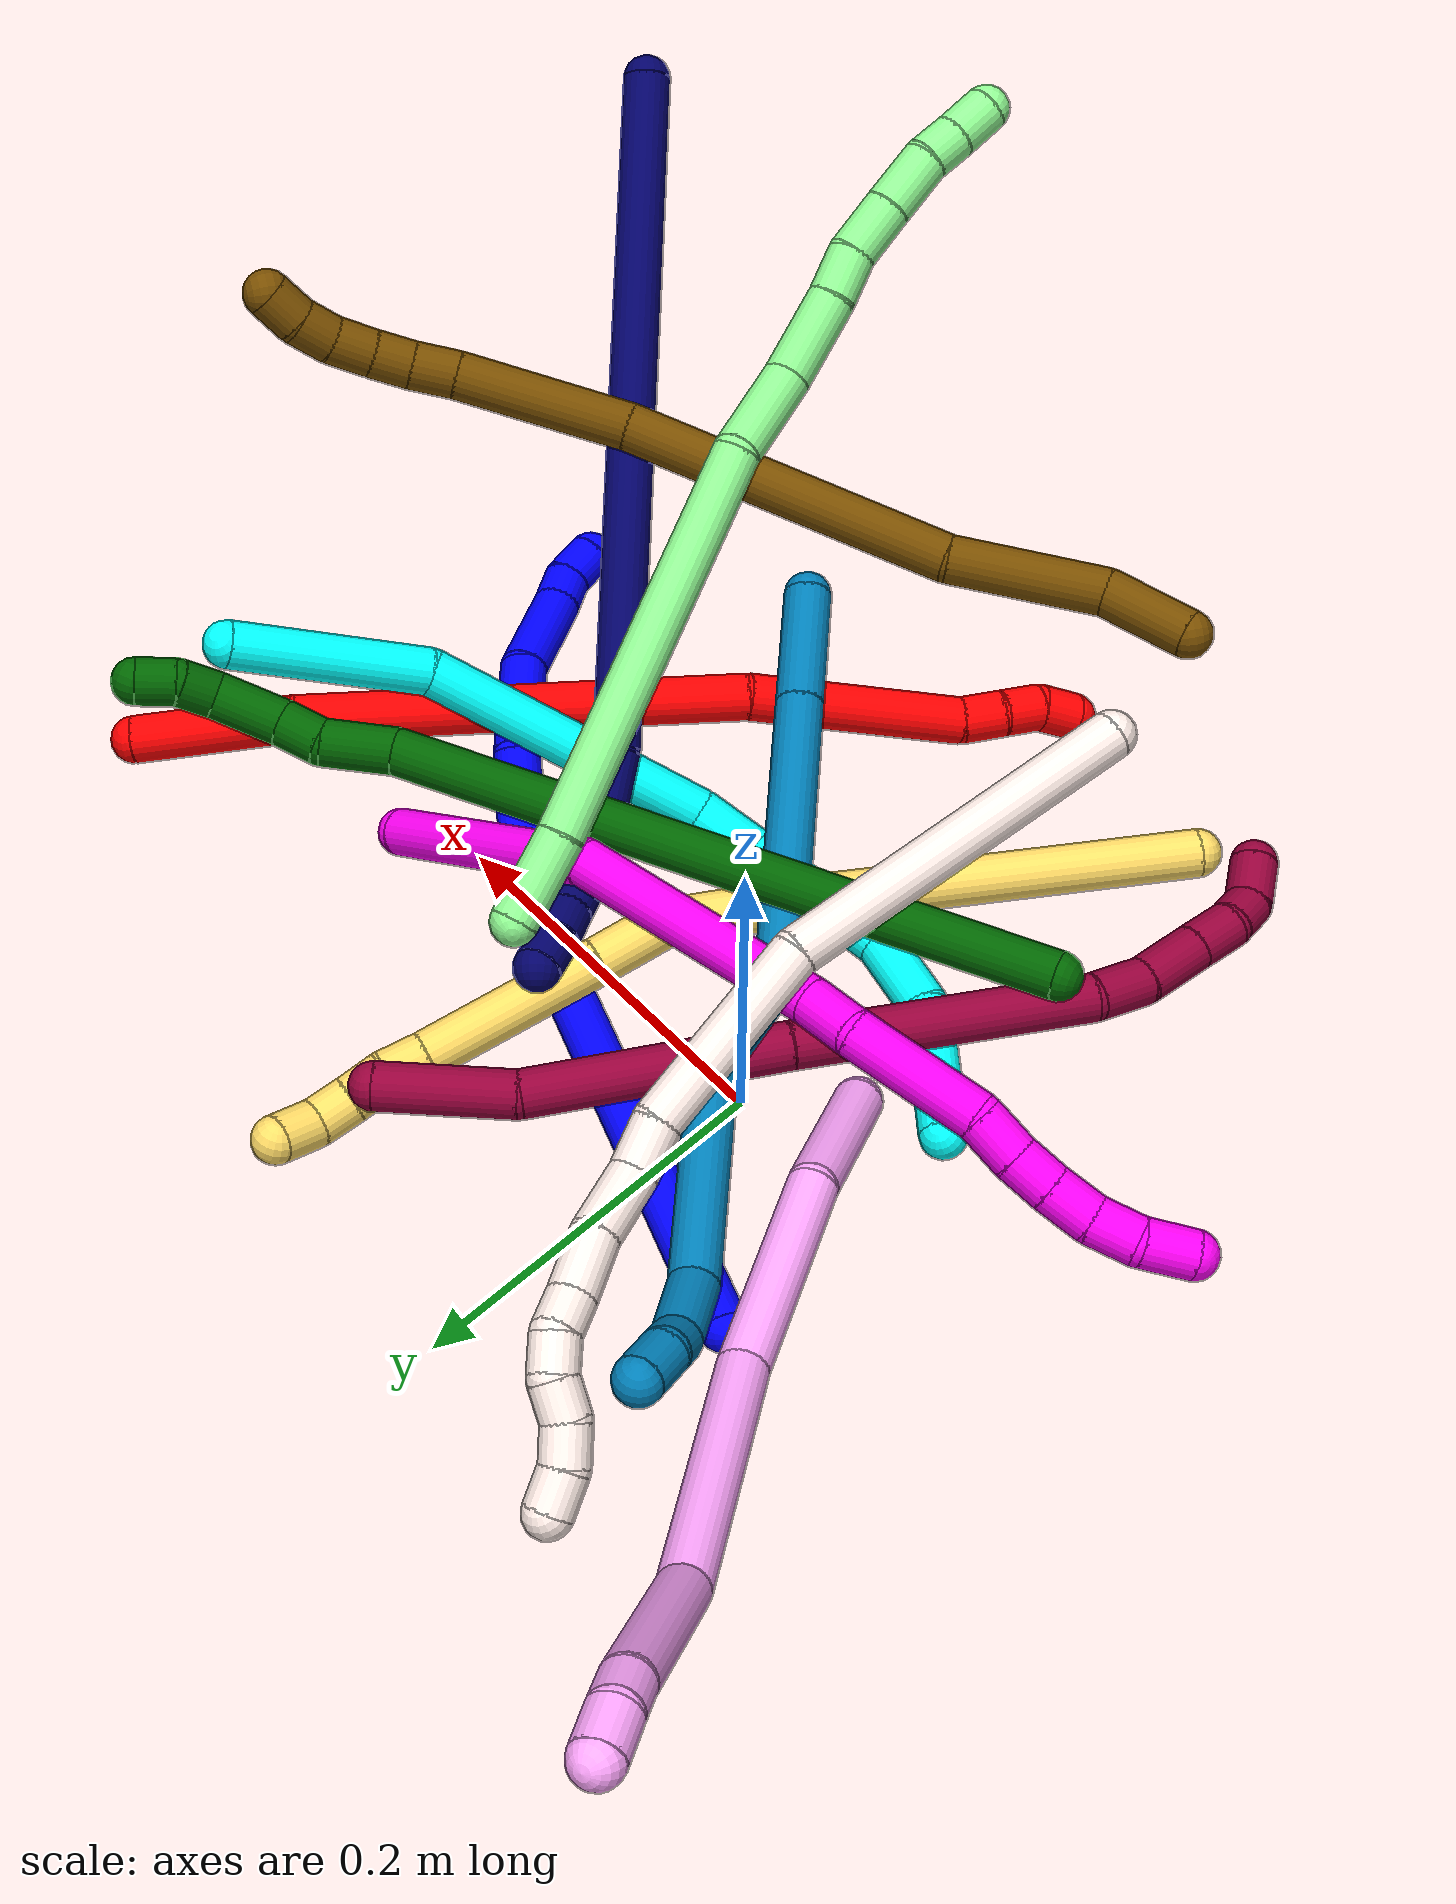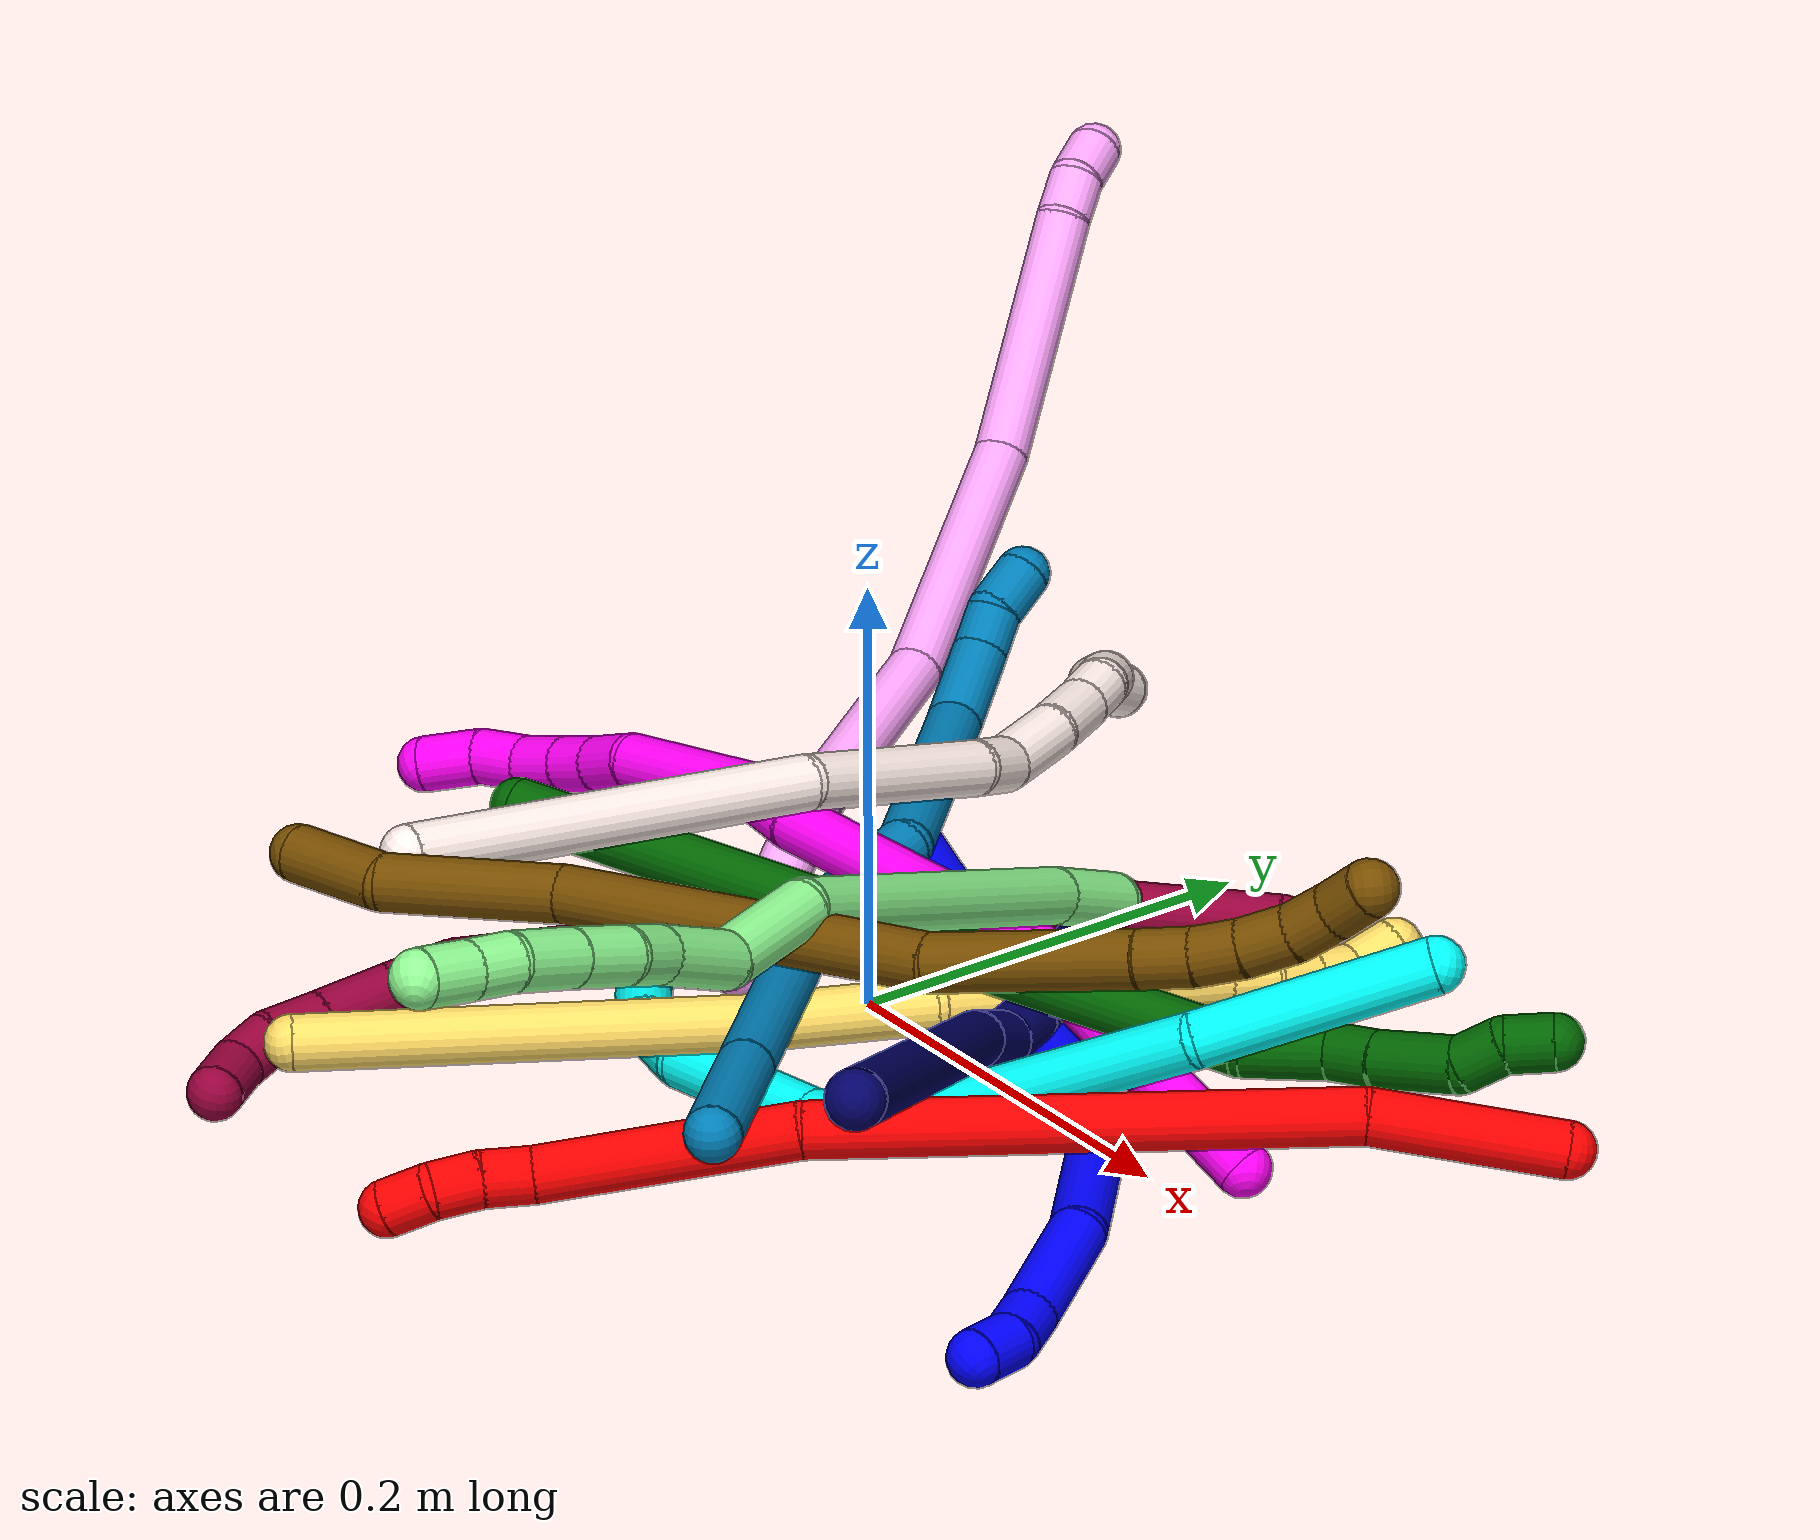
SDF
<sdf version="1.7">
 <world name="default">
  <plugin name="TubeGeneratorPlugin" filename="libtube_generator_plugin.so"/>
  <model name="photoneo_s_sensor">
   <static>1</static>
   <pose>0 0 2 1.57079 1.57079 3.14159</pose>
   <link name="link">
    <inertial><mass>0.1</mass></inertial>
    <sensor name="sensor" type="depth">
     <update_rate>30</update_rate>
     <camera>
      <horizontal_fov>1.22</horizontal_fov>
      <image><width>1920</width><height>1200</height><format>B8G8R8</format></image>
      <clip><near>0.1</near><far>4</far></clip>
      <depth_camera><output>points</output></depth_camera>
     </camera>
     <plugin name="camera_plugin" filename="libgazebo_ros_depth_camera.so">
      <baseline>0.2</baseline>
      <alwaysOn>1</alwaysOn>
      <updateRate>0.0</updateRate>
      <cameraName>camera_ir</cameraName>
      <imageTopicName>/camera/color/image_raw</imageTopicName>
      <cameraInfoTopicName>/camera/color/camera_info</cameraInfoTopicName>
      <depthImageTopicName>/camera/depth/image_raw</depthImageTopicName>
      <depthImageCameraInfoTopicName>/camera/depth/camera_info</depthImageCameraInfoTopicName>
      <pointCloudTopicName>/camera/depth/points</pointCloudTopicName>
      <frameName>fr_optical</frameName>
      <pointCloudCutoff>0.1</pointCloudCutoff>
      <pointCloudCutoffMax>2.0</pointCloudCutoffMax>
      <distortionK1>0</distortionK1>
      <distortionK2>0</distortionK2>
      <distortionK3>0</distortionK3>
      <distortionT1>0</distortionT1>
      <distortionT2>0</distortionT2>
      <CxPrime>0</CxPrime>
      <Cx>0</Cx>
      <Cy>0</Cy>
      <focalLength>0</focalLength>
      <hackBaseline>0</hackBaseline>
     </plugin>
    </sensor>
   </link>
  </model>
  <gravity>0 0 -9.8</gravity>
  <magnetic_field>6e-06 2.3e-05 -4.2e-05</magnetic_field>
  <atmosphere type="adiabatic"/>
  <physics name="default_physics" default="0" type="ode">
   <max_step_size>0.003</max_step_size>
   <real_time_factor>1</real_time_factor>
   <real_time_update_rate>1000</real_time_update_rate>
   <max_contacts>10000</max_contacts>
   <ode>
    <solver>
     <type>quick</type>
     <iters>100</iters>
     <sor>1.3</sor>
     <use_dynamic_moi_rescaling>0</use_dynamic_moi_rescaling>
    </solver>
    <constraints>
     <contact_max_correcting_vel>0</contact_max_correcting_vel>
     <contact_surface_layer>0.001</contact_surface_layer>
     <cfm>0</cfm>
     <erp>0.2</erp>
    </constraints>
   </ode>
  </physics>
  <scene><ambient>0.4 0.4 0.4 1</ambient><background>0.7 0.7 0.7 1</background><shadows>0</shadows></scene>
  <audio><device>default</device></audio>
  <spherical_coordinates>
   <surface_model>EARTH_WGS84</surface_model>
   <latitude_deg>0</latitude_deg>
   <longitude_deg>0</longitude_deg>
   <elevation>0</elevation>
   <heading_deg>0</heading_deg>
  </spherical_coordinates>
  <model name="bin">
   <static>1</static>
   <link name="bottom">
    <collision name="collision-bottom">
     <pose>0 0 -0.01 0 -0 0</pose>
     <geometry><box><size>0.8 0.6 0.02</size></box></geometry>
     <surface>
      <friction><ode><mu>100</mu><mu2>100</mu2></ode></friction>
      <contact><collide_bitmask>65535</collide_bitmask></contact>
     </surface>
    </collision>
   </link>
   <link name="west_wall">
    <collision name="collision-west_wall">
     <pose>-0.41 0 0.1 0 -0 0</pose>
     <geometry><box><size>0.02 0.6 0.2</size></box></geometry>
     <surface>
      <friction><ode><mu>100</mu><mu2>100</mu2></ode></friction>
      <contact><collide_bitmask>65535</collide_bitmask></contact>
     </surface>
    </collision>
   </link>
   <link name="east_wall">
    <collision name="collision-east_wall">
     <pose>0.41 0 0.1 0 -0 0</pose>
     <geometry><box><size>0.02 0.6 0.2</size></box></geometry>
     <surface>
      <friction><ode><mu>100</mu><mu2>100</mu2></ode></friction>
      <contact><collide_bitmask>65535</collide_bitmask></contact>
     </surface>
    </collision>
   </link>
   <link name="south_wall">
    <collision name="collision-south_wall">
     <pose>0 -0.31 0.1 0 -0 0</pose>
     <geometry><box><size>0.8 0.02 0.2</size></box></geometry>
     <surface>
      <friction><ode><mu>100</mu><mu2>100</mu2></ode></friction>
      <contact><collide_bitmask>65535</collide_bitmask></contact>
     </surface>
    </collision>
   </link>
   <link name="north_wall">
    <collision name="collision-north_wall">
     <pose>0 0.31 0.1 0 -0 0</pose>
     <geometry><box><size>0.8 0.02 0.2</size></box></geometry>
     <surface>
      <friction><ode><mu>100</mu><mu2>100</mu2></ode></friction>
      <contact><collide_bitmask>65535</collide_bitmask></contact>
     </surface>
    </collision>
   </link>
  </model>
  <model name="1">
   <static>0</static>
   <link name="1">
    <collision name="collision-cylinder-e_1_1_4">
     <pose>0.055363 -0.040439 0.112895 0.343963 0.432514 0.076283</pose>
     <geometry><cylinder><radius>0.0125</radius><length>0.264164</length></cylinder></geometry>
     <surface>
      <friction><ode><mu>1.16</mu><mu2>1.16</mu2><slip1>0</slip1><slip2>0</slip2></ode></friction>
      <contact><ode><kp>1e+06</kp><kd>1</kd><max_vel>0</max_vel><min_depth>0.001</min_depth></ode></contact>
     </surface>
    </collision>
    <visual name="visual-cylinder-e_1_1_4">
     <pose>0.055363 -0.040439 0.112895 0.343963 0.432514 0.076283</pose>
     <geometry><cylinder><radius>0.0125</radius><length>0.264164</length></cylinder></geometry>
     <material><ambient>0 0 1 1</ambient></material>
    </visual>
    <collision name="collision-cylinder-e_2_4_5">
     <pose>0.139225 -0.095589 0.249295 0.559229 0.799096 0.241315</pose>
     <geometry><cylinder><radius>0.0125</radius><length>0.079526</length></cylinder></geometry>
     <surface>
      <friction><ode><mu>1.16</mu><mu2>1.16</mu2><slip1>0</slip1><slip2>0</slip2></ode></friction>
      <contact><ode><kp>1e+06</kp><kd>1</kd><max_vel>0</max_vel><min_depth>0.001</min_depth></ode></contact>
     </surface>
    </collision>
    <visual name="visual-cylinder-e_2_4_5">
     <pose>0.139225 -0.095589 0.249295 0.559229 0.799096 0.241315</pose>
     <geometry><cylinder><radius>0.0125</radius><length>0.079526</length></cylinder></geometry>
     <material><ambient>0 0 1 1</ambient></material>
    </visual>
    <collision name="collision-cylinder-e_3_5_6">
     <pose>0.188977 -0.112084 0.293387 0.086408 0.799438 0.036523</pose>
     <geometry><cylinder><radius>0.0125</radius><length>0.059287</length></cylinder></geometry>
     <surface>
      <friction><ode><mu>1.16</mu><mu2>1.16</mu2><slip1>0</slip1><slip2>0</slip2></ode></friction>
      <contact><ode><kp>1e+06</kp><kd>1</kd><max_vel>0</max_vel><min_depth>0.001</min_depth></ode></contact>
     </surface>
    </collision>
    <visual name="visual-cylinder-e_3_5_6">
     <pose>0.188977 -0.112084 0.293387 0.086408 0.799438 0.036523</pose>
     <geometry><cylinder><radius>0.0125</radius><length>0.059287</length></cylinder></geometry>
     <material><ambient>0 0 1 1</ambient></material>
    </visual>
    <collision name="collision-cylinder-e_4_6_7">
     <pose>0.232212 -0.108039 0.329814 -0.352584 0.916012 -0.175186</pose>
     <geometry><cylinder><radius>0.0125</radius><length>0.055425</length></cylinder></geometry>
     <surface>
      <friction><ode><mu>1.16</mu><mu2>1.16</mu2><slip1>0</slip1><slip2>0</slip2></ode></friction>
      <contact><ode><kp>1e+06</kp><kd>1</kd><max_vel>0</max_vel><min_depth>0.001</min_depth></ode></contact>
     </surface>
    </collision>
    <visual name="visual-cylinder-e_4_6_7">
     <pose>0.232212 -0.108039 0.329814 -0.352584 0.916012 -0.175186</pose>
     <geometry><cylinder><radius>0.0125</radius><length>0.055425</length></cylinder></geometry>
     <material><ambient>0 0 1 1</ambient></material>
    </visual>
    <collision name="collision-cylinder-e_5_7_8">
     <pose>0.262682 -0.101406 0.3511 -0.14687 0.995387 -0.079897</pose>
     <geometry><cylinder><radius>0.0125</radius><length>0.020239</length></cylinder></geometry>
     <surface>
      <friction><ode><mu>1.16</mu><mu2>1.16</mu2><slip1>0</slip1><slip2>0</slip2></ode></friction>
      <contact><ode><kp>1e+06</kp><kd>1</kd><max_vel>0</max_vel><min_depth>0.001</min_depth></ode></contact>
     </surface>
    </collision>
    <visual name="visual-cylinder-e_5_7_8">
     <pose>0.262682 -0.101406 0.3511 -0.14687 0.995387 -0.079897</pose>
     <geometry><cylinder><radius>0.0125</radius><length>0.020239</length></cylinder></geometry>
     <material><ambient>0 0 1 1</ambient></material>
    </visual>
    <collision name="collision-cylinder-e_6_8_2">
     <pose>0.28145 -0.098634 0.358683 -0.743897 1.29552 -0.574065</pose>
     <geometry><cylinder><radius>0.0125</radius><length>0.021359</length></cylinder></geometry>
     <surface>
      <friction><ode><mu>1.16</mu><mu2>1.16</mu2><slip1>0</slip1><slip2>0</slip2></ode></friction>
      <contact><ode><kp>1e+06</kp><kd>1</kd><max_vel>0</max_vel><min_depth>0.001</min_depth></ode></contact>
     </surface>
    </collision>
    <visual name="visual-cylinder-e_6_8_2">
     <pose>0.28145 -0.098634 0.358683 -0.743897 1.29552 -0.574065</pose>
     <geometry><cylinder><radius>0.0125</radius><length>0.021359</length></cylinder></geometry>
     <material><ambient>0 0 1 1</ambient></material>
    </visual>
    <collision name="collision-sphere-2">
     <pose>0.291727 -0.096668 0.360819 0 -0 0</pose>
     <geometry><sphere><radius>0.0125</radius></sphere></geometry>
     <surface>
      <friction><ode><mu>1.16</mu><mu2>1.16</mu2><slip1>0</slip1><slip2>0</slip2></ode></friction>
      <contact><ode><kp>1e+06</kp><kd>1</kd><max_vel>0</max_vel><min_depth>0.001</min_depth></ode></contact>
     </surface>
    </collision>
    <visual name="visual-sphere-2">
     <pose>0.291727 -0.096668 0.360819 0 -0 0</pose>
     <geometry><sphere><radius>0.0125</radius></sphere></geometry>
     <material><ambient>0 0 1 1</ambient></material>
    </visual>
    <collision name="collision-sphere-4">
     <pose>0.110726 -0.080878 0.22579 0 -0 0</pose>
     <geometry><sphere><radius>0.0125</radius></sphere></geometry>
     <surface>
      <friction><ode><mu>1.16</mu><mu2>1.16</mu2><slip1>0</slip1><slip2>0</slip2></ode></friction>
      <contact><ode><kp>1e+06</kp><kd>1</kd><max_vel>0</max_vel><min_depth>0.001</min_depth></ode></contact>
     </surface>
    </collision>
    <visual name="visual-sphere-4">
     <pose>0.110726 -0.080878 0.22579 0 -0 0</pose>
     <geometry><sphere><radius>0.0125</radius></sphere></geometry>
     <material><ambient>0 0 1 1</ambient></material>
    </visual>
    <collision name="collision-sphere-1">
     <geometry><sphere><radius>0.0125</radius></sphere></geometry>
     <surface>
      <friction><ode><mu>1.16</mu><mu2>1.16</mu2><slip1>0</slip1><slip2>0</slip2></ode></friction>
      <contact><ode><kp>1e+06</kp><kd>1</kd><max_vel>0</max_vel><min_depth>0.001</min_depth></ode></contact>
     </surface>
    </collision>
    <visual name="visual-sphere-1">
     <geometry><sphere><radius>0.0125</radius></sphere></geometry>
     <material><ambient>0 0 1 1</ambient></material>
    </visual>
    <collision name="collision-sphere-8">
     <pose>0.271172 -0.1006 0.356547 0 -0 0</pose>
     <geometry><sphere><radius>0.0125</radius></sphere></geometry>
     <surface>
      <friction><ode><mu>1.16</mu><mu2>1.16</mu2><slip1>0</slip1><slip2>0</slip2></ode></friction>
      <contact><ode><kp>1e+06</kp><kd>1</kd><max_vel>0</max_vel><min_depth>0.001</min_depth></ode></contact>
     </surface>
    </collision>
    <visual name="visual-sphere-8">
     <pose>0.271172 -0.1006 0.356547 0 -0 0</pose>
     <geometry><sphere><radius>0.0125</radius></sphere></geometry>
     <material><ambient>0 0 1 1</ambient></material>
    </visual>
    <collision name="collision-sphere-5">
     <pose>0.167724 -0.110301 0.2728 0 -0 0</pose>
     <geometry><sphere><radius>0.0125</radius></sphere></geometry>
     <surface>
      <friction><ode><mu>1.16</mu><mu2>1.16</mu2><slip1>0</slip1><slip2>0</slip2></ode></friction>
      <contact><ode><kp>1e+06</kp><kd>1</kd><max_vel>0</max_vel><min_depth>0.001</min_depth></ode></contact>
     </surface>
    </collision>
    <visual name="visual-sphere-5">
     <pose>0.167724 -0.110301 0.2728 0 -0 0</pose>
     <geometry><sphere><radius>0.0125</radius></sphere></geometry>
     <material><ambient>0 0 1 1</ambient></material>
    </visual>
    <collision name="collision-sphere-6">
     <pose>0.21023 -0.113867 0.313975 0 -0 0</pose>
     <geometry><sphere><radius>0.0125</radius></sphere></geometry>
     <surface>
      <friction><ode><mu>1.16</mu><mu2>1.16</mu2><slip1>0</slip1><slip2>0</slip2></ode></friction>
      <contact><ode><kp>1e+06</kp><kd>1</kd><max_vel>0</max_vel><min_depth>0.001</min_depth></ode></contact>
     </surface>
    </collision>
    <visual name="visual-sphere-6">
     <pose>0.21023 -0.113867 0.313975 0 -0 0</pose>
     <geometry><sphere><radius>0.0125</radius></sphere></geometry>
     <material><ambient>0 0 1 1</ambient></material>
    </visual>
    <collision name="collision-sphere-7">
     <pose>0.254193 -0.102212 0.345652 0 -0 0</pose>
     <geometry><sphere><radius>0.0125</radius></sphere></geometry>
     <surface>
      <friction><ode><mu>1.16</mu><mu2>1.16</mu2><slip1>0</slip1><slip2>0</slip2></ode></friction>
      <contact><ode><kp>1e+06</kp><kd>1</kd><max_vel>0</max_vel><min_depth>0.001</min_depth></ode></contact>
     </surface>
    </collision>
    <visual name="visual-sphere-7">
     <pose>0.254193 -0.102212 0.345652 0 -0 0</pose>
     <geometry><sphere><radius>0.0125</radius></sphere></geometry>
     <material><ambient>0 0 1 1</ambient></material>
    </visual>
    <inertial>
     <pose>0.122198 -0.070153 0.200178 0 -0 0</pose>
     <mass>0.5</mass>
     <inertia>
      <ixx>0.001591</ixx>
      <ixy>0</ixy>
      <ixz>0</ixz>
      <iyy>0.001653</iyy>
      <iyz>0</iyz>
      <izz>-0.000195</izz>
     </inertia>
    </inertial>
   </link>
   <pose>-0.08909 0.094238 0.011497 -2.04765 -0.279282 -1.46933</pose>
  </model>
  <model name="2">
   <static>0</static>
   <link name="2">
    <collision name="collision-cylinder-e_1_1_4">
     <pose>-0.02513 -0.033486 -0.007141 1.78091 -0.633139 -0.769302</pose>
     <geometry><cylinder><radius>0.0125</radius><length>0.084943</length></cylinder></geometry>
     <surface>
      <friction><ode><mu>1.16</mu><mu2>1.16</mu2><slip1>0</slip1><slip2>0</slip2></ode></friction>
      <contact><ode><kp>1e+06</kp><kd>1</kd><max_vel>0</max_vel><min_depth>0.001</min_depth></ode></contact>
     </surface>
    </collision>
    <visual name="visual-cylinder-e_1_1_4">
     <pose>-0.02513 -0.033486 -0.007141 1.78091 -0.633139 -0.769302</pose>
     <geometry><cylinder><radius>0.0125</radius><length>0.084943</length></cylinder></geometry>
     <material><ambient>1 0 0 1</ambient></material>
    </visual>
    <collision name="collision-cylinder-e_2_4_5">
     <pose>-0.11482 -0.155731 -0.056444 2.01426 -0.5813 -0.884022</pose>
     <geometry><cylinder><radius>0.0125</radius><length>0.235148</length></cylinder></geometry>
     <surface>
      <friction><ode><mu>1.16</mu><mu2>1.16</mu2><slip1>0</slip1><slip2>0</slip2></ode></friction>
      <contact><ode><kp>1e+06</kp><kd>1</kd><max_vel>0</max_vel><min_depth>0.001</min_depth></ode></contact>
     </surface>
    </collision>
    <visual name="visual-cylinder-e_2_4_5">
     <pose>-0.11482 -0.155731 -0.056444 2.01426 -0.5813 -0.884022</pose>
     <geometry><cylinder><radius>0.0125</radius><length>0.235148</length></cylinder></geometry>
     <material><ambient>1 0 0 1</ambient></material>
    </visual>
    <collision name="collision-cylinder-e_3_5_6">
     <pose>-0.212211 -0.281455 -0.128243 2.2466 -0.605936 -1.15454</pose>
     <geometry><cylinder><radius>0.0125</radius><length>0.115284</length></cylinder></geometry>
     <surface>
      <friction><ode><mu>1.16</mu><mu2>1.16</mu2><slip1>0</slip1><slip2>0</slip2></ode></friction>
      <contact><ode><kp>1e+06</kp><kd>1</kd><max_vel>0</max_vel><min_depth>0.001</min_depth></ode></contact>
     </surface>
    </collision>
    <visual name="visual-cylinder-e_3_5_6">
     <pose>-0.212211 -0.281455 -0.128243 2.2466 -0.605936 -1.15454</pose>
     <geometry><cylinder><radius>0.0125</radius><length>0.115284</length></cylinder></geometry>
     <material><ambient>1 0 0 1</ambient></material>
    </visual>
    <collision name="collision-cylinder-e_4_6_7">
     <pose>-0.249905 -0.327765 -0.162047 1.99025 -0.443938 -0.669333</pose>
     <geometry><cylinder><radius>0.0125</radius><length>0.022658</length></cylinder></geometry>
     <surface>
      <friction><ode><mu>1.16</mu><mu2>1.16</mu2><slip1>0</slip1><slip2>0</slip2></ode></friction>
      <contact><ode><kp>1e+06</kp><kd>1</kd><max_vel>0</max_vel><min_depth>0.001</min_depth></ode></contact>
     </surface>
    </collision>
    <visual name="visual-cylinder-e_4_6_7">
     <pose>-0.249905 -0.327765 -0.162047 1.99025 -0.443938 -0.669333</pose>
     <geometry><cylinder><radius>0.0125</radius><length>0.022658</length></cylinder></geometry>
     <material><ambient>1 0 0 1</ambient></material>
    </visual>
    <collision name="collision-cylinder-e_5_7_8">
     <pose>-0.258293 -0.345686 -0.171462 2.11992 -0.336842 -0.589111</pose>
     <geometry><cylinder><radius>0.0125</radius><length>0.021309</length></cylinder></geometry>
     <surface>
      <friction><ode><mu>1.16</mu><mu2>1.16</mu2><slip1>0</slip1><slip2>0</slip2></ode></friction>
      <contact><ode><kp>1e+06</kp><kd>1</kd><max_vel>0</max_vel><min_depth>0.001</min_depth></ode></contact>
     </surface>
    </collision>
    <visual name="visual-cylinder-e_5_7_8">
     <pose>-0.258293 -0.345686 -0.171462 2.11992 -0.336842 -0.589111</pose>
     <geometry><cylinder><radius>0.0125</radius><length>0.021309</length></cylinder></geometry>
     <material><ambient>1 0 0 1</ambient></material>
    </visual>
    <collision name="collision-cylinder-e_6_8_2">
     <pose>-0.267137 -0.359668 -0.183721 2.48487 -0.541406 -1.36712</pose>
     <geometry><cylinder><radius>0.0125</radius><length>0.020657</length></cylinder></geometry>
     <surface>
      <friction><ode><mu>1.16</mu><mu2>1.16</mu2><slip1>0</slip1><slip2>0</slip2></ode></friction>
      <contact><ode><kp>1e+06</kp><kd>1</kd><max_vel>0</max_vel><min_depth>0.001</min_depth></ode></contact>
     </surface>
    </collision>
    <visual name="visual-cylinder-e_6_8_2">
     <pose>-0.267137 -0.359668 -0.183721 2.48487 -0.541406 -1.36712</pose>
     <geometry><cylinder><radius>0.0125</radius><length>0.020657</length></cylinder></geometry>
     <material><ambient>1 0 0 1</ambient></material>
    </visual>
    <collision name="collision-sphere-2">
     <pose>-0.272459 -0.365072 -0.190731 0 -0 0</pose>
     <geometry><sphere><radius>0.0125</radius></sphere></geometry>
     <surface>
      <friction><ode><mu>1.16</mu><mu2>1.16</mu2><slip1>0</slip1><slip2>0</slip2></ode></friction>
      <contact><ode><kp>1e+06</kp><kd>1</kd><max_vel>0</max_vel><min_depth>0.001</min_depth></ode></contact>
     </surface>
    </collision>
    <visual name="visual-sphere-2">
     <pose>-0.272459 -0.365072 -0.190731 0 -0 0</pose>
     <geometry><sphere><radius>0.0125</radius></sphere></geometry>
     <material><ambient>1 0 0 1</ambient></material>
    </visual>
    <collision name="collision-sphere-4">
     <pose>-0.050259 -0.066973 -0.014283 0 -0 0</pose>
     <geometry><sphere><radius>0.0125</radius></sphere></geometry>
     <surface>
      <friction><ode><mu>1.16</mu><mu2>1.16</mu2><slip1>0</slip1><slip2>0</slip2></ode></friction>
      <contact><ode><kp>1e+06</kp><kd>1</kd><max_vel>0</max_vel><min_depth>0.001</min_depth></ode></contact>
     </surface>
    </collision>
    <visual name="visual-sphere-4">
     <pose>-0.050259 -0.066973 -0.014283 0 -0 0</pose>
     <geometry><sphere><radius>0.0125</radius></sphere></geometry>
     <material><ambient>1 0 0 1</ambient></material>
    </visual>
    <collision name="collision-sphere-1">
     <geometry><sphere><radius>0.0125</radius></sphere></geometry>
     <surface>
      <friction><ode><mu>1.16</mu><mu2>1.16</mu2><slip1>0</slip1><slip2>0</slip2></ode></friction>
      <contact><ode><kp>1e+06</kp><kd>1</kd><max_vel>0</max_vel><min_depth>0.001</min_depth></ode></contact>
     </surface>
    </collision>
    <visual name="visual-sphere-1">
     <geometry><sphere><radius>0.0125</radius></sphere></geometry>
     <material><ambient>1 0 0 1</ambient></material>
    </visual>
    <collision name="collision-sphere-8">
     <pose>-0.261814 -0.354264 -0.176711 0 -0 0</pose>
     <geometry><sphere><radius>0.0125</radius></sphere></geometry>
     <surface>
      <friction><ode><mu>1.16</mu><mu2>1.16</mu2><slip1>0</slip1><slip2>0</slip2></ode></friction>
      <contact><ode><kp>1e+06</kp><kd>1</kd><max_vel>0</max_vel><min_depth>0.001</min_depth></ode></contact>
     </surface>
    </collision>
    <visual name="visual-sphere-8">
     <pose>-0.261814 -0.354264 -0.176711 0 -0 0</pose>
     <geometry><sphere><radius>0.0125</radius></sphere></geometry>
     <material><ambient>1 0 0 1</ambient></material>
    </visual>
    <collision name="collision-sphere-5">
     <pose>-0.179381 -0.244488 -0.098606 0 -0 0</pose>
     <geometry><sphere><radius>0.0125</radius></sphere></geometry>
     <surface>
      <friction><ode><mu>1.16</mu><mu2>1.16</mu2><slip1>0</slip1><slip2>0</slip2></ode></friction>
      <contact><ode><kp>1e+06</kp><kd>1</kd><max_vel>0</max_vel><min_depth>0.001</min_depth></ode></contact>
     </surface>
    </collision>
    <visual name="visual-sphere-5">
     <pose>-0.179381 -0.244488 -0.098606 0 -0 0</pose>
     <geometry><sphere><radius>0.0125</radius></sphere></geometry>
     <material><ambient>1 0 0 1</ambient></material>
    </visual>
    <collision name="collision-sphere-6">
     <pose>-0.24504 -0.318421 -0.15788 0 -0 0</pose>
     <geometry><sphere><radius>0.0125</radius></sphere></geometry>
     <surface>
      <friction><ode><mu>1.16</mu><mu2>1.16</mu2><slip1>0</slip1><slip2>0</slip2></ode></friction>
      <contact><ode><kp>1e+06</kp><kd>1</kd><max_vel>0</max_vel><min_depth>0.001</min_depth></ode></contact>
     </surface>
    </collision>
    <visual name="visual-sphere-6">
     <pose>-0.24504 -0.318421 -0.15788 0 -0 0</pose>
     <geometry><sphere><radius>0.0125</radius></sphere></geometry>
     <material><ambient>1 0 0 1</ambient></material>
    </visual>
    <collision name="collision-sphere-7">
     <pose>-0.254771 -0.337109 -0.166214 0 -0 0</pose>
     <geometry><sphere><radius>0.0125</radius></sphere></geometry>
     <surface>
      <friction><ode><mu>1.16</mu><mu2>1.16</mu2><slip1>0</slip1><slip2>0</slip2></ode></friction>
      <contact><ode><kp>1e+06</kp><kd>1</kd><max_vel>0</max_vel><min_depth>0.001</min_depth></ode></contact>
     </surface>
    </collision>
    <visual name="visual-sphere-7">
     <pose>-0.254771 -0.337109 -0.166214 0 -0 0</pose>
     <geometry><sphere><radius>0.0125</radius></sphere></geometry>
     <material><ambient>1 0 0 1</ambient></material>
    </visual>
    <inertial>
     <pose>-0.140567 -0.188268 -0.079569 0 -0 0</pose>
     <mass>0.5</mass>
     <inertia>
      <ixx>-0.000203</ixx>
      <ixy>0</ixy>
      <ixz>0</ixz>
      <iyy>-0.000712</iyy>
      <iyz>0</iyz>
      <izz>0.001651</izz>
     </inertia>
    </inertial>
   </link>
   <pose>0.352297 0.102263 0.045996 -0.356861 0.063043 -0.066797</pose>
  </model>
  <model name="3">
   <static>0</static>
   <link name="3">
    <collision name="collision-cylinder-e_1_1_4">
     <pose>-0.027475 -0.030595 -0.032687 2.38923 -0.550419 -1.24129</pose>
     <geometry><cylinder><radius>0.0125</radius><length>0.10506</length></cylinder></geometry>
     <surface>
      <friction><ode><mu>1.16</mu><mu2>1.16</mu2><slip1>0</slip1><slip2>0</slip2></ode></friction>
      <contact><ode><kp>1e+06</kp><kd>1</kd><max_vel>0</max_vel><min_depth>0.001</min_depth></ode></contact>
     </surface>
    </collision>
    <visual name="visual-cylinder-e_1_1_4">
     <pose>-0.027475 -0.030595 -0.032687 2.38923 -0.550419 -1.24129</pose>
     <geometry><cylinder><radius>0.0125</radius><length>0.10506</length></cylinder></geometry>
     <material><ambient>0.003922 1 0.996078 1</ambient></material>
    </visual>
    <collision name="collision-cylinder-e_2_4_5">
     <pose>-0.112374 -0.083808 -0.115212 2.71558 -0.8094 -2.20641</pose>
     <geometry><cylinder><radius>0.0125</radius><length>0.158655</length></cylinder></geometry>
     <surface>
      <friction><ode><mu>1.16</mu><mu2>1.16</mu2><slip1>0</slip1><slip2>0</slip2></ode></friction>
      <contact><ode><kp>1e+06</kp><kd>1</kd><max_vel>0</max_vel><min_depth>0.001</min_depth></ode></contact>
     </surface>
    </collision>
    <visual name="visual-cylinder-e_2_4_5">
     <pose>-0.112374 -0.083808 -0.115212 2.71558 -0.8094 -2.20641</pose>
     <geometry><cylinder><radius>0.0125</radius><length>0.158655</length></cylinder></geometry>
     <material><ambient>0.003922 1 0.996078 1</ambient></material>
    </visual>
    <collision name="collision-cylinder-e_3_5_6">
     <pose>-0.187004 -0.108721 -0.170647 2.75226 -1.23278 -2.59874</pose>
     <geometry><cylinder><radius>0.0125</radius><length>0.036478</length></cylinder></geometry>
     <surface>
      <friction><ode><mu>1.16</mu><mu2>1.16</mu2><slip1>0</slip1><slip2>0</slip2></ode></friction>
      <contact><ode><kp>1e+06</kp><kd>1</kd><max_vel>0</max_vel><min_depth>0.001</min_depth></ode></contact>
     </surface>
    </collision>
    <visual name="visual-cylinder-e_3_5_6">
     <pose>-0.187004 -0.108721 -0.170647 2.75226 -1.23278 -2.59874</pose>
     <geometry><cylinder><radius>0.0125</radius><length>0.036478</length></cylinder></geometry>
     <material><ambient>0.003922 1 0.996078 1</ambient></material>
    </visual>
    <collision name="collision-cylinder-e_4_6_7">
     <pose>-0.244636 -0.115304 -0.182464 2.53818 -1.38602 -2.42447</pose>
     <geometry><cylinder><radius>0.0125</radius><length>0.082252</length></cylinder></geometry>
     <surface>
      <friction><ode><mu>1.16</mu><mu2>1.16</mu2><slip1>0</slip1><slip2>0</slip2></ode></friction>
      <contact><ode><kp>1e+06</kp><kd>1</kd><max_vel>0</max_vel><min_depth>0.001</min_depth></ode></contact>
     </surface>
    </collision>
    <visual name="visual-cylinder-e_4_6_7">
     <pose>-0.244636 -0.115304 -0.182464 2.53818 -1.38602 -2.42447</pose>
     <geometry><cylinder><radius>0.0125</radius><length>0.082252</length></cylinder></geometry>
     <material><ambient>0.003922 1 0.996078 1</ambient></material>
    </visual>
    <collision name="collision-cylinder-e_5_7_8">
     <pose>-0.305856 -0.115331 -0.18878 -1.59302 -1.36865 1.39047</pose>
     <geometry><cylinder><radius>0.0125</radius><length>0.042451</length></cylinder></geometry>
     <surface>
      <friction><ode><mu>1.16</mu><mu2>1.16</mu2><slip1>0</slip1><slip2>0</slip2></ode></friction>
      <contact><ode><kp>1e+06</kp><kd>1</kd><max_vel>0</max_vel><min_depth>0.001</min_depth></ode></contact>
     </surface>
    </collision>
    <visual name="visual-cylinder-e_5_7_8">
     <pose>-0.305856 -0.115331 -0.18878 -1.59302 -1.36865 1.39047</pose>
     <geometry><cylinder><radius>0.0125</radius><length>0.042451</length></cylinder></geometry>
     <material><ambient>0.003922 1 0.996078 1</ambient></material>
    </visual>
    <collision name="collision-cylinder-e_6_8_9">
     <pose>-0.336806 -0.104777 -0.186819 -1.25513 -0.993116 0.748995</pose>
     <geometry><cylinder><radius>0.0125</radius><length>0.024249</length></cylinder></geometry>
     <surface>
      <friction><ode><mu>1.16</mu><mu2>1.16</mu2><slip1>0</slip1><slip2>0</slip2></ode></friction>
      <contact><ode><kp>1e+06</kp><kd>1</kd><max_vel>0</max_vel><min_depth>0.001</min_depth></ode></contact>
     </surface>
    </collision>
    <visual name="visual-cylinder-e_6_8_9">
     <pose>-0.336806 -0.104777 -0.186819 -1.25513 -0.993116 0.748995</pose>
     <geometry><cylinder><radius>0.0125</radius><length>0.024249</length></cylinder></geometry>
     <material><ambient>0.003922 1 0.996078 1</ambient></material>
    </visual>
    <collision name="collision-cylinder-e_7_9_10">
     <pose>-0.358614 -0.090134 -0.182125 -1.26474 -0.926258 0.701541</pose>
     <geometry><cylinder><radius>0.0125</radius><length>0.029149</length></cylinder></geometry>
     <surface>
      <friction><ode><mu>1.16</mu><mu2>1.16</mu2><slip1>0</slip1><slip2>0</slip2></ode></friction>
      <contact><ode><kp>1e+06</kp><kd>1</kd><max_vel>0</max_vel><min_depth>0.001</min_depth></ode></contact>
     </surface>
    </collision>
    <visual name="visual-cylinder-e_7_9_10">
     <pose>-0.358614 -0.090134 -0.182125 -1.26474 -0.926258 0.701541</pose>
     <geometry><cylinder><radius>0.0125</radius><length>0.029149</length></cylinder></geometry>
     <material><ambient>0.003922 1 0.996078 1</ambient></material>
    </visual>
    <collision name="collision-cylinder-e_8_10_2">
     <pose>-0.378941 -0.075562 -0.177538 -1.26725 -0.926399 0.703351</pose>
     <geometry><cylinder><radius>0.0125</radius><length>0.021706</length></cylinder></geometry>
     <surface>
      <friction><ode><mu>1.16</mu><mu2>1.16</mu2><slip1>0</slip1><slip2>0</slip2></ode></friction>
      <contact><ode><kp>1e+06</kp><kd>1</kd><max_vel>0</max_vel><min_depth>0.001</min_depth></ode></contact>
     </surface>
    </collision>
    <visual name="visual-cylinder-e_8_10_2">
     <pose>-0.378941 -0.075562 -0.177538 -1.26725 -0.926399 0.703351</pose>
     <geometry><cylinder><radius>0.0125</radius><length>0.021706</length></cylinder></geometry>
     <material><ambient>0.003922 1 0.996078 1</ambient></material>
    </visual>
    <collision name="collision-sphere-2">
     <pose>-0.387618 -0.06934 -0.175589 0 -0 0</pose>
     <geometry><sphere><radius>0.0125</radius></sphere></geometry>
     <surface>
      <friction><ode><mu>1.16</mu><mu2>1.16</mu2><slip1>0</slip1><slip2>0</slip2></ode></friction>
      <contact><ode><kp>1e+06</kp><kd>1</kd><max_vel>0</max_vel><min_depth>0.001</min_depth></ode></contact>
     </surface>
    </collision>
    <visual name="visual-sphere-2">
     <pose>-0.387618 -0.06934 -0.175589 0 -0 0</pose>
     <geometry><sphere><radius>0.0125</radius></sphere></geometry>
     <material><ambient>0.003922 1 0.996078 1</ambient></material>
    </visual>
    <collision name="collision-sphere-10">
     <pose>-0.370264 -0.081784 -0.179487 0 -0 0</pose>
     <geometry><sphere><radius>0.0125</radius></sphere></geometry>
     <surface>
      <friction><ode><mu>1.16</mu><mu2>1.16</mu2><slip1>0</slip1><slip2>0</slip2></ode></friction>
      <contact><ode><kp>1e+06</kp><kd>1</kd><max_vel>0</max_vel><min_depth>0.001</min_depth></ode></contact>
     </surface>
    </collision>
    <visual name="visual-sphere-10">
     <pose>-0.370264 -0.081784 -0.179487 0 -0 0</pose>
     <geometry><sphere><radius>0.0125</radius></sphere></geometry>
     <material><ambient>0.003922 1 0.996078 1</ambient></material>
    </visual>
    <collision name="collision-sphere-9">
     <pose>-0.346963 -0.098483 -0.184764 0 -0 0</pose>
     <geometry><sphere><radius>0.0125</radius></sphere></geometry>
     <surface>
      <friction><ode><mu>1.16</mu><mu2>1.16</mu2><slip1>0</slip1><slip2>0</slip2></ode></friction>
      <contact><ode><kp>1e+06</kp><kd>1</kd><max_vel>0</max_vel><min_depth>0.001</min_depth></ode></contact>
     </surface>
    </collision>
    <visual name="visual-sphere-9">
     <pose>-0.346963 -0.098483 -0.184764 0 -0 0</pose>
     <geometry><sphere><radius>0.0125</radius></sphere></geometry>
     <material><ambient>0.003922 1 0.996078 1</ambient></material>
    </visual>
    <collision name="collision-sphere-4">
     <pose>-0.054951 -0.061191 -0.065373 0 -0 0</pose>
     <geometry><sphere><radius>0.0125</radius></sphere></geometry>
     <surface>
      <friction><ode><mu>1.16</mu><mu2>1.16</mu2><slip1>0</slip1><slip2>0</slip2></ode></friction>
      <contact><ode><kp>1e+06</kp><kd>1</kd><max_vel>0</max_vel><min_depth>0.001</min_depth></ode></contact>
     </surface>
    </collision>
    <visual name="visual-sphere-4">
     <pose>-0.054951 -0.061191 -0.065373 0 -0 0</pose>
     <geometry><sphere><radius>0.0125</radius></sphere></geometry>
     <material><ambient>0.003922 1 0.996078 1</ambient></material>
    </visual>
    <collision name="collision-sphere-1">
     <geometry><sphere><radius>0.0125</radius></sphere></geometry>
     <surface>
      <friction><ode><mu>1.16</mu><mu2>1.16</mu2><slip1>0</slip1><slip2>0</slip2></ode></friction>
      <contact><ode><kp>1e+06</kp><kd>1</kd><max_vel>0</max_vel><min_depth>0.001</min_depth></ode></contact>
     </surface>
    </collision>
    <visual name="visual-sphere-1">
     <geometry><sphere><radius>0.0125</radius></sphere></geometry>
     <material><ambient>0.003922 1 0.996078 1</ambient></material>
    </visual>
    <collision name="collision-sphere-8">
     <pose>-0.326649 -0.111071 -0.188875 0 -0 0</pose>
     <geometry><sphere><radius>0.0125</radius></sphere></geometry>
     <surface>
      <friction><ode><mu>1.16</mu><mu2>1.16</mu2><slip1>0</slip1><slip2>0</slip2></ode></friction>
      <contact><ode><kp>1e+06</kp><kd>1</kd><max_vel>0</max_vel><min_depth>0.001</min_depth></ode></contact>
     </surface>
    </collision>
    <visual name="visual-sphere-8">
     <pose>-0.326649 -0.111071 -0.188875 0 -0 0</pose>
     <geometry><sphere><radius>0.0125</radius></sphere></geometry>
     <material><ambient>0.003922 1 0.996078 1</ambient></material>
    </visual>
    <collision name="collision-sphere-5">
     <pose>-0.169797 -0.106425 -0.165051 0 -0 0</pose>
     <geometry><sphere><radius>0.0125</radius></sphere></geometry>
     <surface>
      <friction><ode><mu>1.16</mu><mu2>1.16</mu2><slip1>0</slip1><slip2>0</slip2></ode></friction>
      <contact><ode><kp>1e+06</kp><kd>1</kd><max_vel>0</max_vel><min_depth>0.001</min_depth></ode></contact>
     </surface>
    </collision>
    <visual name="visual-sphere-5">
     <pose>-0.169797 -0.106425 -0.165051 0 -0 0</pose>
     <geometry><sphere><radius>0.0125</radius></sphere></geometry>
     <material><ambient>0.003922 1 0.996078 1</ambient></material>
    </visual>
    <collision name="collision-sphere-6">
     <pose>-0.204211 -0.111017 -0.176242 0 -0 0</pose>
     <geometry><sphere><radius>0.0125</radius></sphere></geometry>
     <surface>
      <friction><ode><mu>1.16</mu><mu2>1.16</mu2><slip1>0</slip1><slip2>0</slip2></ode></friction>
      <contact><ode><kp>1e+06</kp><kd>1</kd><max_vel>0</max_vel><min_depth>0.001</min_depth></ode></contact>
     </surface>
    </collision>
    <visual name="visual-sphere-6">
     <pose>-0.204211 -0.111017 -0.176242 0 -0 0</pose>
     <geometry><sphere><radius>0.0125</radius></sphere></geometry>
     <material><ambient>0.003922 1 0.996078 1</ambient></material>
    </visual>
    <collision name="collision-sphere-7">
     <pose>-0.285062 -0.119592 -0.188685 0 -0 0</pose>
     <geometry><sphere><radius>0.0125</radius></sphere></geometry>
     <surface>
      <friction><ode><mu>1.16</mu><mu2>1.16</mu2><slip1>0</slip1><slip2>0</slip2></ode></friction>
      <contact><ode><kp>1e+06</kp><kd>1</kd><max_vel>0</max_vel><min_depth>0.001</min_depth></ode></contact>
     </surface>
    </collision>
    <visual name="visual-sphere-7">
     <pose>-0.285062 -0.119592 -0.188685 0 -0 0</pose>
     <geometry><sphere><radius>0.0125</radius></sphere></geometry>
     <material><ambient>0.003922 1 0.996078 1</ambient></material>
    </visual>
    <inertial>
     <pose>-0.174977 -0.08333 -0.129305 0 -0 0</pose>
     <mass>0.5</mass>
     <inertia>
      <ixx>-0.000418</ixx>
      <ixy>0</ixy>
      <ixz>0</ixz>
      <iyy>6.5e-05</iyy>
      <iyz>0</iyz>
      <izz>0.000507</izz>
     </inertia>
    </inertial>
   </link>
   <pose>0.312769 0.061446 0.128305 -0.377318 0.055182 -0.028913</pose>
  </model>
  <model name="4">
   <static>0</static>
   <link name="4">
    <collision name="collision-cylinder-e_1_1_4">
     <pose>-0.007543 0.005844 0.044008 -0.132029 -0.168305 0.011153</pose>
     <geometry><cylinder><radius>0.0125</radius><length>0.090061</length></cylinder></geometry>
     <surface>
      <friction><ode><mu>1.16</mu><mu2>1.16</mu2><slip1>0</slip1><slip2>0</slip2></ode></friction>
      <contact><ode><kp>1e+06</kp><kd>1</kd><max_vel>0</max_vel><min_depth>0.001</min_depth></ode></contact>
     </surface>
    </collision>
    <visual name="visual-cylinder-e_1_1_4">
     <pose>-0.007543 0.005844 0.044008 -0.132029 -0.168305 0.011153</pose>
     <geometry><cylinder><radius>0.0125</radius><length>0.090061</length></cylinder></geometry>
     <material><ambient>1 0.65098 0.996078 1</ambient></material>
    </visual>
    <collision name="collision-cylinder-e_2_4_5">
     <pose>-0.019279 0.038085 0.136435 -0.499116 -0.075888 0.01935</pose>
     <geometry><cylinder><radius>0.0125</radius><length>0.110613</length></cylinder></geometry>
     <surface>
      <friction><ode><mu>1.16</mu><mu2>1.16</mu2><slip1>0</slip1><slip2>0</slip2></ode></friction>
      <contact><ode><kp>1e+06</kp><kd>1</kd><max_vel>0</max_vel><min_depth>0.001</min_depth></ode></contact>
     </surface>
    </collision>
    <visual name="visual-cylinder-e_2_4_5">
     <pose>-0.019279 0.038085 0.136435 -0.499116 -0.075888 0.01935</pose>
     <geometry><cylinder><radius>0.0125</radius><length>0.110613</length></cylinder></geometry>
     <material><ambient>1 0.65098 0.996078 1</ambient></material>
    </visual>
    <collision name="collision-cylinder-e_3_5_6">
     <pose>-0.039655 0.086179 0.248829 -0.326993 -0.235125 0.038963</pose>
     <geometry><cylinder><radius>0.0125</radius><length>0.13893</length></cylinder></geometry>
     <surface>
      <friction><ode><mu>1.16</mu><mu2>1.16</mu2><slip1>0</slip1><slip2>0</slip2></ode></friction>
      <contact><ode><kp>1e+06</kp><kd>1</kd><max_vel>0</max_vel><min_depth>0.001</min_depth></ode></contact>
     </surface>
    </collision>
    <visual name="visual-cylinder-e_3_5_6">
     <pose>-0.039655 0.086179 0.248829 -0.326993 -0.235125 0.038963</pose>
     <geometry><cylinder><radius>0.0125</radius><length>0.13893</length></cylinder></geometry>
     <material><ambient>1 0.65098 0.996078 1</ambient></material>
    </visual>
    <collision name="collision-cylinder-e_4_6_7">
     <pose>-0.071448 0.098709 0.367973 0.164664 -0.272181 -0.022599</pose>
     <geometry><cylinder><radius>0.0125</radius><length>0.11613</length></cylinder></geometry>
     <surface>
      <friction><ode><mu>1.16</mu><mu2>1.16</mu2><slip1>0</slip1><slip2>0</slip2></ode></friction>
      <contact><ode><kp>1e+06</kp><kd>1</kd><max_vel>0</max_vel><min_depth>0.001</min_depth></ode></contact>
     </surface>
    </collision>
    <visual name="visual-cylinder-e_4_6_7">
     <pose>-0.071448 0.098709 0.367973 0.164664 -0.272181 -0.022599</pose>
     <geometry><cylinder><radius>0.0125</radius><length>0.11613</length></cylinder></geometry>
     <material><ambient>1 0.65098 0.996078 1</ambient></material>
    </visual>
    <collision name="collision-cylinder-e_5_7_8">
     <pose>-0.089758 0.090137 0.433556 -0.057132 -0.253349 0.007278</pose>
     <geometry><cylinder><radius>0.0125</radius><length>0.021546</length></cylinder></geometry>
     <surface>
      <friction><ode><mu>1.16</mu><mu2>1.16</mu2><slip1>0</slip1><slip2>0</slip2></ode></friction>
      <contact><ode><kp>1e+06</kp><kd>1</kd><max_vel>0</max_vel><min_depth>0.001</min_depth></ode></contact>
     </surface>
    </collision>
    <visual name="visual-cylinder-e_5_7_8">
     <pose>-0.089758 0.090137 0.433556 -0.057132 -0.253349 0.007278</pose>
     <geometry><cylinder><radius>0.0125</radius><length>0.021546</length></cylinder></geometry>
     <material><ambient>1 0.65098 0.996078 1</ambient></material>
    </visual>
    <collision name="collision-cylinder-e_6_8_2">
     <pose>-0.093952 0.094919 0.454423 -0.380815 -0.131888 0.025456</pose>
     <geometry><cylinder><radius>0.0125</radius><length>0.022722</length></cylinder></geometry>
     <surface>
      <friction><ode><mu>1.16</mu><mu2>1.16</mu2><slip1>0</slip1><slip2>0</slip2></ode></friction>
      <contact><ode><kp>1e+06</kp><kd>1</kd><max_vel>0</max_vel><min_depth>0.001</min_depth></ode></contact>
     </surface>
    </collision>
    <visual name="visual-cylinder-e_6_8_2">
     <pose>-0.093952 0.094919 0.454423 -0.380815 -0.131888 0.025456</pose>
     <geometry><cylinder><radius>0.0125</radius><length>0.022722</length></cylinder></geometry>
     <material><ambient>1 0.65098 0.996078 1</ambient></material>
    </visual>
    <collision name="collision-sphere-2">
     <pose>-0.095446 0.099104 0.464879 0 -0 0</pose>
     <geometry><sphere><radius>0.0125</radius></sphere></geometry>
     <surface>
      <friction><ode><mu>1.16</mu><mu2>1.16</mu2><slip1>0</slip1><slip2>0</slip2></ode></friction>
      <contact><ode><kp>1e+06</kp><kd>1</kd><max_vel>0</max_vel><min_depth>0.001</min_depth></ode></contact>
     </surface>
    </collision>
    <visual name="visual-sphere-2">
     <pose>-0.095446 0.099104 0.464879 0 -0 0</pose>
     <geometry><sphere><radius>0.0125</radius></sphere></geometry>
     <material><ambient>1 0.65098 0.996078 1</ambient></material>
    </visual>
    <collision name="collision-sphere-4">
     <pose>-0.015086 0.011689 0.088015 0 -0 0</pose>
     <geometry><sphere><radius>0.0125</radius></sphere></geometry>
     <surface>
      <friction><ode><mu>1.16</mu><mu2>1.16</mu2><slip1>0</slip1><slip2>0</slip2></ode></friction>
      <contact><ode><kp>1e+06</kp><kd>1</kd><max_vel>0</max_vel><min_depth>0.001</min_depth></ode></contact>
     </surface>
    </collision>
    <visual name="visual-sphere-4">
     <pose>-0.015086 0.011689 0.088015 0 -0 0</pose>
     <geometry><sphere><radius>0.0125</radius></sphere></geometry>
     <material><ambient>1 0.65098 0.996078 1</ambient></material>
    </visual>
    <collision name="collision-sphere-1">
     <geometry><sphere><radius>0.0125</radius></sphere></geometry>
     <surface>
      <friction><ode><mu>1.16</mu><mu2>1.16</mu2><slip1>0</slip1><slip2>0</slip2></ode></friction>
      <contact><ode><kp>1e+06</kp><kd>1</kd><max_vel>0</max_vel><min_depth>0.001</min_depth></ode></contact>
     </surface>
    </collision>
    <visual name="visual-sphere-1">
     <geometry><sphere><radius>0.0125</radius></sphere></geometry>
     <material><ambient>1 0.65098 0.996078 1</ambient></material>
    </visual>
    <collision name="collision-sphere-8">
     <pose>-0.092458 0.090733 0.443968 0 -0 0</pose>
     <geometry><sphere><radius>0.0125</radius></sphere></geometry>
     <surface>
      <friction><ode><mu>1.16</mu><mu2>1.16</mu2><slip1>0</slip1><slip2>0</slip2></ode></friction>
      <contact><ode><kp>1e+06</kp><kd>1</kd><max_vel>0</max_vel><min_depth>0.001</min_depth></ode></contact>
     </surface>
    </collision>
    <visual name="visual-sphere-8">
     <pose>-0.092458 0.090733 0.443968 0 -0 0</pose>
     <geometry><sphere><radius>0.0125</radius></sphere></geometry>
     <material><ambient>1 0.65098 0.996078 1</ambient></material>
    </visual>
    <collision name="collision-sphere-5">
     <pose>-0.023472 0.064481 0.184855 0 -0 0</pose>
     <geometry><sphere><radius>0.0125</radius></sphere></geometry>
     <surface>
      <friction><ode><mu>1.16</mu><mu2>1.16</mu2><slip1>0</slip1><slip2>0</slip2></ode></friction>
      <contact><ode><kp>1e+06</kp><kd>1</kd><max_vel>0</max_vel><min_depth>0.001</min_depth></ode></contact>
     </surface>
    </collision>
    <visual name="visual-sphere-5">
     <pose>-0.023472 0.064481 0.184855 0 -0 0</pose>
     <geometry><sphere><radius>0.0125</radius></sphere></geometry>
     <material><ambient>1 0.65098 0.996078 1</ambient></material>
    </visual>
    <collision name="collision-sphere-6">
     <pose>-0.055838 0.107877 0.312803 0 -0 0</pose>
     <geometry><sphere><radius>0.0125</radius></sphere></geometry>
     <surface>
      <friction><ode><mu>1.16</mu><mu2>1.16</mu2><slip1>0</slip1><slip2>0</slip2></ode></friction>
      <contact><ode><kp>1e+06</kp><kd>1</kd><max_vel>0</max_vel><min_depth>0.001</min_depth></ode></contact>
     </surface>
    </collision>
    <visual name="visual-sphere-6">
     <pose>-0.055838 0.107877 0.312803 0 -0 0</pose>
     <geometry><sphere><radius>0.0125</radius></sphere></geometry>
     <material><ambient>1 0.65098 0.996078 1</ambient></material>
    </visual>
    <collision name="collision-sphere-7">
     <pose>-0.087057 0.089542 0.423144 0 -0 0</pose>
     <geometry><sphere><radius>0.0125</radius></sphere></geometry>
     <surface>
      <friction><ode><mu>1.16</mu><mu2>1.16</mu2><slip1>0</slip1><slip2>0</slip2></ode></friction>
      <contact><ode><kp>1e+06</kp><kd>1</kd><max_vel>0</max_vel><min_depth>0.001</min_depth></ode></contact>
     </surface>
    </collision>
    <visual name="visual-sphere-7">
     <pose>-0.087057 0.089542 0.423144 0 -0 0</pose>
     <geometry><sphere><radius>0.0125</radius></sphere></geometry>
     <material><ambient>1 0.65098 0.996078 1</ambient></material>
    </visual>
    <inertial>
     <pose>-0.041374 0.064547 0.232047 0 -0 0</pose>
     <mass>0.5</mass>
     <inertia>
      <ixx>0.000537</ixx>
      <ixy>0</ixy>
      <ixz>0</ixz>
      <iyy>0.000537</iyy>
      <iyz>0</iyz>
      <izz>3.1e-05</izz>
     </inertia>
    </inertial>
   </link>
   <pose>-0.043148 -0.038733 0.011499 -0.924993 0.308614 0.485766</pose>
  </model>
  <model name="5">
   <static>0</static>
   <link name="5">
    <collision name="collision-cylinder-e_1_1_4">
     <pose>0.041323 0.085266 -0.027935 -1.88739 0.431592 -0.587481</pose>
     <geometry><cylinder><radius>0.0125</radius><length>0.197567</length></cylinder></geometry>
     <surface>
      <friction><ode><mu>1.16</mu><mu2>1.16</mu2><slip1>0</slip1><slip2>0</slip2></ode></friction>
      <contact><ode><kp>1e+06</kp><kd>1</kd><max_vel>0</max_vel><min_depth>0.001</min_depth></ode></contact>
     </surface>
    </collision>
    <visual name="visual-cylinder-e_1_1_4">
     <pose>0.041323 0.085266 -0.027935 -1.88739 0.431592 -0.587481</pose>
     <geometry><cylinder><radius>0.0125</radius><length>0.197567</length></cylinder></geometry>
     <material><ambient>1 0.858824 0.4 1</ambient></material>
    </visual>
    <collision name="collision-cylinder-e_2_4_5">
     <pose>0.096632 0.205604 -0.066638 -1.86871 0.364215 -0.488404</pose>
     <geometry><cylinder><radius>0.0125</radius><length>0.078527</length></cylinder></geometry>
     <surface>
      <friction><ode><mu>1.16</mu><mu2>1.16</mu2><slip1>0</slip1><slip2>0</slip2></ode></friction>
      <contact><ode><kp>1e+06</kp><kd>1</kd><max_vel>0</max_vel><min_depth>0.001</min_depth></ode></contact>
     </surface>
    </collision>
    <visual name="visual-cylinder-e_2_4_5">
     <pose>0.096632 0.205604 -0.066638 -1.86871 0.364215 -0.488404</pose>
     <geometry><cylinder><radius>0.0125</radius><length>0.078527</length></cylinder></geometry>
     <material><ambient>1 0.858824 0.4 1</ambient></material>
    </visual>
    <collision name="collision-cylinder-e_3_5_6">
     <pose>0.112134 0.257851 -0.086871 -2.07444 0.077148 -0.130477</pose>
     <geometry><cylinder><radius>0.0125</radius><length>0.039338</length></cylinder></geometry>
     <surface>
      <friction><ode><mu>1.16</mu><mu2>1.16</mu2><slip1>0</slip1><slip2>0</slip2></ode></friction>
      <contact><ode><kp>1e+06</kp><kd>1</kd><max_vel>0</max_vel><min_depth>0.001</min_depth></ode></contact>
     </surface>
    </collision>
    <visual name="visual-cylinder-e_3_5_6">
     <pose>0.112134 0.257851 -0.086871 -2.07444 0.077148 -0.130477</pose>
     <geometry><cylinder><radius>0.0125</radius><length>0.039338</length></cylinder></geometry>
     <material><ambient>1 0.858824 0.4 1</ambient></material>
    </visual>
    <collision name="collision-cylinder-e_4_6_7">
     <pose>0.118032 0.31766 -0.119571 -2.06978 0.089995 -0.151351</pose>
     <geometry><cylinder><radius>0.0125</radius><length>0.097503</length></cylinder></geometry>
     <surface>
      <friction><ode><mu>1.16</mu><mu2>1.16</mu2><slip1>0</slip1><slip2>0</slip2></ode></friction>
      <contact><ode><kp>1e+06</kp><kd>1</kd><max_vel>0</max_vel><min_depth>0.001</min_depth></ode></contact>
     </surface>
    </collision>
    <visual name="visual-cylinder-e_4_6_7">
     <pose>0.118032 0.31766 -0.119571 -2.06978 0.089995 -0.151351</pose>
     <geometry><cylinder><radius>0.0125</radius><length>0.097503</length></cylinder></geometry>
     <material><ambient>1 0.858824 0.4 1</ambient></material>
    </visual>
    <collision name="collision-cylinder-e_5_7_8">
     <pose>0.123966 0.369998 -0.147855 -2.05057 0.140982 -0.231626</pose>
     <geometry><cylinder><radius>0.0125</radius><length>0.022096</length></cylinder></geometry>
     <surface>
      <friction><ode><mu>1.16</mu><mu2>1.16</mu2><slip1>0</slip1><slip2>0</slip2></ode></friction>
      <contact><ode><kp>1e+06</kp><kd>1</kd><max_vel>0</max_vel><min_depth>0.001</min_depth></ode></contact>
     </surface>
    </collision>
    <visual name="visual-cylinder-e_5_7_8">
     <pose>0.123966 0.369998 -0.147855 -2.05057 0.140982 -0.231626</pose>
     <geometry><cylinder><radius>0.0125</radius><length>0.022096</length></cylinder></geometry>
     <material><ambient>1 0.858824 0.4 1</ambient></material>
    </visual>
    <collision name="collision-cylinder-e_6_8_9">
     <pose>0.125615 0.388459 -0.158747 -2.15913 0.009225 -0.017245</pose>
     <geometry><cylinder><radius>0.0125</radius><length>0.021057</length></cylinder></geometry>
     <surface>
      <friction><ode><mu>1.16</mu><mu2>1.16</mu2><slip1>0</slip1><slip2>0</slip2></ode></friction>
      <contact><ode><kp>1e+06</kp><kd>1</kd><max_vel>0</max_vel><min_depth>0.001</min_depth></ode></contact>
     </surface>
    </collision>
    <visual name="visual-cylinder-e_6_8_9">
     <pose>0.125615 0.388459 -0.158747 -2.15913 0.009225 -0.017245</pose>
     <geometry><cylinder><radius>0.0125</radius><length>0.021057</length></cylinder></geometry>
     <material><ambient>1 0.858824 0.4 1</ambient></material>
    </visual>
    <collision name="collision-cylinder-e_7_9_10">
     <pose>0.125708 0.406165 -0.169634 -2.08412 -0.000418 0.000716</pose>
     <geometry><cylinder><radius>0.0125</radius><length>0.020545</length></cylinder></geometry>
     <surface>
      <friction><ode><mu>1.16</mu><mu2>1.16</mu2><slip1>0</slip1><slip2>0</slip2></ode></friction>
      <contact><ode><kp>1e+06</kp><kd>1</kd><max_vel>0</max_vel><min_depth>0.001</min_depth></ode></contact>
     </surface>
    </collision>
    <visual name="visual-cylinder-e_7_9_10">
     <pose>0.125708 0.406165 -0.169634 -2.08412 -0.000418 0.000716</pose>
     <geometry><cylinder><radius>0.0125</radius><length>0.020545</length></cylinder></geometry>
     <material><ambient>1 0.858824 0.4 1</ambient></material>
    </visual>
    <collision name="collision-cylinder-e_8_10_2">
     <pose>0.124765 0.426717 -0.175674 -1.65639 -0.080408 0.087594</pose>
     <geometry><cylinder><radius>0.0125</radius><length>0.023367</length></cylinder></geometry>
     <surface>
      <friction><ode><mu>1.16</mu><mu2>1.16</mu2><slip1>0</slip1><slip2>0</slip2></ode></friction>
      <contact><ode><kp>1e+06</kp><kd>1</kd><max_vel>0</max_vel><min_depth>0.001</min_depth></ode></contact>
     </surface>
    </collision>
    <visual name="visual-cylinder-e_8_10_2">
     <pose>0.124765 0.426717 -0.175674 -1.65639 -0.080408 0.087594</pose>
     <geometry><cylinder><radius>0.0125</radius><length>0.023367</length></cylinder></geometry>
     <material><ambient>1 0.858824 0.4 1</ambient></material>
    </visual>
    <collision name="collision-sphere-2">
     <pose>0.123827 0.43832 -0.176669 0 -0 0</pose>
     <geometry><sphere><radius>0.0125</radius></sphere></geometry>
     <surface>
      <friction><ode><mu>1.16</mu><mu2>1.16</mu2><slip1>0</slip1><slip2>0</slip2></ode></friction>
      <contact><ode><kp>1e+06</kp><kd>1</kd><max_vel>0</max_vel><min_depth>0.001</min_depth></ode></contact>
     </surface>
    </collision>
    <visual name="visual-sphere-2">
     <pose>0.123827 0.43832 -0.176669 0 -0 0</pose>
     <geometry><sphere><radius>0.0125</radius></sphere></geometry>
     <material><ambient>1 0.858824 0.4 1</ambient></material>
    </visual>
    <collision name="collision-sphere-10">
     <pose>0.125704 0.415114 -0.174678 0 -0 0</pose>
     <geometry><sphere><radius>0.0125</radius></sphere></geometry>
     <surface>
      <friction><ode><mu>1.16</mu><mu2>1.16</mu2><slip1>0</slip1><slip2>0</slip2></ode></friction>
      <contact><ode><kp>1e+06</kp><kd>1</kd><max_vel>0</max_vel><min_depth>0.001</min_depth></ode></contact>
     </surface>
    </collision>
    <visual name="visual-sphere-10">
     <pose>0.125704 0.415114 -0.174678 0 -0 0</pose>
     <geometry><sphere><radius>0.0125</radius></sphere></geometry>
     <material><ambient>1 0.858824 0.4 1</ambient></material>
    </visual>
    <collision name="collision-sphere-9">
     <pose>0.125712 0.397217 -0.164589 0 -0 0</pose>
     <geometry><sphere><radius>0.0125</radius></sphere></geometry>
     <surface>
      <friction><ode><mu>1.16</mu><mu2>1.16</mu2><slip1>0</slip1><slip2>0</slip2></ode></friction>
      <contact><ode><kp>1e+06</kp><kd>1</kd><max_vel>0</max_vel><min_depth>0.001</min_depth></ode></contact>
     </surface>
    </collision>
    <visual name="visual-sphere-9">
     <pose>0.125712 0.397217 -0.164589 0 -0 0</pose>
     <geometry><sphere><radius>0.0125</radius></sphere></geometry>
     <material><ambient>1 0.858824 0.4 1</ambient></material>
    </visual>
    <collision name="collision-sphere-4">
     <pose>0.082646 0.170532 -0.055869 0 -0 0</pose>
     <geometry><sphere><radius>0.0125</radius></sphere></geometry>
     <surface>
      <friction><ode><mu>1.16</mu><mu2>1.16</mu2><slip1>0</slip1><slip2>0</slip2></ode></friction>
      <contact><ode><kp>1e+06</kp><kd>1</kd><max_vel>0</max_vel><min_depth>0.001</min_depth></ode></contact>
     </surface>
    </collision>
    <visual name="visual-sphere-4">
     <pose>0.082646 0.170532 -0.055869 0 -0 0</pose>
     <geometry><sphere><radius>0.0125</radius></sphere></geometry>
     <material><ambient>1 0.858824 0.4 1</ambient></material>
    </visual>
    <collision name="collision-sphere-1">
     <geometry><sphere><radius>0.0125</radius></sphere></geometry>
     <surface>
      <friction><ode><mu>1.16</mu><mu2>1.16</mu2><slip1>0</slip1><slip2>0</slip2></ode></friction>
      <contact><ode><kp>1e+06</kp><kd>1</kd><max_vel>0</max_vel><min_depth>0.001</min_depth></ode></contact>
     </surface>
    </collision>
    <visual name="visual-sphere-1">
     <geometry><sphere><radius>0.0125</radius></sphere></geometry>
     <material><ambient>1 0.858824 0.4 1</ambient></material>
    </visual>
    <collision name="collision-sphere-8">
     <pose>0.125518 0.379702 -0.152904 0 -0 0</pose>
     <geometry><sphere><radius>0.0125</radius></sphere></geometry>
     <surface>
      <friction><ode><mu>1.16</mu><mu2>1.16</mu2><slip1>0</slip1><slip2>0</slip2></ode></friction>
      <contact><ode><kp>1e+06</kp><kd>1</kd><max_vel>0</max_vel><min_depth>0.001</min_depth></ode></contact>
     </surface>
    </collision>
    <visual name="visual-sphere-8">
     <pose>0.125518 0.379702 -0.152904 0 -0 0</pose>
     <geometry><sphere><radius>0.0125</radius></sphere></geometry>
     <material><ambient>1 0.858824 0.4 1</ambient></material>
    </visual>
    <collision name="collision-sphere-5">
     <pose>0.110618 0.240676 -0.077407 0 -0 0</pose>
     <geometry><sphere><radius>0.0125</radius></sphere></geometry>
     <surface>
      <friction><ode><mu>1.16</mu><mu2>1.16</mu2><slip1>0</slip1><slip2>0</slip2></ode></friction>
      <contact><ode><kp>1e+06</kp><kd>1</kd><max_vel>0</max_vel><min_depth>0.001</min_depth></ode></contact>
     </surface>
    </collision>
    <visual name="visual-sphere-5">
     <pose>0.110618 0.240676 -0.077407 0 -0 0</pose>
     <geometry><sphere><radius>0.0125</radius></sphere></geometry>
     <material><ambient>1 0.858824 0.4 1</ambient></material>
    </visual>
    <collision name="collision-sphere-6">
     <pose>0.11365 0.275026 -0.096336 0 -0 0</pose>
     <geometry><sphere><radius>0.0125</radius></sphere></geometry>
     <surface>
      <friction><ode><mu>1.16</mu><mu2>1.16</mu2><slip1>0</slip1><slip2>0</slip2></ode></friction>
      <contact><ode><kp>1e+06</kp><kd>1</kd><max_vel>0</max_vel><min_depth>0.001</min_depth></ode></contact>
     </surface>
    </collision>
    <visual name="visual-sphere-6">
     <pose>0.11365 0.275026 -0.096336 0 -0 0</pose>
     <geometry><sphere><radius>0.0125</radius></sphere></geometry>
     <material><ambient>1 0.858824 0.4 1</ambient></material>
    </visual>
    <collision name="collision-sphere-7">
     <pose>0.122413 0.360295 -0.142806 0 -0 0</pose>
     <geometry><sphere><radius>0.0125</radius></sphere></geometry>
     <surface>
      <friction><ode><mu>1.16</mu><mu2>1.16</mu2><slip1>0</slip1><slip2>0</slip2></ode></friction>
      <contact><ode><kp>1e+06</kp><kd>1</kd><max_vel>0</max_vel><min_depth>0.001</min_depth></ode></contact>
     </surface>
    </collision>
    <visual name="visual-sphere-7">
     <pose>0.122413 0.360295 -0.142806 0 -0 0</pose>
     <geometry><sphere><radius>0.0125</radius></sphere></geometry>
     <material><ambient>1 0.858824 0.4 1</ambient></material>
    </visual>
    <inertial>
     <pose>0.085108 0.217557 -0.080055 0 -0 0</pose>
     <mass>0.5</mass>
     <inertia>
      <ixx>0.000271</ixx>
      <ixy>0</ixy>
      <ixz>0</ixz>
      <iyy>-0.000398</iyy>
      <iyz>0</iyz>
      <izz>-0.000992</izz>
     </inertia>
    </inertial>
   </link>
   <pose>-0.063461 -0.258639 0.034007 0.387465 0.099796 -0.147041</pose>
  </model>
  <model name="6">
   <static>0</static>
   <link name="6">
    <collision name="collision-cylinder-e_1_1_4">
     <pose>0.012531 0.001846 0.1791 -0.010309 0.069849 -0.00036</pose>
     <geometry><cylinder><radius>0.0125</radius><length>0.359094</length></cylinder></geometry>
     <surface>
      <friction><ode><mu>1.16</mu><mu2>1.16</mu2><slip1>0</slip1><slip2>0</slip2></ode></friction>
      <contact><ode><kp>1e+06</kp><kd>1</kd><max_vel>0</max_vel><min_depth>0.001</min_depth></ode></contact>
     </surface>
    </collision>
    <visual name="visual-cylinder-e_1_1_4">
     <pose>0.012531 0.001846 0.1791 -0.010309 0.069849 -0.00036</pose>
     <geometry><cylinder><radius>0.0125</radius><length>0.359094</length></cylinder></geometry>
     <material><ambient>0 0.392157 0.003922 1</ambient></material>
    </visual>
    <collision name="collision-cylinder-e_2_4_5">
     <pose>0.026447 0.010612 0.376074 -0.369339 0.072123 -0.013478</pose>
     <geometry><cylinder><radius>0.0125</radius><length>0.038435</length></cylinder></geometry>
     <surface>
      <friction><ode><mu>1.16</mu><mu2>1.16</mu2><slip1>0</slip1><slip2>0</slip2></ode></friction>
      <contact><ode><kp>1e+06</kp><kd>1</kd><max_vel>0</max_vel><min_depth>0.001</min_depth></ode></contact>
     </surface>
    </collision>
    <visual name="visual-cylinder-e_2_4_5">
     <pose>0.026447 0.010612 0.376074 -0.369339 0.072123 -0.013478</pose>
     <geometry><cylinder><radius>0.0125</radius><length>0.038435</length></cylinder></geometry>
     <material><ambient>0 0.392157 0.003922 1</ambient></material>
    </visual>
    <collision name="collision-cylinder-e_3_5_6">
     <pose>0.026586 0.018057 0.405107 -0.047094 -0.111012 0.002617</pose>
     <geometry><cylinder><radius>0.0125</radius><length>0.022478</length></cylinder></geometry>
     <surface>
      <friction><ode><mu>1.16</mu><mu2>1.16</mu2><slip1>0</slip1><slip2>0</slip2></ode></friction>
      <contact><ode><kp>1e+06</kp><kd>1</kd><max_vel>0</max_vel><min_depth>0.001</min_depth></ode></contact>
     </surface>
    </collision>
    <visual name="visual-cylinder-e_3_5_6">
     <pose>0.026586 0.018057 0.405107 -0.047094 -0.111012 0.002617</pose>
     <geometry><cylinder><radius>0.0125</radius><length>0.022478</length></cylinder></geometry>
     <material><ambient>0 0.392157 0.003922 1</ambient></material>
    </visual>
    <collision name="collision-cylinder-e_4_6_7">
     <pose>0.023256 0.021549 0.434894 -0.157848 -0.110119 0.008718</pose>
     <geometry><cylinder><radius>0.0125</radius><length>0.037959</length></cylinder></geometry>
     <surface>
      <friction><ode><mu>1.16</mu><mu2>1.16</mu2><slip1>0</slip1><slip2>0</slip2></ode></friction>
      <contact><ode><kp>1e+06</kp><kd>1</kd><max_vel>0</max_vel><min_depth>0.001</min_depth></ode></contact>
     </surface>
    </collision>
    <visual name="visual-cylinder-e_4_6_7">
     <pose>0.023256 0.021549 0.434894 -0.157848 -0.110119 0.008718</pose>
     <geometry><cylinder><radius>0.0125</radius><length>0.037959</length></cylinder></geometry>
     <material><ambient>0 0.392157 0.003922 1</ambient></material>
    </visual>
    <collision name="collision-cylinder-e_5_7_8">
     <pose>0.017851 0.03031 0.461582 -0.623586 -0.322648 0.104807</pose>
     <geometry><cylinder><radius>0.0125</radius><length>0.020931</length></cylinder></geometry>
     <surface>
      <friction><ode><mu>1.16</mu><mu2>1.16</mu2><slip1>0</slip1><slip2>0</slip2></ode></friction>
      <contact><ode><kp>1e+06</kp><kd>1</kd><max_vel>0</max_vel><min_depth>0.001</min_depth></ode></contact>
     </surface>
    </collision>
    <visual name="visual-cylinder-e_5_7_8">
     <pose>0.017851 0.03031 0.461582 -0.623586 -0.322648 0.104807</pose>
     <geometry><cylinder><radius>0.0125</radius><length>0.020931</length></cylinder></geometry>
     <material><ambient>0 0.392157 0.003922 1</ambient></material>
    </visual>
    <collision name="collision-cylinder-e_6_8_2">
     <pose>0.015577 0.041192 0.478825 -0.505638 0.09914 -0.025632</pose>
     <geometry><cylinder><radius>0.0125</radius><length>0.021103</length></cylinder></geometry>
     <surface>
      <friction><ode><mu>1.16</mu><mu2>1.16</mu2><slip1>0</slip1><slip2>0</slip2></ode></friction>
      <contact><ode><kp>1e+06</kp><kd>1</kd><max_vel>0</max_vel><min_depth>0.001</min_depth></ode></contact>
     </surface>
    </collision>
    <visual name="visual-cylinder-e_6_8_2">
     <pose>0.015577 0.041192 0.478825 -0.505638 0.09914 -0.025632</pose>
     <geometry><cylinder><radius>0.0125</radius><length>0.021103</length></cylinder></geometry>
     <material><ambient>0 0.392157 0.003922 1</ambient></material>
    </visual>
    <collision name="collision-sphere-2">
     <pose>0.016622 0.046277 0.488011 0 -0 0</pose>
     <geometry><sphere><radius>0.0125</radius></sphere></geometry>
     <surface>
      <friction><ode><mu>1.16</mu><mu2>1.16</mu2><slip1>0</slip1><slip2>0</slip2></ode></friction>
      <contact><ode><kp>1e+06</kp><kd>1</kd><max_vel>0</max_vel><min_depth>0.001</min_depth></ode></contact>
     </surface>
    </collision>
    <visual name="visual-sphere-2">
     <pose>0.016622 0.046277 0.488011 0 -0 0</pose>
     <geometry><sphere><radius>0.0125</radius></sphere></geometry>
     <material><ambient>0 0.392157 0.003922 1</ambient></material>
    </visual>
    <collision name="collision-sphere-4">
     <pose>0.025062 0.003693 0.358199 0 -0 0</pose>
     <geometry><sphere><radius>0.0125</radius></sphere></geometry>
     <surface>
      <friction><ode><mu>1.16</mu><mu2>1.16</mu2><slip1>0</slip1><slip2>0</slip2></ode></friction>
      <contact><ode><kp>1e+06</kp><kd>1</kd><max_vel>0</max_vel><min_depth>0.001</min_depth></ode></contact>
     </surface>
    </collision>
    <visual name="visual-sphere-4">
     <pose>0.025062 0.003693 0.358199 0 -0 0</pose>
     <geometry><sphere><radius>0.0125</radius></sphere></geometry>
     <material><ambient>0 0.392157 0.003922 1</ambient></material>
    </visual>
    <collision name="collision-sphere-1">
     <geometry><sphere><radius>0.0125</radius></sphere></geometry>
     <surface>
      <friction><ode><mu>1.16</mu><mu2>1.16</mu2><slip1>0</slip1><slip2>0</slip2></ode></friction>
      <contact><ode><kp>1e+06</kp><kd>1</kd><max_vel>0</max_vel><min_depth>0.001</min_depth></ode></contact>
     </surface>
    </collision>
    <visual name="visual-sphere-1">
     <geometry><sphere><radius>0.0125</radius></sphere></geometry>
     <material><ambient>0 0.392157 0.003922 1</ambient></material>
    </visual>
    <collision name="collision-sphere-8">
     <pose>0.014533 0.036106 0.469639 0 -0 0</pose>
     <geometry><sphere><radius>0.0125</radius></sphere></geometry>
     <surface>
      <friction><ode><mu>1.16</mu><mu2>1.16</mu2><slip1>0</slip1><slip2>0</slip2></ode></friction>
      <contact><ode><kp>1e+06</kp><kd>1</kd><max_vel>0</max_vel><min_depth>0.001</min_depth></ode></contact>
     </surface>
    </collision>
    <visual name="visual-sphere-8">
     <pose>0.014533 0.036106 0.469639 0 -0 0</pose>
     <geometry><sphere><radius>0.0125</radius></sphere></geometry>
     <material><ambient>0 0.392157 0.003922 1</ambient></material>
    </visual>
    <collision name="collision-sphere-5">
     <pose>0.027832 0.017532 0.393949 0 -0 0</pose>
     <geometry><sphere><radius>0.0125</radius></sphere></geometry>
     <surface>
      <friction><ode><mu>1.16</mu><mu2>1.16</mu2><slip1>0</slip1><slip2>0</slip2></ode></friction>
      <contact><ode><kp>1e+06</kp><kd>1</kd><max_vel>0</max_vel><min_depth>0.001</min_depth></ode></contact>
     </surface>
    </collision>
    <visual name="visual-sphere-5">
     <pose>0.027832 0.017532 0.393949 0 -0 0</pose>
     <geometry><sphere><radius>0.0125</radius></sphere></geometry>
     <material><ambient>0 0.392157 0.003922 1</ambient></material>
    </visual>
    <collision name="collision-sphere-6">
     <pose>0.025341 0.018583 0.416264 0 -0 0</pose>
     <geometry><sphere><radius>0.0125</radius></sphere></geometry>
     <surface>
      <friction><ode><mu>1.16</mu><mu2>1.16</mu2><slip1>0</slip1><slip2>0</slip2></ode></friction>
      <contact><ode><kp>1e+06</kp><kd>1</kd><max_vel>0</max_vel><min_depth>0.001</min_depth></ode></contact>
     </surface>
    </collision>
    <visual name="visual-sphere-6">
     <pose>0.025341 0.018583 0.416264 0 -0 0</pose>
     <geometry><sphere><radius>0.0125</radius></sphere></geometry>
     <material><ambient>0 0.392157 0.003922 1</ambient></material>
    </visual>
    <collision name="collision-sphere-7">
     <pose>0.02117 0.024514 0.453524 0 -0 0</pose>
     <geometry><sphere><radius>0.0125</radius></sphere></geometry>
     <surface>
      <friction><ode><mu>1.16</mu><mu2>1.16</mu2><slip1>0</slip1><slip2>0</slip2></ode></friction>
      <contact><ode><kp>1e+06</kp><kd>1</kd><max_vel>0</max_vel><min_depth>0.001</min_depth></ode></contact>
     </surface>
    </collision>
    <visual name="visual-sphere-7">
     <pose>0.02117 0.024514 0.453524 0 -0 0</pose>
     <geometry><sphere><radius>0.0125</radius></sphere></geometry>
     <material><ambient>0 0.392157 0.003922 1</ambient></material>
    </visual>
    <inertial>
     <pose>0.015398 0.007597 0.248296 0 -0 0</pose>
     <mass>0.5</mass>
     <inertia>
      <ixx>0.00388</ixx>
      <ixy>0</ixy>
      <ixz>0</ixz>
      <iyy>0.003891</iyy>
      <iyz>0</iyz>
      <izz>-0.000276</izz>
     </inertia>
    </inertial>
   </link>
   <pose>-0.091402 -0.120842 0.095563 1.58347 1.16736 1.94361</pose>
  </model>
  <model name="7">
   <static>0</static>
   <link name="7">
    <collision name="collision-cylinder-e_1_1_4">
     <pose>-0.009765 0.006613 -0.181981 -3.10527 -0.053572 1.95012</pose>
     <geometry><cylinder><radius>0.0125</radius><length>0.364726</length></cylinder></geometry>
     <surface>
      <friction><ode><mu>1.16</mu><mu2>1.16</mu2><slip1>0</slip1><slip2>0</slip2></ode></friction>
      <contact><ode><kp>1e+06</kp><kd>1</kd><max_vel>0</max_vel><min_depth>0.001</min_depth></ode></contact>
     </surface>
    </collision>
    <visual name="visual-cylinder-e_1_1_4">
     <pose>-0.009765 0.006613 -0.181981 -3.10527 -0.053572 1.95012</pose>
     <geometry><cylinder><radius>0.0125</radius><length>0.364726</length></cylinder></geometry>
     <material><ambient>0.003922 0 0.403922 1</ambient></material>
    </visual>
    <collision name="collision-cylinder-e_2_4_5">
     <pose>-0.019445 0.017372 -0.384176 -2.93925 0.004092 -0.040301</pose>
     <geometry><cylinder><radius>0.0125</radius><length>0.041269</length></cylinder></geometry>
     <surface>
      <friction><ode><mu>1.16</mu><mu2>1.16</mu2><slip1>0</slip1><slip2>0</slip2></ode></friction>
      <contact><ode><kp>1e+06</kp><kd>1</kd><max_vel>0</max_vel><min_depth>0.001</min_depth></ode></contact>
     </surface>
    </collision>
    <visual name="visual-cylinder-e_2_4_5">
     <pose>-0.019445 0.017372 -0.384176 -2.93925 0.004092 -0.040301</pose>
     <geometry><cylinder><radius>0.0125</radius><length>0.041269</length></cylinder></geometry>
     <material><ambient>0.003922 0 0.403922 1</ambient></material>
    </visual>
    <collision name="collision-cylinder-e_3_5_6">
     <pose>-0.023936 0.025832 -0.418984 -2.85425 -0.29203 1.58722</pose>
     <geometry><cylinder><radius>0.0125</radius><length>0.031783</length></cylinder></geometry>
     <surface>
      <friction><ode><mu>1.16</mu><mu2>1.16</mu2><slip1>0</slip1><slip2>0</slip2></ode></friction>
      <contact><ode><kp>1e+06</kp><kd>1</kd><max_vel>0</max_vel><min_depth>0.001</min_depth></ode></contact>
     </surface>
    </collision>
    <visual name="visual-cylinder-e_3_5_6">
     <pose>-0.023936 0.025832 -0.418984 -2.85425 -0.29203 1.58722</pose>
     <geometry><cylinder><radius>0.0125</radius><length>0.031783</length></cylinder></geometry>
     <material><ambient>0.003922 0 0.403922 1</ambient></material>
    </visual>
    <collision name="collision-cylinder-e_4_6_7">
     <pose>-0.03447 0.033646 -0.441548 -2.72761 -0.600308 1.94929</pose>
     <geometry><cylinder><radius>0.0125</radius><length>0.021097</length></cylinder></geometry>
     <surface>
      <friction><ode><mu>1.16</mu><mu2>1.16</mu2><slip1>0</slip1><slip2>0</slip2></ode></friction>
      <contact><ode><kp>1e+06</kp><kd>1</kd><max_vel>0</max_vel><min_depth>0.001</min_depth></ode></contact>
     </surface>
    </collision>
    <visual name="visual-cylinder-e_4_6_7">
     <pose>-0.03447 0.033646 -0.441548 -2.72761 -0.600308 1.94929</pose>
     <geometry><cylinder><radius>0.0125</radius><length>0.021097</length></cylinder></geometry>
     <material><ambient>0.003922 0 0.403922 1</ambient></material>
    </visual>
    <collision name="collision-cylinder-e_5_7_8">
     <pose>-0.04657 0.040112 -0.45691 -2.76021 -0.656779 2.11067</pose>
     <geometry><cylinder><radius>0.0125</radius><length>0.020115</length></cylinder></geometry>
     <surface>
      <friction><ode><mu>1.16</mu><mu2>1.16</mu2><slip1>0</slip1><slip2>0</slip2></ode></friction>
      <contact><ode><kp>1e+06</kp><kd>1</kd><max_vel>0</max_vel><min_depth>0.001</min_depth></ode></contact>
     </surface>
    </collision>
    <visual name="visual-cylinder-e_5_7_8">
     <pose>-0.04657 0.040112 -0.45691 -2.76021 -0.656779 2.11067</pose>
     <geometry><cylinder><radius>0.0125</radius><length>0.020115</length></cylinder></geometry>
     <material><ambient>0.003922 0 0.403922 1</ambient></material>
    </visual>
    <collision name="collision-cylinder-e_6_8_2">
     <pose>-0.058392 0.047277 -0.472077 -2.64627 -0.571427 1.72016</pose>
     <geometry><cylinder><radius>0.0125</radius><length>0.02101</length></cylinder></geometry>
     <surface>
      <friction><ode><mu>1.16</mu><mu2>1.16</mu2><slip1>0</slip1><slip2>0</slip2></ode></friction>
      <contact><ode><kp>1e+06</kp><kd>1</kd><max_vel>0</max_vel><min_depth>0.001</min_depth></ode></contact>
     </surface>
    </collision>
    <visual name="visual-cylinder-e_6_8_2">
     <pose>-0.058392 0.047277 -0.472077 -2.64627 -0.571427 1.72016</pose>
     <geometry><cylinder><radius>0.0125</radius><length>0.02101</length></cylinder></geometry>
     <material><ambient>0.003922 0 0.403922 1</ambient></material>
    </visual>
    <collision name="collision-sphere-2">
     <pose>-0.064073 0.051477 -0.479851 0 -0 0</pose>
     <geometry><sphere><radius>0.0125</radius></sphere></geometry>
     <surface>
      <friction><ode><mu>1.16</mu><mu2>1.16</mu2><slip1>0</slip1><slip2>0</slip2></ode></friction>
      <contact><ode><kp>1e+06</kp><kd>1</kd><max_vel>0</max_vel><min_depth>0.001</min_depth></ode></contact>
     </surface>
    </collision>
    <visual name="visual-sphere-2">
     <pose>-0.064073 0.051477 -0.479851 0 -0 0</pose>
     <geometry><sphere><radius>0.0125</radius></sphere></geometry>
     <material><ambient>0.003922 0 0.403922 1</ambient></material>
    </visual>
    <collision name="collision-sphere-4">
     <pose>-0.01953 0.013225 -0.363963 0 -0 0</pose>
     <geometry><sphere><radius>0.0125</radius></sphere></geometry>
     <surface>
      <friction><ode><mu>1.16</mu><mu2>1.16</mu2><slip1>0</slip1><slip2>0</slip2></ode></friction>
      <contact><ode><kp>1e+06</kp><kd>1</kd><max_vel>0</max_vel><min_depth>0.001</min_depth></ode></contact>
     </surface>
    </collision>
    <visual name="visual-sphere-4">
     <pose>-0.01953 0.013225 -0.363963 0 -0 0</pose>
     <geometry><sphere><radius>0.0125</radius></sphere></geometry>
     <material><ambient>0.003922 0 0.403922 1</ambient></material>
    </visual>
    <collision name="collision-sphere-1">
     <geometry><sphere><radius>0.0125</radius></sphere></geometry>
     <surface>
      <friction><ode><mu>1.16</mu><mu2>1.16</mu2><slip1>0</slip1><slip2>0</slip2></ode></friction>
      <contact><ode><kp>1e+06</kp><kd>1</kd><max_vel>0</max_vel><min_depth>0.001</min_depth></ode></contact>
     </surface>
    </collision>
    <visual name="visual-sphere-1">
     <geometry><sphere><radius>0.0125</radius></sphere></geometry>
     <material><ambient>0.003922 0 0.403922 1</ambient></material>
    </visual>
    <collision name="collision-sphere-8">
     <pose>-0.05271 0.043077 -0.464303 0 -0 0</pose>
     <geometry><sphere><radius>0.0125</radius></sphere></geometry>
     <surface>
      <friction><ode><mu>1.16</mu><mu2>1.16</mu2><slip1>0</slip1><slip2>0</slip2></ode></friction>
      <contact><ode><kp>1e+06</kp><kd>1</kd><max_vel>0</max_vel><min_depth>0.001</min_depth></ode></contact>
     </surface>
    </collision>
    <visual name="visual-sphere-8">
     <pose>-0.05271 0.043077 -0.464303 0 -0 0</pose>
     <geometry><sphere><radius>0.0125</radius></sphere></geometry>
     <material><ambient>0.003922 0 0.403922 1</ambient></material>
    </visual>
    <collision name="collision-sphere-5">
     <pose>-0.019361 0.021519 -0.404389 0 -0 0</pose>
     <geometry><sphere><radius>0.0125</radius></sphere></geometry>
     <surface>
      <friction><ode><mu>1.16</mu><mu2>1.16</mu2><slip1>0</slip1><slip2>0</slip2></ode></friction>
      <contact><ode><kp>1e+06</kp><kd>1</kd><max_vel>0</max_vel><min_depth>0.001</min_depth></ode></contact>
     </surface>
    </collision>
    <visual name="visual-sphere-5">
     <pose>-0.019361 0.021519 -0.404389 0 -0 0</pose>
     <geometry><sphere><radius>0.0125</radius></sphere></geometry>
     <material><ambient>0.003922 0 0.403922 1</ambient></material>
    </visual>
    <collision name="collision-sphere-6">
     <pose>-0.028511 0.030145 -0.433579 0 -0 0</pose>
     <geometry><sphere><radius>0.0125</radius></sphere></geometry>
     <surface>
      <friction><ode><mu>1.16</mu><mu2>1.16</mu2><slip1>0</slip1><slip2>0</slip2></ode></friction>
      <contact><ode><kp>1e+06</kp><kd>1</kd><max_vel>0</max_vel><min_depth>0.001</min_depth></ode></contact>
     </surface>
    </collision>
    <visual name="visual-sphere-6">
     <pose>-0.028511 0.030145 -0.433579 0 -0 0</pose>
     <geometry><sphere><radius>0.0125</radius></sphere></geometry>
     <material><ambient>0.003922 0 0.403922 1</ambient></material>
    </visual>
    <collision name="collision-sphere-7">
     <pose>-0.040429 0.037148 -0.449517 0 -0 0</pose>
     <geometry><sphere><radius>0.0125</radius></sphere></geometry>
     <surface>
      <friction><ode><mu>1.16</mu><mu2>1.16</mu2><slip1>0</slip1><slip2>0</slip2></ode></friction>
      <contact><ode><kp>1e+06</kp><kd>1</kd><max_vel>0</max_vel><min_depth>0.001</min_depth></ode></contact>
     </surface>
    </collision>
    <visual name="visual-sphere-7">
     <pose>-0.040429 0.037148 -0.449517 0 -0 0</pose>
     <geometry><sphere><radius>0.0125</radius></sphere></geometry>
     <material><ambient>0.003922 0 0.403922 1</ambient></material>
    </visual>
    <inertial>
     <pose>-0.016031 0.012919 -0.247938 0 -0 0</pose>
     <mass>0.5</mass>
     <inertia>
      <ixx>0.002271</ixx>
      <ixy>0</ixy>
      <ixz>0</ixz>
      <iyy>0.005279</iyy>
      <iyz>0</iyz>
      <izz>3.2e-05</izz>
     </inertia>
    </inertial>
   </link>
   <pose>0.401717 -0.301696 0.215651 0.067528 1.10699 -0.670685</pose>
  </model>
  <model name="8">
   <static>0</static>
   <link name="8">
    <collision name="collision-cylinder-e_1_1_4">
     <pose>-0.027021 -0.021774 -0.007699 1.91067 -0.863573 -1.1551</pose>
     <geometry><cylinder><radius>0.0125</radius><length>0.071091</length></cylinder></geometry>
     <surface>
      <friction><ode><mu>1.16</mu><mu2>1.16</mu2><slip1>0</slip1><slip2>0</slip2></ode></friction>
      <contact><ode><kp>1e+06</kp><kd>1</kd><max_vel>0</max_vel><min_depth>0.001</min_depth></ode></contact>
     </surface>
    </collision>
    <visual name="visual-cylinder-e_1_1_4">
     <pose>-0.027021 -0.021774 -0.007699 1.91067 -0.863573 -1.1551</pose>
     <geometry><cylinder><radius>0.0125</radius><length>0.071091</length></cylinder></geometry>
     <material><ambient>0.584314 0 0.227451 1</ambient></material>
    </visual>
    <collision name="collision-cylinder-e_2_4_5">
     <pose>-0.091903 -0.098395 -0.026984 1.77897 -0.594027 -0.721871</pose>
     <geometry><cylinder><radius>0.0125</radius><length>0.135291</length></cylinder></geometry>
     <surface>
      <friction><ode><mu>1.16</mu><mu2>1.16</mu2><slip1>0</slip1><slip2>0</slip2></ode></friction>
      <contact><ode><kp>1e+06</kp><kd>1</kd><max_vel>0</max_vel><min_depth>0.001</min_depth></ode></contact>
     </surface>
    </collision>
    <visual name="visual-cylinder-e_2_4_5">
     <pose>-0.091903 -0.098395 -0.026984 1.77897 -0.594027 -0.721871</pose>
     <geometry><cylinder><radius>0.0125</radius><length>0.135291</length></cylinder></geometry>
     <material><ambient>0.584314 0 0.227451 1</ambient></material>
    </visual>
    <collision name="collision-cylinder-e_3_5_6">
     <pose>-0.171224 -0.216834 -0.056124 1.84015 -0.561085 -0.723608</pose>
     <geometry><cylinder><radius>0.0125</radius><length>0.155833</length></cylinder></geometry>
     <surface>
      <friction><ode><mu>1.16</mu><mu2>1.16</mu2><slip1>0</slip1><slip2>0</slip2></ode></friction>
      <contact><ode><kp>1e+06</kp><kd>1</kd><max_vel>0</max_vel><min_depth>0.001</min_depth></ode></contact>
     </surface>
    </collision>
    <visual name="visual-cylinder-e_3_5_6">
     <pose>-0.171224 -0.216834 -0.056124 1.84015 -0.561085 -0.723608</pose>
     <geometry><cylinder><radius>0.0125</radius><length>0.155833</length></cylinder></geometry>
     <material><ambient>0.584314 0 0.227451 1</ambient></material>
    </visual>
    <collision name="collision-cylinder-e_4_6_7">
     <pose>-0.21673 -0.294315 -0.078052 1.87583 -0.271036 -0.367574</pose>
     <geometry><cylinder><radius>0.0125</radius><length>0.030227</length></cylinder></geometry>
     <surface>
      <friction><ode><mu>1.16</mu><mu2>1.16</mu2><slip1>0</slip1><slip2>0</slip2></ode></friction>
      <contact><ode><kp>1e+06</kp><kd>1</kd><max_vel>0</max_vel><min_depth>0.001</min_depth></ode></contact>
     </surface>
    </collision>
    <visual name="visual-cylinder-e_4_6_7">
     <pose>-0.21673 -0.294315 -0.078052 1.87583 -0.271036 -0.367574</pose>
     <geometry><cylinder><radius>0.0125</radius><length>0.030227</length></cylinder></geometry>
     <material><ambient>0.584314 0 0.227451 1</ambient></material>
    </visual>
    <collision name="collision-cylinder-e_5_7_8">
     <pose>-0.222879 -0.325555 -0.084776 1.70544 -0.11952 -0.136753</pose>
     <geometry><cylinder><radius>0.0125</radius><length>0.03527</length></cylinder></geometry>
     <surface>
      <friction><ode><mu>1.16</mu><mu2>1.16</mu2><slip1>0</slip1><slip2>0</slip2></ode></friction>
      <contact><ode><kp>1e+06</kp><kd>1</kd><max_vel>0</max_vel><min_depth>0.001</min_depth></ode></contact>
     </surface>
    </collision>
    <visual name="visual-cylinder-e_5_7_8">
     <pose>-0.222879 -0.325555 -0.084776 1.70544 -0.11952 -0.136753</pose>
     <geometry><cylinder><radius>0.0125</radius><length>0.03527</length></cylinder></geometry>
     <material><ambient>0.584314 0 0.227451 1</ambient></material>
    </visual>
    <collision name="collision-cylinder-e_6_8_9">
     <pose>-0.226787 -0.355548 -0.088816 1.70367 -0.140588 -0.160548</pose>
     <geometry><cylinder><radius>0.0125</radius><length>0.025764</length></cylinder></geometry>
     <surface>
      <friction><ode><mu>1.16</mu><mu2>1.16</mu2><slip1>0</slip1><slip2>0</slip2></ode></friction>
      <contact><ode><kp>1e+06</kp><kd>1</kd><max_vel>0</max_vel><min_depth>0.001</min_depth></ode></contact>
     </surface>
    </collision>
    <visual name="visual-cylinder-e_6_8_9">
     <pose>-0.226787 -0.355548 -0.088816 1.70367 -0.140588 -0.160548</pose>
     <geometry><cylinder><radius>0.0125</radius><length>0.025764</length></cylinder></geometry>
     <material><ambient>0.584314 0 0.227451 1</ambient></material>
    </visual>
    <collision name="collision-cylinder-e_7_9_10">
     <pose>-0.226849 -0.377947 -0.092757 1.79756 0.17233 0.21631</pose>
     <geometry><cylinder><radius>0.0125</radius><length>0.020327</length></cylinder></geometry>
     <surface>
      <friction><ode><mu>1.16</mu><mu2>1.16</mu2><slip1>0</slip1><slip2>0</slip2></ode></friction>
      <contact><ode><kp>1e+06</kp><kd>1</kd><max_vel>0</max_vel><min_depth>0.001</min_depth></ode></contact>
     </surface>
    </collision>
    <visual name="visual-cylinder-e_7_9_10">
     <pose>-0.226849 -0.377947 -0.092757 1.79756 0.17233 0.21631</pose>
     <geometry><cylinder><radius>0.0125</radius><length>0.020327</length></cylinder></geometry>
     <material><ambient>0.584314 0 0.227451 1</ambient></material>
    </visual>
    <collision name="collision-cylinder-e_8_10_2">
     <pose>-0.218841 -0.399029 -0.092995 1.39484 0.498752 0.420475</pose>
     <geometry><cylinder><radius>0.0125</radius><length>0.026196</length></cylinder></geometry>
     <surface>
      <friction><ode><mu>1.16</mu><mu2>1.16</mu2><slip1>0</slip1><slip2>0</slip2></ode></friction>
      <contact><ode><kp>1e+06</kp><kd>1</kd><max_vel>0</max_vel><min_depth>0.001</min_depth></ode></contact>
     </surface>
    </collision>
    <visual name="visual-cylinder-e_8_10_2">
     <pose>-0.218841 -0.399029 -0.092995 1.39484 0.498752 0.420475</pose>
     <geometry><cylinder><radius>0.0125</radius><length>0.026196</length></cylinder></geometry>
     <material><ambient>0.584314 0 0.227451 1</ambient></material>
    </visual>
    <collision name="collision-sphere-2">
     <pose>-0.212576 -0.410354 -0.090981 0 -0 0</pose>
     <geometry><sphere><radius>0.0125</radius></sphere></geometry>
     <surface>
      <friction><ode><mu>1.16</mu><mu2>1.16</mu2><slip1>0</slip1><slip2>0</slip2></ode></friction>
      <contact><ode><kp>1e+06</kp><kd>1</kd><max_vel>0</max_vel><min_depth>0.001</min_depth></ode></contact>
     </surface>
    </collision>
    <visual name="visual-sphere-2">
     <pose>-0.212576 -0.410354 -0.090981 0 -0 0</pose>
     <geometry><sphere><radius>0.0125</radius></sphere></geometry>
     <material><ambient>0.584314 0 0.227451 1</ambient></material>
    </visual>
    <collision name="collision-sphere-10">
     <pose>-0.225106 -0.387704 -0.095008 0 -0 0</pose>
     <geometry><sphere><radius>0.0125</radius></sphere></geometry>
     <surface>
      <friction><ode><mu>1.16</mu><mu2>1.16</mu2><slip1>0</slip1><slip2>0</slip2></ode></friction>
      <contact><ode><kp>1e+06</kp><kd>1</kd><max_vel>0</max_vel><min_depth>0.001</min_depth></ode></contact>
     </surface>
    </collision>
    <visual name="visual-sphere-10">
     <pose>-0.225106 -0.387704 -0.095008 0 -0 0</pose>
     <geometry><sphere><radius>0.0125</radius></sphere></geometry>
     <material><ambient>0.584314 0 0.227451 1</ambient></material>
    </visual>
    <collision name="collision-sphere-9">
     <pose>-0.228592 -0.368191 -0.090506 0 -0 0</pose>
     <geometry><sphere><radius>0.0125</radius></sphere></geometry>
     <surface>
      <friction><ode><mu>1.16</mu><mu2>1.16</mu2><slip1>0</slip1><slip2>0</slip2></ode></friction>
      <contact><ode><kp>1e+06</kp><kd>1</kd><max_vel>0</max_vel><min_depth>0.001</min_depth></ode></contact>
     </surface>
    </collision>
    <visual name="visual-sphere-9">
     <pose>-0.228592 -0.368191 -0.090506 0 -0 0</pose>
     <geometry><sphere><radius>0.0125</radius></sphere></geometry>
     <material><ambient>0.584314 0 0.227451 1</ambient></material>
    </visual>
    <collision name="collision-sphere-4">
     <pose>-0.054041 -0.043547 -0.015398 0 -0 0</pose>
     <geometry><sphere><radius>0.0125</radius></sphere></geometry>
     <surface>
      <friction><ode><mu>1.16</mu><mu2>1.16</mu2><slip1>0</slip1><slip2>0</slip2></ode></friction>
      <contact><ode><kp>1e+06</kp><kd>1</kd><max_vel>0</max_vel><min_depth>0.001</min_depth></ode></contact>
     </surface>
    </collision>
    <visual name="visual-sphere-4">
     <pose>-0.054041 -0.043547 -0.015398 0 -0 0</pose>
     <geometry><sphere><radius>0.0125</radius></sphere></geometry>
     <material><ambient>0.584314 0 0.227451 1</ambient></material>
    </visual>
    <collision name="collision-sphere-1">
     <geometry><sphere><radius>0.0125</radius></sphere></geometry>
     <surface>
      <friction><ode><mu>1.16</mu><mu2>1.16</mu2><slip1>0</slip1><slip2>0</slip2></ode></friction>
      <contact><ode><kp>1e+06</kp><kd>1</kd><max_vel>0</max_vel><min_depth>0.001</min_depth></ode></contact>
     </surface>
    </collision>
    <visual name="visual-sphere-1">
     <geometry><sphere><radius>0.0125</radius></sphere></geometry>
     <material><ambient>0.584314 0 0.227451 1</ambient></material>
    </visual>
    <collision name="collision-sphere-8">
     <pose>-0.224982 -0.342905 -0.087126 0 -0 0</pose>
     <geometry><sphere><radius>0.0125</radius></sphere></geometry>
     <surface>
      <friction><ode><mu>1.16</mu><mu2>1.16</mu2><slip1>0</slip1><slip2>0</slip2></ode></friction>
      <contact><ode><kp>1e+06</kp><kd>1</kd><max_vel>0</max_vel><min_depth>0.001</min_depth></ode></contact>
     </surface>
    </collision>
    <visual name="visual-sphere-8">
     <pose>-0.224982 -0.342905 -0.087126 0 -0 0</pose>
     <geometry><sphere><radius>0.0125</radius></sphere></geometry>
     <material><ambient>0.584314 0 0.227451 1</ambient></material>
    </visual>
    <collision name="collision-sphere-5">
     <pose>-0.129764 -0.153242 -0.038569 0 -0 0</pose>
     <geometry><sphere><radius>0.0125</radius></sphere></geometry>
     <surface>
      <friction><ode><mu>1.16</mu><mu2>1.16</mu2><slip1>0</slip1><slip2>0</slip2></ode></friction>
      <contact><ode><kp>1e+06</kp><kd>1</kd><max_vel>0</max_vel><min_depth>0.001</min_depth></ode></contact>
     </surface>
    </collision>
    <visual name="visual-sphere-5">
     <pose>-0.129764 -0.153242 -0.038569 0 -0 0</pose>
     <geometry><sphere><radius>0.0125</radius></sphere></geometry>
     <material><ambient>0.584314 0 0.227451 1</ambient></material>
    </visual>
    <collision name="collision-sphere-6">
     <pose>-0.212684 -0.280425 -0.073679 0 -0 0</pose>
     <geometry><sphere><radius>0.0125</radius></sphere></geometry>
     <surface>
      <friction><ode><mu>1.16</mu><mu2>1.16</mu2><slip1>0</slip1><slip2>0</slip2></ode></friction>
      <contact><ode><kp>1e+06</kp><kd>1</kd><max_vel>0</max_vel><min_depth>0.001</min_depth></ode></contact>
     </surface>
    </collision>
    <visual name="visual-sphere-6">
     <pose>-0.212684 -0.280425 -0.073679 0 -0 0</pose>
     <geometry><sphere><radius>0.0125</radius></sphere></geometry>
     <material><ambient>0.584314 0 0.227451 1</ambient></material>
    </visual>
    <collision name="collision-sphere-7">
     <pose>-0.220777 -0.308204 -0.082425 0 -0 0</pose>
     <geometry><sphere><radius>0.0125</radius></sphere></geometry>
     <surface>
      <friction><ode><mu>1.16</mu><mu2>1.16</mu2><slip1>0</slip1><slip2>0</slip2></ode></friction>
      <contact><ode><kp>1e+06</kp><kd>1</kd><max_vel>0</max_vel><min_depth>0.001</min_depth></ode></contact>
     </surface>
    </collision>
    <visual name="visual-sphere-7">
     <pose>-0.220777 -0.308204 -0.082425 0 -0 0</pose>
     <geometry><sphere><radius>0.0125</radius></sphere></geometry>
     <material><ambient>0.584314 0 0.227451 1</ambient></material>
    </visual>
    <inertial>
     <pose>-0.143272 -0.192649 -0.049806 0 -0 0</pose>
     <mass>0.5</mass>
     <inertia>
      <ixx>2.5e-05</ixx>
      <ixy>0</ixy>
      <ixz>0</ixz>
      <iyy>-0.000244</iyy>
      <iyz>0</iyz>
      <izz>0.000776</izz>
     </inertia>
    </inertial>
   </link>
   <pose>0.109933 0.142324 0.041859 0.013208 0.29962 0.100468</pose>
  </model>
  <model name="9">
   <static>0</static>
   <link name="9">
    <collision name="collision-cylinder-e_1_1_4">
     <pose>-0.023969 0.023732 -0.006398 -1.83414 -0.772826 0.976412</pose>
     <geometry><cylinder><radius>0.0125</radius><length>0.068663</length></cylinder></geometry>
     <surface>
      <friction><ode><mu>1.16</mu><mu2>1.16</mu2><slip1>0</slip1><slip2>0</slip2></ode></friction>
      <contact><ode><kp>1e+06</kp><kd>1</kd><max_vel>0</max_vel><min_depth>0.001</min_depth></ode></contact>
     </surface>
    </collision>
    <visual name="visual-cylinder-e_1_1_4">
     <pose>-0.023969 0.023732 -0.006398 -1.83414 -0.772826 0.976412</pose>
     <geometry><cylinder><radius>0.0125</radius><length>0.068663</length></cylinder></geometry>
     <material><ambient>0 0.490196 0.709804 1</ambient></material>
    </visual>
    <collision name="collision-cylinder-e_2_4_5">
     <pose>-0.103124 0.102087 -0.027537 -1.83438 -0.772953 0.976772</pose>
     <geometry><cylinder><radius>0.0125</radius><length>0.158069</length></cylinder></geometry>
     <surface>
      <friction><ode><mu>1.16</mu><mu2>1.16</mu2><slip1>0</slip1><slip2>0</slip2></ode></friction>
      <contact><ode><kp>1e+06</kp><kd>1</kd><max_vel>0</max_vel><min_depth>0.001</min_depth></ode></contact>
     </surface>
    </collision>
    <visual name="visual-cylinder-e_2_4_5">
     <pose>-0.103124 0.102087 -0.027537 -1.83438 -0.772953 0.976772</pose>
     <geometry><cylinder><radius>0.0125</radius><length>0.158069</length></cylinder></geometry>
     <material><ambient>0 0.490196 0.709804 1</ambient></material>
    </visual>
    <collision name="collision-cylinder-e_3_5_6">
     <pose>-0.169786 0.188168 -0.042179 -1.56769 -0.349818 0.348754</pose>
     <geometry><cylinder><radius>0.0125</radius><length>0.066972</length></cylinder></geometry>
     <surface>
      <friction><ode><mu>1.16</mu><mu2>1.16</mu2><slip1>0</slip1><slip2>0</slip2></ode></friction>
      <contact><ode><kp>1e+06</kp><kd>1</kd><max_vel>0</max_vel><min_depth>0.001</min_depth></ode></contact>
     </surface>
    </collision>
    <visual name="visual-cylinder-e_3_5_6">
     <pose>-0.169786 0.188168 -0.042179 -1.56769 -0.349818 0.348754</pose>
     <geometry><cylinder><radius>0.0125</radius><length>0.066972</length></cylinder></geometry>
     <material><ambient>0 0.490196 0.709804 1</ambient></material>
    </visual>
    <collision name="collision-cylinder-e_4_6_7">
     <pose>-0.223466 0.261632 -0.049074 -1.73574 -0.780895 0.90437</pose>
     <geometry><cylinder><radius>0.0125</radius><length>0.119909</length></cylinder></geometry>
     <surface>
      <friction><ode><mu>1.16</mu><mu2>1.16</mu2><slip1>0</slip1><slip2>0</slip2></ode></friction>
      <contact><ode><kp>1e+06</kp><kd>1</kd><max_vel>0</max_vel><min_depth>0.001</min_depth></ode></contact>
     </surface>
    </collision>
    <visual name="visual-cylinder-e_4_6_7">
     <pose>-0.223466 0.261632 -0.049074 -1.73574 -0.780895 0.90437</pose>
     <geometry><cylinder><radius>0.0125</radius><length>0.119909</length></cylinder></geometry>
     <material><ambient>0 0.490196 0.709804 1</ambient></material>
    </visual>
    <collision name="collision-cylinder-e_5_7_8">
     <pose>-0.277711 0.319695 -0.049641 -1.19013 -0.608233 0.418677</pose>
     <geometry><cylinder><radius>0.0125</radius><length>0.042148</length></cylinder></geometry>
     <surface>
      <friction><ode><mu>1.16</mu><mu2>1.16</mu2><slip1>0</slip1><slip2>0</slip2></ode></friction>
      <contact><ode><kp>1e+06</kp><kd>1</kd><max_vel>0</max_vel><min_depth>0.001</min_depth></ode></contact>
     </surface>
    </collision>
    <visual name="visual-cylinder-e_5_7_8">
     <pose>-0.277711 0.319695 -0.049641 -1.19013 -0.608233 0.418677</pose>
     <geometry><cylinder><radius>0.0125</radius><length>0.042148</length></cylinder></geometry>
     <material><ambient>0 0.490196 0.709804 1</ambient></material>
    </visual>
    <collision name="collision-cylinder-e_6_8_9">
     <pose>-0.293532 0.342733 -0.037122 -0.853208 -0.387229 0.177765</pose>
     <geometry><cylinder><radius>0.0125</radius><length>0.020014</length></cylinder></geometry>
     <surface>
      <friction><ode><mu>1.16</mu><mu2>1.16</mu2><slip1>0</slip1><slip2>0</slip2></ode></friction>
      <contact><ode><kp>1e+06</kp><kd>1</kd><max_vel>0</max_vel><min_depth>0.001</min_depth></ode></contact>
     </surface>
    </collision>
    <visual name="visual-cylinder-e_6_8_9">
     <pose>-0.293532 0.342733 -0.037122 -0.853208 -0.387229 0.177765</pose>
     <geometry><cylinder><radius>0.0125</radius><length>0.020014</length></cylinder></geometry>
     <material><ambient>0 0.490196 0.709804 1</ambient></material>
    </visual>
    <collision name="collision-cylinder-e_7_9_2">
     <pose>-0.301159 0.360544 -0.027205 -1.23139 -0.323285 0.2297</pose>
     <geometry><cylinder><radius>0.0125</radius><length>0.024225</length></cylinder></geometry>
     <surface>
      <friction><ode><mu>1.16</mu><mu2>1.16</mu2><slip1>0</slip1><slip2>0</slip2></ode></friction>
      <contact><ode><kp>1e+06</kp><kd>1</kd><max_vel>0</max_vel><min_depth>0.001</min_depth></ode></contact>
     </surface>
    </collision>
    <visual name="visual-cylinder-e_7_9_2">
     <pose>-0.301159 0.360544 -0.027205 -1.23139 -0.323285 0.2297</pose>
     <geometry><cylinder><radius>0.0125</radius><length>0.024225</length></cylinder></geometry>
     <material><ambient>0 0.490196 0.709804 1</ambient></material>
    </visual>
    <collision name="collision-sphere-2">
     <pose>-0.305007 0.371374 -0.023382 0 -0 0</pose>
     <geometry><sphere><radius>0.0125</radius></sphere></geometry>
     <surface>
      <friction><ode><mu>1.16</mu><mu2>1.16</mu2><slip1>0</slip1><slip2>0</slip2></ode></friction>
      <contact><ode><kp>1e+06</kp><kd>1</kd><max_vel>0</max_vel><min_depth>0.001</min_depth></ode></contact>
     </surface>
    </collision>
    <visual name="visual-sphere-2">
     <pose>-0.305007 0.371374 -0.023382 0 -0 0</pose>
     <geometry><sphere><radius>0.0125</radius></sphere></geometry>
     <material><ambient>0 0.490196 0.709804 1</ambient></material>
    </visual>
    <collision name="collision-sphere-9">
     <pose>-0.297311 0.349714 -0.031029 0 -0 0</pose>
     <geometry><sphere><radius>0.0125</radius></sphere></geometry>
     <surface>
      <friction><ode><mu>1.16</mu><mu2>1.16</mu2><slip1>0</slip1><slip2>0</slip2></ode></friction>
      <contact><ode><kp>1e+06</kp><kd>1</kd><max_vel>0</max_vel><min_depth>0.001</min_depth></ode></contact>
     </surface>
    </collision>
    <visual name="visual-sphere-9">
     <pose>-0.297311 0.349714 -0.031029 0 -0 0</pose>
     <geometry><sphere><radius>0.0125</radius></sphere></geometry>
     <material><ambient>0 0.490196 0.709804 1</ambient></material>
    </visual>
    <collision name="collision-sphere-4">
     <pose>-0.047938 0.047464 -0.012796 0 -0 0</pose>
     <geometry><sphere><radius>0.0125</radius></sphere></geometry>
     <surface>
      <friction><ode><mu>1.16</mu><mu2>1.16</mu2><slip1>0</slip1><slip2>0</slip2></ode></friction>
      <contact><ode><kp>1e+06</kp><kd>1</kd><max_vel>0</max_vel><min_depth>0.001</min_depth></ode></contact>
     </surface>
    </collision>
    <visual name="visual-sphere-4">
     <pose>-0.047938 0.047464 -0.012796 0 -0 0</pose>
     <geometry><sphere><radius>0.0125</radius></sphere></geometry>
     <material><ambient>0 0.490196 0.709804 1</ambient></material>
    </visual>
    <collision name="collision-sphere-1">
     <geometry><sphere><radius>0.0125</radius></sphere></geometry>
     <surface>
      <friction><ode><mu>1.16</mu><mu2>1.16</mu2><slip1>0</slip1><slip2>0</slip2></ode></friction>
      <contact><ode><kp>1e+06</kp><kd>1</kd><max_vel>0</max_vel><min_depth>0.001</min_depth></ode></contact>
     </surface>
    </collision>
    <visual name="visual-sphere-1">
     <geometry><sphere><radius>0.0125</radius></sphere></geometry>
     <material><ambient>0 0.490196 0.709804 1</ambient></material>
    </visual>
    <collision name="collision-sphere-8">
     <pose>-0.289753 0.335752 -0.043215 0 -0 0</pose>
     <geometry><sphere><radius>0.0125</radius></sphere></geometry>
     <surface>
      <friction><ode><mu>1.16</mu><mu2>1.16</mu2><slip1>0</slip1><slip2>0</slip2></ode></friction>
      <contact><ode><kp>1e+06</kp><kd>1</kd><max_vel>0</max_vel><min_depth>0.001</min_depth></ode></contact>
     </surface>
    </collision>
    <visual name="visual-sphere-8">
     <pose>-0.289753 0.335752 -0.043215 0 -0 0</pose>
     <geometry><sphere><radius>0.0125</radius></sphere></geometry>
     <material><ambient>0 0.490196 0.709804 1</ambient></material>
    </visual>
    <collision name="collision-sphere-5">
     <pose>-0.15831 0.15671 -0.042277 0 -0 0</pose>
     <geometry><sphere><radius>0.0125</radius></sphere></geometry>
     <surface>
      <friction><ode><mu>1.16</mu><mu2>1.16</mu2><slip1>0</slip1><slip2>0</slip2></ode></friction>
      <contact><ode><kp>1e+06</kp><kd>1</kd><max_vel>0</max_vel><min_depth>0.001</min_depth></ode></contact>
     </surface>
    </collision>
    <visual name="visual-sphere-5">
     <pose>-0.15831 0.15671 -0.042277 0 -0 0</pose>
     <geometry><sphere><radius>0.0125</radius></sphere></geometry>
     <material><ambient>0 0.490196 0.709804 1</ambient></material>
    </visual>
    <collision name="collision-sphere-6">
     <pose>-0.181263 0.219625 -0.042082 0 -0 0</pose>
     <geometry><sphere><radius>0.0125</radius></sphere></geometry>
     <surface>
      <friction><ode><mu>1.16</mu><mu2>1.16</mu2><slip1>0</slip1><slip2>0</slip2></ode></friction>
      <contact><ode><kp>1e+06</kp><kd>1</kd><max_vel>0</max_vel><min_depth>0.001</min_depth></ode></contact>
     </surface>
    </collision>
    <visual name="visual-sphere-6">
     <pose>-0.181263 0.219625 -0.042082 0 -0 0</pose>
     <geometry><sphere><radius>0.0125</radius></sphere></geometry>
     <material><ambient>0 0.490196 0.709804 1</ambient></material>
    </visual>
    <collision name="collision-sphere-7">
     <pose>-0.265669 0.303639 -0.056067 0 -0 0</pose>
     <geometry><sphere><radius>0.0125</radius></sphere></geometry>
     <surface>
      <friction><ode><mu>1.16</mu><mu2>1.16</mu2><slip1>0</slip1><slip2>0</slip2></ode></friction>
      <contact><ode><kp>1e+06</kp><kd>1</kd><max_vel>0</max_vel><min_depth>0.001</min_depth></ode></contact>
     </surface>
    </collision>
    <visual name="visual-sphere-7">
     <pose>-0.265669 0.303639 -0.056067 0 -0 0</pose>
     <geometry><sphere><radius>0.0125</radius></sphere></geometry>
     <material><ambient>0 0.490196 0.709804 1</ambient></material>
    </visual>
    <inertial>
     <pose>-0.161976 0.181617 -0.033991 0 -0 0</pose>
     <mass>0.5</mass>
     <inertia>
      <ixx>0.000533</ixx>
      <ixy>0</ixy>
      <ixz>0</ixz>
      <iyy>0.000567</iyy>
      <iyz>0</iyz>
      <izz>-1.8e-05</izz>
     </inertia>
    </inertial>
   </link>
   <pose>0.171027 -0.205351 0.072927 0.119191 0.066629 -0.029241</pose>
  </model>
  <model name="10">
   <static>0</static>
   <link name="10">
    <collision name="collision-cylinder-e_1_1_4">
     <pose>-0.012464 -0.03831 0.055014 0.608283 -0.183831 -0.057848</pose>
     <geometry><cylinder><radius>0.0125</radius><length>0.136374</length></cylinder></geometry>
     <surface>
      <friction><ode><mu>1.16</mu><mu2>1.16</mu2><slip1>0</slip1><slip2>0</slip2></ode></friction>
      <contact><ode><kp>1e+06</kp><kd>1</kd><max_vel>0</max_vel><min_depth>0.001</min_depth></ode></contact>
     </surface>
    </collision>
    <visual name="visual-cylinder-e_1_1_4">
     <pose>-0.012464 -0.03831 0.055014 0.608283 -0.183831 -0.057848</pose>
     <geometry><cylinder><radius>0.0125</radius><length>0.136374</length></cylinder></geometry>
     <material><ambient>1 0 0.964706 1</ambient></material>
    </visual>
    <collision name="collision-cylinder-e_2_4_5">
     <pose>-0.067617 -0.105811 0.157619 0.550206 -0.652773 -0.190508</pose>
     <geometry><cylinder><radius>0.0125</radius><length>0.140562</length></cylinder></geometry>
     <surface>
      <friction><ode><mu>1.16</mu><mu2>1.16</mu2><slip1>0</slip1><slip2>0</slip2></ode></friction>
      <contact><ode><kp>1e+06</kp><kd>1</kd><max_vel>0</max_vel><min_depth>0.001</min_depth></ode></contact>
     </surface>
    </collision>
    <visual name="visual-cylinder-e_2_4_5">
     <pose>-0.067617 -0.105811 0.157619 0.550206 -0.652773 -0.190508</pose>
     <geometry><cylinder><radius>0.0125</radius><length>0.140562</length></cylinder></geometry>
     <material><ambient>1 0 0.964706 1</ambient></material>
    </visual>
    <collision name="collision-cylinder-e_3_5_6">
     <pose>-0.117966 -0.13973 0.216427 0.398786 -0.561758 -0.11647</pose>
     <geometry><cylinder><radius>0.0125</radius><length>0.028764</length></cylinder></geometry>
     <surface>
      <friction><ode><mu>1.16</mu><mu2>1.16</mu2><slip1>0</slip1><slip2>0</slip2></ode></friction>
      <contact><ode><kp>1e+06</kp><kd>1</kd><max_vel>0</max_vel><min_depth>0.001</min_depth></ode></contact>
     </surface>
    </collision>
    <visual name="visual-cylinder-e_3_5_6">
     <pose>-0.117966 -0.13973 0.216427 0.398786 -0.561758 -0.11647</pose>
     <geometry><cylinder><radius>0.0125</radius><length>0.028764</length></cylinder></geometry>
     <material><ambient>1 0 0.964706 1</ambient></material>
    </visual>
    <collision name="collision-cylinder-e_4_6_7">
     <pose>-0.152114 -0.158625 0.247274 0.6252 -0.830284 -0.282999</pose>
     <geometry><cylinder><radius>0.0125</radius><length>0.07177</length></cylinder></geometry>
     <surface>
      <friction><ode><mu>1.16</mu><mu2>1.16</mu2><slip1>0</slip1><slip2>0</slip2></ode></friction>
      <contact><ode><kp>1e+06</kp><kd>1</kd><max_vel>0</max_vel><min_depth>0.001</min_depth></ode></contact>
     </surface>
    </collision>
    <visual name="visual-cylinder-e_4_6_7">
     <pose>-0.152114 -0.158625 0.247274 0.6252 -0.830284 -0.282999</pose>
     <geometry><cylinder><radius>0.0125</radius><length>0.07177</length></cylinder></geometry>
     <material><ambient>1 0 0.964706 1</ambient></material>
    </visual>
    <collision name="collision-cylinder-e_5_7_8">
     <pose>-0.189829 -0.174861 0.272061 0.38118 -1.11131 -0.238452</pose>
     <geometry><cylinder><radius>0.0125</radius><length>0.025053</length></cylinder></geometry>
     <surface>
      <friction><ode><mu>1.16</mu><mu2>1.16</mu2><slip1>0</slip1><slip2>0</slip2></ode></friction>
      <contact><ode><kp>1e+06</kp><kd>1</kd><max_vel>0</max_vel><min_depth>0.001</min_depth></ode></contact>
     </surface>
    </collision>
    <visual name="visual-cylinder-e_5_7_8">
     <pose>-0.189829 -0.174861 0.272061 0.38118 -1.11131 -0.238452</pose>
     <geometry><cylinder><radius>0.0125</radius><length>0.025053</length></cylinder></geometry>
     <material><ambient>1 0 0.964706 1</ambient></material>
    </visual>
    <collision name="collision-cylinder-e_6_8_9">
     <pose>-0.210474 -0.179986 0.281763 0.592394 -1.04396 -0.347529</pose>
     <geometry><cylinder><radius>0.0125</radius><length>0.021791</length></cylinder></geometry>
     <surface>
      <friction><ode><mu>1.16</mu><mu2>1.16</mu2><slip1>0</slip1><slip2>0</slip2></ode></friction>
      <contact><ode><kp>1e+06</kp><kd>1</kd><max_vel>0</max_vel><min_depth>0.001</min_depth></ode></contact>
     </surface>
    </collision>
    <visual name="visual-cylinder-e_6_8_9">
     <pose>-0.210474 -0.179986 0.281763 0.592394 -1.04396 -0.347529</pose>
     <geometry><cylinder><radius>0.0125</radius><length>0.021791</length></cylinder></geometry>
     <material><ambient>1 0 0.964706 1</ambient></material>
    </visual>
    <collision name="collision-cylinder-e_7_9_10">
     <pose>-0.230124 -0.187286 0.291394 0.695003 -0.996434 -0.389081</pose>
     <geometry><cylinder><radius>0.0125</radius><length>0.024378</length></cylinder></geometry>
     <surface>
      <friction><ode><mu>1.16</mu><mu2>1.16</mu2><slip1>0</slip1><slip2>0</slip2></ode></friction>
      <contact><ode><kp>1e+06</kp><kd>1</kd><max_vel>0</max_vel><min_depth>0.001</min_depth></ode></contact>
     </surface>
    </collision>
    <visual name="visual-cylinder-e_7_9_10">
     <pose>-0.230124 -0.187286 0.291394 0.695003 -0.996434 -0.389081</pose>
     <geometry><cylinder><radius>0.0125</radius><length>0.024378</length></cylinder></geometry>
     <material><ambient>1 0 0.964706 1</ambient></material>
    </visual>
    <collision name="collision-cylinder-e_8_10_11">
     <pose>-0.248956 -0.197939 0.301936 0.86574 -0.795905 -0.383737</pose>
     <geometry><cylinder><radius>0.0125</radius><length>0.024069</length></cylinder></geometry>
     <surface>
      <friction><ode><mu>1.16</mu><mu2>1.16</mu2><slip1>0</slip1><slip2>0</slip2></ode></friction>
      <contact><ode><kp>1e+06</kp><kd>1</kd><max_vel>0</max_vel><min_depth>0.001</min_depth></ode></contact>
     </surface>
    </collision>
    <visual name="visual-cylinder-e_8_10_11">
     <pose>-0.248956 -0.197939 0.301936 0.86574 -0.795905 -0.383737</pose>
     <geometry><cylinder><radius>0.0125</radius><length>0.024069</length></cylinder></geometry>
     <material><ambient>1 0 0.964706 1</ambient></material>
    </visual>
    <collision name="collision-cylinder-e_9_11_2">
     <pose>-0.267436 -0.213539 0.30925 1.37139 -0.81177 -0.676179</pose>
     <geometry><cylinder><radius>0.0125</radius><length>0.027241</length></cylinder></geometry>
     <surface>
      <friction><ode><mu>1.16</mu><mu2>1.16</mu2><slip1>0</slip1><slip2>0</slip2></ode></friction>
      <contact><ode><kp>1e+06</kp><kd>1</kd><max_vel>0</max_vel><min_depth>0.001</min_depth></ode></contact>
     </surface>
    </collision>
    <visual name="visual-cylinder-e_9_11_2">
     <pose>-0.267436 -0.213539 0.30925 1.37139 -0.81177 -0.676179</pose>
     <geometry><cylinder><radius>0.0125</radius><length>0.027241</length></cylinder></geometry>
     <material><ambient>1 0 0.964706 1</ambient></material>
    </visual>
    <collision name="collision-sphere-2">
     <pose>-0.277318 -0.222727 0.311107 0 -0 0</pose>
     <geometry><sphere><radius>0.0125</radius></sphere></geometry>
     <surface>
      <friction><ode><mu>1.16</mu><mu2>1.16</mu2><slip1>0</slip1><slip2>0</slip2></ode></friction>
      <contact><ode><kp>1e+06</kp><kd>1</kd><max_vel>0</max_vel><min_depth>0.001</min_depth></ode></contact>
     </surface>
    </collision>
    <visual name="visual-sphere-2">
     <pose>-0.277318 -0.222727 0.311107 0 -0 0</pose>
     <geometry><sphere><radius>0.0125</radius></sphere></geometry>
     <material><ambient>1 0 0.964706 1</ambient></material>
    </visual>
    <collision name="collision-sphere-11">
     <pose>-0.257555 -0.204351 0.307393 0 -0 0</pose>
     <geometry><sphere><radius>0.0125</radius></sphere></geometry>
     <surface>
      <friction><ode><mu>1.16</mu><mu2>1.16</mu2><slip1>0</slip1><slip2>0</slip2></ode></friction>
      <contact><ode><kp>1e+06</kp><kd>1</kd><max_vel>0</max_vel><min_depth>0.001</min_depth></ode></contact>
     </surface>
    </collision>
    <visual name="visual-sphere-11">
     <pose>-0.257555 -0.204351 0.307393 0 -0 0</pose>
     <geometry><sphere><radius>0.0125</radius></sphere></geometry>
     <material><ambient>1 0 0.964706 1</ambient></material>
    </visual>
    <collision name="collision-sphere-10">
     <pose>-0.240357 -0.191527 0.29648 0 -0 0</pose>
     <geometry><sphere><radius>0.0125</radius></sphere></geometry>
     <surface>
      <friction><ode><mu>1.16</mu><mu2>1.16</mu2><slip1>0</slip1><slip2>0</slip2></ode></friction>
      <contact><ode><kp>1e+06</kp><kd>1</kd><max_vel>0</max_vel><min_depth>0.001</min_depth></ode></contact>
     </surface>
    </collision>
    <visual name="visual-sphere-10">
     <pose>-0.240357 -0.191527 0.29648 0 -0 0</pose>
     <geometry><sphere><radius>0.0125</radius></sphere></geometry>
     <material><ambient>1 0 0.964706 1</ambient></material>
    </visual>
    <collision name="collision-sphere-9">
     <pose>-0.219891 -0.183045 0.286307 0 -0 0</pose>
     <geometry><sphere><radius>0.0125</radius></sphere></geometry>
     <surface>
      <friction><ode><mu>1.16</mu><mu2>1.16</mu2><slip1>0</slip1><slip2>0</slip2></ode></friction>
      <contact><ode><kp>1e+06</kp><kd>1</kd><max_vel>0</max_vel><min_depth>0.001</min_depth></ode></contact>
     </surface>
    </collision>
    <visual name="visual-sphere-9">
     <pose>-0.219891 -0.183045 0.286307 0 -0 0</pose>
     <geometry><sphere><radius>0.0125</radius></sphere></geometry>
     <material><ambient>1 0 0.964706 1</ambient></material>
    </visual>
    <collision name="collision-sphere-4">
     <pose>-0.024929 -0.076619 0.110027 0 -0 0</pose>
     <geometry><sphere><radius>0.0125</radius></sphere></geometry>
     <surface>
      <friction><ode><mu>1.16</mu><mu2>1.16</mu2><slip1>0</slip1><slip2>0</slip2></ode></friction>
      <contact><ode><kp>1e+06</kp><kd>1</kd><max_vel>0</max_vel><min_depth>0.001</min_depth></ode></contact>
     </surface>
    </collision>
    <visual name="visual-sphere-4">
     <pose>-0.024929 -0.076619 0.110027 0 -0 0</pose>
     <geometry><sphere><radius>0.0125</radius></sphere></geometry>
     <material><ambient>1 0 0.964706 1</ambient></material>
    </visual>
    <collision name="collision-sphere-1">
     <geometry><sphere><radius>0.0125</radius></sphere></geometry>
     <surface>
      <friction><ode><mu>1.16</mu><mu2>1.16</mu2><slip1>0</slip1><slip2>0</slip2></ode></friction>
      <contact><ode><kp>1e+06</kp><kd>1</kd><max_vel>0</max_vel><min_depth>0.001</min_depth></ode></contact>
     </surface>
    </collision>
    <visual name="visual-sphere-1">
     <geometry><sphere><radius>0.0125</radius></sphere></geometry>
     <material><ambient>1 0 0.964706 1</ambient></material>
    </visual>
    <collision name="collision-sphere-8">
     <pose>-0.201056 -0.176928 0.277218 0 -0 0</pose>
     <geometry><sphere><radius>0.0125</radius></sphere></geometry>
     <surface>
      <friction><ode><mu>1.16</mu><mu2>1.16</mu2><slip1>0</slip1><slip2>0</slip2></ode></friction>
      <contact><ode><kp>1e+06</kp><kd>1</kd><max_vel>0</max_vel><min_depth>0.001</min_depth></ode></contact>
     </surface>
    </collision>
    <visual name="visual-sphere-8">
     <pose>-0.201056 -0.176928 0.277218 0 -0 0</pose>
     <geometry><sphere><radius>0.0125</radius></sphere></geometry>
     <material><ambient>1 0 0.964706 1</ambient></material>
    </visual>
    <collision name="collision-sphere-5">
     <pose>-0.110305 -0.135003 0.20521 0 -0 0</pose>
     <geometry><sphere><radius>0.0125</radius></sphere></geometry>
     <surface>
      <friction><ode><mu>1.16</mu><mu2>1.16</mu2><slip1>0</slip1><slip2>0</slip2></ode></friction>
      <contact><ode><kp>1e+06</kp><kd>1</kd><max_vel>0</max_vel><min_depth>0.001</min_depth></ode></contact>
     </surface>
    </collision>
    <visual name="visual-sphere-5">
     <pose>-0.110305 -0.135003 0.20521 0 -0 0</pose>
     <geometry><sphere><radius>0.0125</radius></sphere></geometry>
     <material><ambient>1 0 0.964706 1</ambient></material>
    </visual>
    <collision name="collision-sphere-6">
     <pose>-0.125627 -0.144456 0.227643 0 -0 0</pose>
     <geometry><sphere><radius>0.0125</radius></sphere></geometry>
     <surface>
      <friction><ode><mu>1.16</mu><mu2>1.16</mu2><slip1>0</slip1><slip2>0</slip2></ode></friction>
      <contact><ode><kp>1e+06</kp><kd>1</kd><max_vel>0</max_vel><min_depth>0.001</min_depth></ode></contact>
     </surface>
    </collision>
    <visual name="visual-sphere-6">
     <pose>-0.125627 -0.144456 0.227643 0 -0 0</pose>
     <geometry><sphere><radius>0.0125</radius></sphere></geometry>
     <material><ambient>1 0 0.964706 1</ambient></material>
    </visual>
    <collision name="collision-sphere-7">
     <pose>-0.178601 -0.172794 0.266905 0 -0 0</pose>
     <geometry><sphere><radius>0.0125</radius></sphere></geometry>
     <surface>
      <friction><ode><mu>1.16</mu><mu2>1.16</mu2><slip1>0</slip1><slip2>0</slip2></ode></friction>
      <contact><ode><kp>1e+06</kp><kd>1</kd><max_vel>0</max_vel><min_depth>0.001</min_depth></ode></contact>
     </surface>
    </collision>
    <visual name="visual-sphere-7">
     <pose>-0.178601 -0.172794 0.266905 0 -0 0</pose>
     <geometry><sphere><radius>0.0125</radius></sphere></geometry>
     <material><ambient>1 0 0.964706 1</ambient></material>
    </visual>
    <inertial>
     <pose>-0.107487 -0.117901 0.178761 0 -0 0</pose>
     <mass>0.5</mass>
     <inertia>
      <ixx>0.000349</ixx>
      <ixy>0</ixy>
      <ixz>0</ixz>
      <iyy>0.000359</iyy>
      <iyz>0</iyz>
      <izz>0.000482</izz>
     </inertia>
    </inertial>
   </link>
   <pose>0.234031 0.023979 0.011328 -0.523755 -0.855498 0.14261</pose>
  </model>
  <model name="11">
   <static>0</static>
   <link name="11">
    <collision name="collision-cylinder-e_1_1_4">
     <pose>-0.021203 0.093737 -0.018275 -1.76335 -0.218477 0.26469</pose>
     <geometry><cylinder><radius>0.0125</radius><length>0.195654</length></cylinder></geometry>
     <surface>
      <friction><ode><mu>1.16</mu><mu2>1.16</mu2><slip1>0</slip1><slip2>0</slip2></ode></friction>
      <contact><ode><kp>1e+06</kp><kd>1</kd><max_vel>0</max_vel><min_depth>0.001</min_depth></ode></contact>
     </surface>
    </collision>
    <visual name="visual-cylinder-e_1_1_4">
     <pose>-0.021203 0.093737 -0.018275 -1.76335 -0.218477 0.26469</pose>
     <geometry><cylinder><radius>0.0125</radius><length>0.195654</length></cylinder></geometry>
     <material><ambient>1 0.933333 0.909804 1</ambient></material>
    </visual>
    <collision name="collision-cylinder-e_2_4_5">
     <pose>-0.045619 0.239607 -0.033983 -1.52159 -0.061474 0.058523</pose>
     <geometry><cylinder><radius>0.0125</radius><length>0.104592</length></cylinder></geometry>
     <surface>
      <friction><ode><mu>1.16</mu><mu2>1.16</mu2><slip1>0</slip1><slip2>0</slip2></ode></friction>
      <contact><ode><kp>1e+06</kp><kd>1</kd><max_vel>0</max_vel><min_depth>0.001</min_depth></ode></contact>
     </surface>
    </collision>
    <visual name="visual-cylinder-e_2_4_5">
     <pose>-0.045619 0.239607 -0.033983 -1.52159 -0.061474 0.058523</pose>
     <geometry><cylinder><radius>0.0125</radius><length>0.104592</length></cylinder></geometry>
     <material><ambient>1 0.933333 0.909804 1</ambient></material>
    </visual>
    <collision name="collision-cylinder-e_3_5_6">
     <pose>-0.046866 0.304802 -0.028834 -1.3756 0.14666 -0.120573</pose>
     <geometry><cylinder><radius>0.0125</radius><length>0.026916</length></cylinder></geometry>
     <surface>
      <friction><ode><mu>1.16</mu><mu2>1.16</mu2><slip1>0</slip1><slip2>0</slip2></ode></friction>
      <contact><ode><kp>1e+06</kp><kd>1</kd><max_vel>0</max_vel><min_depth>0.001</min_depth></ode></contact>
     </surface>
    </collision>
    <visual name="visual-cylinder-e_3_5_6">
     <pose>-0.046866 0.304802 -0.028834 -1.3756 0.14666 -0.120573</pose>
     <geometry><cylinder><radius>0.0125</radius><length>0.026916</length></cylinder></geometry>
     <material><ambient>1 0.933333 0.909804 1</ambient></material>
    </visual>
    <collision name="collision-cylinder-e_4_6_7">
     <pose>-0.04046 0.335772 -0.029244 -1.73637 0.239783 -0.282645</pose>
     <geometry><cylinder><radius>0.0125</radius><length>0.037386</length></cylinder></geometry>
     <surface>
      <friction><ode><mu>1.16</mu><mu2>1.16</mu2><slip1>0</slip1><slip2>0</slip2></ode></friction>
      <contact><ode><kp>1e+06</kp><kd>1</kd><max_vel>0</max_vel><min_depth>0.001</min_depth></ode></contact>
     </surface>
    </collision>
    <visual name="visual-cylinder-e_4_6_7">
     <pose>-0.04046 0.335772 -0.029244 -1.73637 0.239783 -0.282645</pose>
     <geometry><cylinder><radius>0.0125</radius><length>0.037386</length></cylinder></geometry>
     <material><ambient>1 0.933333 0.909804 1</ambient></material>
    </visual>
    <collision name="collision-cylinder-e_5_7_8">
     <pose>-0.030184 0.368972 -0.032507 -1.58843 0.364553 -0.370894</pose>
     <geometry><cylinder><radius>0.0125</radius><length>0.032737</length></cylinder></geometry>
     <surface>
      <friction><ode><mu>1.16</mu><mu2>1.16</mu2><slip1>0</slip1><slip2>0</slip2></ode></friction>
      <contact><ode><kp>1e+06</kp><kd>1</kd><max_vel>0</max_vel><min_depth>0.001</min_depth></ode></contact>
     </surface>
    </collision>
    <visual name="visual-cylinder-e_5_7_8">
     <pose>-0.030184 0.368972 -0.032507 -1.58843 0.364553 -0.370894</pose>
     <geometry><cylinder><radius>0.0125</radius><length>0.032737</length></cylinder></geometry>
     <material><ambient>1 0.933333 0.909804 1</ambient></material>
    </visual>
    <collision name="collision-cylinder-e_6_8_9">
     <pose>-0.020595 0.39352 -0.034098 -1.7126 0.381716 -0.438346</pose>
     <geometry><cylinder><radius>0.0125</radius><length>0.020153</length></cylinder></geometry>
     <surface>
      <friction><ode><mu>1.16</mu><mu2>1.16</mu2><slip1>0</slip1><slip2>0</slip2></ode></friction>
      <contact><ode><kp>1e+06</kp><kd>1</kd><max_vel>0</max_vel><min_depth>0.001</min_depth></ode></contact>
     </surface>
    </collision>
    <visual name="visual-cylinder-e_6_8_9">
     <pose>-0.020595 0.39352 -0.034098 -1.7126 0.381716 -0.438346</pose>
     <geometry><cylinder><radius>0.0125</radius><length>0.020153</length></cylinder></geometry>
     <material><ambient>1 0.933333 0.909804 1</ambient></material>
    </visual>
    <collision name="collision-cylinder-e_7_9_10">
     <pose>-0.012075 0.411053 -0.032444 -1.22557 0.496661 -0.352842</pose>
     <geometry><cylinder><radius>0.0125</radius><length>0.020006</length></cylinder></geometry>
     <surface>
      <friction><ode><mu>1.16</mu><mu2>1.16</mu2><slip1>0</slip1><slip2>0</slip2></ode></friction>
      <contact><ode><kp>1e+06</kp><kd>1</kd><max_vel>0</max_vel><min_depth>0.001</min_depth></ode></contact>
     </surface>
    </collision>
    <visual name="visual-cylinder-e_7_9_10">
     <pose>-0.012075 0.411053 -0.032444 -1.22557 0.496661 -0.352842</pose>
     <geometry><cylinder><radius>0.0125</radius><length>0.020006</length></cylinder></geometry>
     <material><ambient>1 0.933333 0.909804 1</ambient></material>
    </visual>
    <collision name="collision-cylinder-e_8_10_11">
     <pose>-0.001671 0.424768 -0.023056 -0.70351 0.590612 -0.222374</pose>
     <geometry><cylinder><radius>0.0125</radius><length>0.020247</length></cylinder></geometry>
     <surface>
      <friction><ode><mu>1.16</mu><mu2>1.16</mu2><slip1>0</slip1><slip2>0</slip2></ode></friction>
      <contact><ode><kp>1e+06</kp><kd>1</kd><max_vel>0</max_vel><min_depth>0.001</min_depth></ode></contact>
     </surface>
    </collision>
    <visual name="visual-cylinder-e_8_10_11">
     <pose>-0.001671 0.424768 -0.023056 -0.70351 0.590612 -0.222374</pose>
     <geometry><cylinder><radius>0.0125</radius><length>0.020247</length></cylinder></geometry>
     <material><ambient>1 0.933333 0.909804 1</ambient></material>
    </visual>
    <collision name="collision-cylinder-e_9_11_12">
     <pose>0.007908 0.438565 -0.011629 -1.03038 0.384302 -0.219422</pose>
     <geometry><cylinder><radius>0.0125</radius><length>0.021028</length></cylinder></geometry>
     <surface>
      <friction><ode><mu>1.16</mu><mu2>1.16</mu2><slip1>0</slip1><slip2>0</slip2></ode></friction>
      <contact><ode><kp>1e+06</kp><kd>1</kd><max_vel>0</max_vel><min_depth>0.001</min_depth></ode></contact>
     </surface>
    </collision>
    <visual name="visual-cylinder-e_9_11_12">
     <pose>0.007908 0.438565 -0.011629 -1.03038 0.384302 -0.219422</pose>
     <geometry><cylinder><radius>0.0125</radius><length>0.021028</length></cylinder></geometry>
     <material><ambient>1 0.933333 0.909804 1</ambient></material>
    </visual>
    <collision name="collision-cylinder-e_10_12_2">
     <pose>0.013143 0.456842 -0.002983 -1.21992 0.121861 -0.085218</pose>
     <geometry><cylinder><radius>0.0125</radius><length>0.021282</length></cylinder></geometry>
     <surface>
      <friction><ode><mu>1.16</mu><mu2>1.16</mu2><slip1>0</slip1><slip2>0</slip2></ode></friction>
      <contact><ode><kp>1e+06</kp><kd>1</kd><max_vel>0</max_vel><min_depth>0.001</min_depth></ode></contact>
     </surface>
    </collision>
    <visual name="visual-cylinder-e_10_12_2">
     <pose>0.013143 0.456842 -0.002983 -1.21992 0.121861 -0.085218</pose>
     <geometry><cylinder><radius>0.0125</radius><length>0.021282</length></cylinder></geometry>
     <material><ambient>1 0.933333 0.909804 1</ambient></material>
    </visual>
    <collision name="collision-sphere-2">
     <pose>0.014437 0.466761 0.000647 0 -0 0</pose>
     <geometry><sphere><radius>0.0125</radius></sphere></geometry>
     <surface>
      <friction><ode><mu>1.16</mu><mu2>1.16</mu2><slip1>0</slip1><slip2>0</slip2></ode></friction>
      <contact><ode><kp>1e+06</kp><kd>1</kd><max_vel>0</max_vel><min_depth>0.001</min_depth></ode></contact>
     </surface>
    </collision>
    <visual name="visual-sphere-2">
     <pose>0.014437 0.466761 0.000647 0 -0 0</pose>
     <geometry><sphere><radius>0.0125</radius></sphere></geometry>
     <material><ambient>1 0.933333 0.909804 1</ambient></material>
    </visual>
    <collision name="collision-sphere-12">
     <pose>0.01185 0.446923 -0.006614 0 -0 0</pose>
     <geometry><sphere><radius>0.0125</radius></sphere></geometry>
     <surface>
      <friction><ode><mu>1.16</mu><mu2>1.16</mu2><slip1>0</slip1><slip2>0</slip2></ode></friction>
      <contact><ode><kp>1e+06</kp><kd>1</kd><max_vel>0</max_vel><min_depth>0.001</min_depth></ode></contact>
     </surface>
    </collision>
    <visual name="visual-sphere-12">
     <pose>0.01185 0.446923 -0.006614 0 -0 0</pose>
     <geometry><sphere><radius>0.0125</radius></sphere></geometry>
     <material><ambient>1 0.933333 0.909804 1</ambient></material>
    </visual>
    <collision name="collision-sphere-11">
     <pose>0.003966 0.430207 -0.016644 0 -0 0</pose>
     <geometry><sphere><radius>0.0125</radius></sphere></geometry>
     <surface>
      <friction><ode><mu>1.16</mu><mu2>1.16</mu2><slip1>0</slip1><slip2>0</slip2></ode></friction>
      <contact><ode><kp>1e+06</kp><kd>1</kd><max_vel>0</max_vel><min_depth>0.001</min_depth></ode></contact>
     </surface>
    </collision>
    <visual name="visual-sphere-11">
     <pose>0.003966 0.430207 -0.016644 0 -0 0</pose>
     <geometry><sphere><radius>0.0125</radius></sphere></geometry>
     <material><ambient>1 0.933333 0.909804 1</ambient></material>
    </visual>
    <collision name="collision-sphere-10">
     <pose>-0.007309 0.419328 -0.029468 0 -0 0</pose>
     <geometry><sphere><radius>0.0125</radius></sphere></geometry>
     <surface>
      <friction><ode><mu>1.16</mu><mu2>1.16</mu2><slip1>0</slip1><slip2>0</slip2></ode></friction>
      <contact><ode><kp>1e+06</kp><kd>1</kd><max_vel>0</max_vel><min_depth>0.001</min_depth></ode></contact>
     </surface>
    </collision>
    <visual name="visual-sphere-10">
     <pose>-0.007309 0.419328 -0.029468 0 -0 0</pose>
     <geometry><sphere><radius>0.0125</radius></sphere></geometry>
     <material><ambient>1 0.933333 0.909804 1</ambient></material>
    </visual>
    <collision name="collision-sphere-9">
     <pose>-0.016841 0.402778 -0.03542 0 -0 0</pose>
     <geometry><sphere><radius>0.0125</radius></sphere></geometry>
     <surface>
      <friction><ode><mu>1.16</mu><mu2>1.16</mu2><slip1>0</slip1><slip2>0</slip2></ode></friction>
      <contact><ode><kp>1e+06</kp><kd>1</kd><max_vel>0</max_vel><min_depth>0.001</min_depth></ode></contact>
     </surface>
    </collision>
    <visual name="visual-sphere-9">
     <pose>-0.016841 0.402778 -0.03542 0 -0 0</pose>
     <geometry><sphere><radius>0.0125</radius></sphere></geometry>
     <material><ambient>1 0.933333 0.909804 1</ambient></material>
    </visual>
    <collision name="collision-sphere-4">
     <pose>-0.042407 0.187473 -0.036551 0 -0 0</pose>
     <geometry><sphere><radius>0.0125</radius></sphere></geometry>
     <surface>
      <friction><ode><mu>1.16</mu><mu2>1.16</mu2><slip1>0</slip1><slip2>0</slip2></ode></friction>
      <contact><ode><kp>1e+06</kp><kd>1</kd><max_vel>0</max_vel><min_depth>0.001</min_depth></ode></contact>
     </surface>
    </collision>
    <visual name="visual-sphere-4">
     <pose>-0.042407 0.187473 -0.036551 0 -0 0</pose>
     <geometry><sphere><radius>0.0125</radius></sphere></geometry>
     <material><ambient>1 0.933333 0.909804 1</ambient></material>
    </visual>
    <collision name="collision-sphere-1">
     <geometry><sphere><radius>0.0125</radius></sphere></geometry>
     <surface>
      <friction><ode><mu>1.16</mu><mu2>1.16</mu2><slip1>0</slip1><slip2>0</slip2></ode></friction>
      <contact><ode><kp>1e+06</kp><kd>1</kd><max_vel>0</max_vel><min_depth>0.001</min_depth></ode></contact>
     </surface>
    </collision>
    <visual name="visual-sphere-1">
     <geometry><sphere><radius>0.0125</radius></sphere></geometry>
     <material><ambient>1 0.933333 0.909804 1</ambient></material>
    </visual>
    <collision name="collision-sphere-8">
     <pose>-0.024349 0.384263 -0.032777 0 -0 0</pose>
     <geometry><sphere><radius>0.0125</radius></sphere></geometry>
     <surface>
      <friction><ode><mu>1.16</mu><mu2>1.16</mu2><slip1>0</slip1><slip2>0</slip2></ode></friction>
      <contact><ode><kp>1e+06</kp><kd>1</kd><max_vel>0</max_vel><min_depth>0.001</min_depth></ode></contact>
     </surface>
    </collision>
    <visual name="visual-sphere-8">
     <pose>-0.024349 0.384263 -0.032777 0 -0 0</pose>
     <geometry><sphere><radius>0.0125</radius></sphere></geometry>
     <material><ambient>1 0.933333 0.909804 1</ambient></material>
    </visual>
    <collision name="collision-sphere-5">
     <pose>-0.048832 0.291742 -0.031416 0 -0 0</pose>
     <geometry><sphere><radius>0.0125</radius></sphere></geometry>
     <surface>
      <friction><ode><mu>1.16</mu><mu2>1.16</mu2><slip1>0</slip1><slip2>0</slip2></ode></friction>
      <contact><ode><kp>1e+06</kp><kd>1</kd><max_vel>0</max_vel><min_depth>0.001</min_depth></ode></contact>
     </surface>
    </collision>
    <visual name="visual-sphere-5">
     <pose>-0.048832 0.291742 -0.031416 0 -0 0</pose>
     <geometry><sphere><radius>0.0125</radius></sphere></geometry>
     <material><ambient>1 0.933333 0.909804 1</ambient></material>
    </visual>
    <collision name="collision-sphere-6">
     <pose>-0.044899 0.317863 -0.026251 0 -0 0</pose>
     <geometry><sphere><radius>0.0125</radius></sphere></geometry>
     <surface>
      <friction><ode><mu>1.16</mu><mu2>1.16</mu2><slip1>0</slip1><slip2>0</slip2></ode></friction>
      <contact><ode><kp>1e+06</kp><kd>1</kd><max_vel>0</max_vel><min_depth>0.001</min_depth></ode></contact>
     </surface>
    </collision>
    <visual name="visual-sphere-6">
     <pose>-0.044899 0.317863 -0.026251 0 -0 0</pose>
     <geometry><sphere><radius>0.0125</radius></sphere></geometry>
     <material><ambient>1 0.933333 0.909804 1</ambient></material>
    </visual>
    <collision name="collision-sphere-7">
     <pose>-0.03602 0.353682 -0.032237 0 -0 0</pose>
     <geometry><sphere><radius>0.0125</radius></sphere></geometry>
     <surface>
      <friction><ode><mu>1.16</mu><mu2>1.16</mu2><slip1>0</slip1><slip2>0</slip2></ode></friction>
      <contact><ode><kp>1e+06</kp><kd>1</kd><max_vel>0</max_vel><min_depth>0.001</min_depth></ode></contact>
     </surface>
    </collision>
    <visual name="visual-sphere-7">
     <pose>-0.03602 0.353682 -0.032237 0 -0 0</pose>
     <geometry><sphere><radius>0.0125</radius></sphere></geometry>
     <material><ambient>1 0.933333 0.909804 1</ambient></material>
    </visual>
    <inertial>
     <pose>-0.025853 0.239872 -0.024349 0 -0 0</pose>
     <mass>0.5</mass>
     <inertia>
      <ixx>0.000876</ixx>
      <ixy>0</ixy>
      <ixz>0</ixz>
      <iyy>0.000126</iyy>
      <iyz>0</iyz>
      <izz>-0.000586</izz>
     </inertia>
    </inertial>
   </link>
   <pose>-0.024417 -0.223026 0.129424 -2.93791 -0.320107 -3.03576</pose>
  </model>
  <model name="12">
   <static>0</static>
   <link name="12">
    <collision name="collision-cylinder-e_1_1_4">
     <pose>0.017038 -0.003378 -0.015426 2.92602 0.823333 2.65572</pose>
     <geometry><cylinder><radius>0.0125</radius><length>0.046462</length></cylinder></geometry>
     <surface>
      <friction><ode><mu>1.16</mu><mu2>1.16</mu2><slip1>0</slip1><slip2>0</slip2></ode></friction>
      <contact><ode><kp>1e+06</kp><kd>1</kd><max_vel>0</max_vel><min_depth>0.001</min_depth></ode></contact>
     </surface>
    </collision>
    <visual name="visual-cylinder-e_1_1_4">
     <pose>0.017038 -0.003378 -0.015426 2.92602 0.823333 2.65572</pose>
     <geometry><cylinder><radius>0.0125</radius><length>0.046462</length></cylinder></geometry>
     <material><ambient>0.466667 0.301961 0 1</ambient></material>
    </visual>
    <collision name="collision-cylinder-e_2_4_5">
     <pose>0.052177 -0.008256 -0.066744 3.09982 0.466752 2.96627</pose>
     <geometry><cylinder><radius>0.0125</radius><length>0.080451</length></cylinder></geometry>
     <surface>
      <friction><ode><mu>1.16</mu><mu2>1.16</mu2><slip1>0</slip1><slip2>0</slip2></ode></friction>
      <contact><ode><kp>1e+06</kp><kd>1</kd><max_vel>0</max_vel><min_depth>0.001</min_depth></ode></contact>
     </surface>
    </collision>
    <visual name="visual-cylinder-e_2_4_5">
     <pose>0.052177 -0.008256 -0.066744 3.09982 0.466752 2.96627</pose>
     <geometry><cylinder><radius>0.0125</radius><length>0.080451</length></cylinder></geometry>
     <material><ambient>0.466667 0.301961 0 1</ambient></material>
    </visual>
    <collision name="collision-cylinder-e_3_5_6">
     <pose>0.126883 -0.016175 -0.169697 3.04618 0.6988 2.88101</pose>
     <geometry><cylinder><radius>0.0125</radius><length>0.175984</length></cylinder></geometry>
     <surface>
      <friction><ode><mu>1.16</mu><mu2>1.16</mu2><slip1>0</slip1><slip2>0</slip2></ode></friction>
      <contact><ode><kp>1e+06</kp><kd>1</kd><max_vel>0</max_vel><min_depth>0.001</min_depth></ode></contact>
     </surface>
    </collision>
    <visual name="visual-cylinder-e_3_5_6">
     <pose>0.126883 -0.016175 -0.169697 3.04618 0.6988 2.88101</pose>
     <geometry><cylinder><radius>0.0125</radius><length>0.175984</length></cylinder></geometry>
     <material><ambient>0.466667 0.301961 0 1</ambient></material>
    </visual>
    <collision name="collision-cylinder-e_4_6_7">
     <pose>0.205661 -0.019994 -0.276181 -3.07576 0.511421 -2.89102</pose>
     <geometry><cylinder><radius>0.0125</radius><length>0.090609</length></cylinder></geometry>
     <surface>
      <friction><ode><mu>1.16</mu><mu2>1.16</mu2><slip1>0</slip1><slip2>0</slip2></ode></friction>
      <contact><ode><kp>1e+06</kp><kd>1</kd><max_vel>0</max_vel><min_depth>0.001</min_depth></ode></contact>
     </surface>
    </collision>
    <visual name="visual-cylinder-e_4_6_7">
     <pose>0.205661 -0.019994 -0.276181 -3.07576 0.511421 -2.89102</pose>
     <geometry><cylinder><radius>0.0125</radius><length>0.090609</length></cylinder></geometry>
     <material><ambient>0.466667 0.301961 0 1</ambient></material>
    </visual>
    <collision name="collision-cylinder-e_5_7_8">
     <pose>0.232626 -0.01671 -0.326324 -3.07775 0.41958 -2.84388</pose>
     <geometry><cylinder><radius>0.0125</radius><length>0.023525</length></cylinder></geometry>
     <surface>
      <friction><ode><mu>1.16</mu><mu2>1.16</mu2><slip1>0</slip1><slip2>0</slip2></ode></friction>
      <contact><ode><kp>1e+06</kp><kd>1</kd><max_vel>0</max_vel><min_depth>0.001</min_depth></ode></contact>
     </surface>
    </collision>
    <visual name="visual-cylinder-e_5_7_8">
     <pose>0.232626 -0.01671 -0.326324 -3.07775 0.41958 -2.84388</pose>
     <geometry><cylinder><radius>0.0125</radius><length>0.023525</length></cylinder></geometry>
     <material><ambient>0.466667 0.301961 0 1</ambient></material>
    </visual>
    <collision name="collision-cylinder-e_6_8_9">
     <pose>0.241646 -0.014045 -0.34634 -2.93181 0.418627 -2.22137</pose>
     <geometry><cylinder><radius>0.0125</radius><length>0.020804</length></cylinder></geometry>
     <surface>
      <friction><ode><mu>1.16</mu><mu2>1.16</mu2><slip1>0</slip1><slip2>0</slip2></ode></friction>
      <contact><ode><kp>1e+06</kp><kd>1</kd><max_vel>0</max_vel><min_depth>0.001</min_depth></ode></contact>
     </surface>
    </collision>
    <visual name="visual-cylinder-e_6_8_9">
     <pose>0.241646 -0.014045 -0.34634 -2.93181 0.418627 -2.22137</pose>
     <geometry><cylinder><radius>0.0125</radius><length>0.020804</length></cylinder></geometry>
     <material><ambient>0.466667 0.301961 0 1</ambient></material>
    </visual>
    <collision name="collision-cylinder-e_7_9_10">
     <pose>0.250009 -0.00876 -0.365311 -2.81235 0.384204 -1.72785</pose>
     <geometry><cylinder><radius>0.0125</radius><length>0.022058</length></cylinder></geometry>
     <surface>
      <friction><ode><mu>1.16</mu><mu2>1.16</mu2><slip1>0</slip1><slip2>0</slip2></ode></friction>
      <contact><ode><kp>1e+06</kp><kd>1</kd><max_vel>0</max_vel><min_depth>0.001</min_depth></ode></contact>
     </surface>
    </collision>
    <visual name="visual-cylinder-e_7_9_10">
     <pose>0.250009 -0.00876 -0.365311 -2.81235 0.384204 -1.72785</pose>
     <geometry><cylinder><radius>0.0125</radius><length>0.022058</length></cylinder></geometry>
     <material><ambient>0.466667 0.301961 0 1</ambient></material>
    </visual>
    <collision name="collision-cylinder-e_8_10_11">
     <pose>0.258296 -0.000568 -0.382693 -2.57649 0.42715 -1.28323</pose>
     <geometry><cylinder><radius>0.0125</radius><length>0.020051</length></cylinder></geometry>
     <surface>
      <friction><ode><mu>1.16</mu><mu2>1.16</mu2><slip1>0</slip1><slip2>0</slip2></ode></friction>
      <contact><ode><kp>1e+06</kp><kd>1</kd><max_vel>0</max_vel><min_depth>0.001</min_depth></ode></contact>
     </surface>
    </collision>
    <visual name="visual-cylinder-e_8_10_11">
     <pose>0.258296 -0.000568 -0.382693 -2.57649 0.42715 -1.28323</pose>
     <geometry><cylinder><radius>0.0125</radius><length>0.020051</length></cylinder></geometry>
     <material><ambient>0.466667 0.301961 0 1</ambient></material>
    </visual>
    <collision name="collision-cylinder-e_9_11_2">
     <pose>0.268236 0.009709 -0.396565 -2.42322 0.615098 -1.40425</pose>
     <geometry><cylinder><radius>0.0125</radius><length>0.020055</length></cylinder></geometry>
     <surface>
      <friction><ode><mu>1.16</mu><mu2>1.16</mu2><slip1>0</slip1><slip2>0</slip2></ode></friction>
      <contact><ode><kp>1e+06</kp><kd>1</kd><max_vel>0</max_vel><min_depth>0.001</min_depth></ode></contact>
     </surface>
    </collision>
    <visual name="visual-cylinder-e_9_11_2">
     <pose>0.268236 0.009709 -0.396565 -2.42322 0.615098 -1.40425</pose>
     <geometry><cylinder><radius>0.0125</radius><length>0.020055</length></cylinder></geometry>
     <material><ambient>0.466667 0.301961 0 1</ambient></material>
    </visual>
    <collision name="collision-sphere-2">
     <pose>0.274022 0.015099 -0.402731 0 -0 0</pose>
     <geometry><sphere><radius>0.0125</radius></sphere></geometry>
     <surface>
      <friction><ode><mu>1.16</mu><mu2>1.16</mu2><slip1>0</slip1><slip2>0</slip2></ode></friction>
      <contact><ode><kp>1e+06</kp><kd>1</kd><max_vel>0</max_vel><min_depth>0.001</min_depth></ode></contact>
     </surface>
    </collision>
    <visual name="visual-sphere-2">
     <pose>0.274022 0.015099 -0.402731 0 -0 0</pose>
     <geometry><sphere><radius>0.0125</radius></sphere></geometry>
     <material><ambient>0.466667 0.301961 0 1</ambient></material>
    </visual>
    <collision name="collision-sphere-11">
     <pose>0.262449 0.004319 -0.390399 0 -0 0</pose>
     <geometry><sphere><radius>0.0125</radius></sphere></geometry>
     <surface>
      <friction><ode><mu>1.16</mu><mu2>1.16</mu2><slip1>0</slip1><slip2>0</slip2></ode></friction>
      <contact><ode><kp>1e+06</kp><kd>1</kd><max_vel>0</max_vel><min_depth>0.001</min_depth></ode></contact>
     </surface>
    </collision>
    <visual name="visual-sphere-11">
     <pose>0.262449 0.004319 -0.390399 0 -0 0</pose>
     <geometry><sphere><radius>0.0125</radius></sphere></geometry>
     <material><ambient>0.466667 0.301961 0 1</ambient></material>
    </visual>
    <collision name="collision-sphere-10">
     <pose>0.254143 -0.005454 -0.374987 0 -0 0</pose>
     <geometry><sphere><radius>0.0125</radius></sphere></geometry>
     <surface>
      <friction><ode><mu>1.16</mu><mu2>1.16</mu2><slip1>0</slip1><slip2>0</slip2></ode></friction>
      <contact><ode><kp>1e+06</kp><kd>1</kd><max_vel>0</max_vel><min_depth>0.001</min_depth></ode></contact>
     </surface>
    </collision>
    <visual name="visual-sphere-10">
     <pose>0.254143 -0.005454 -0.374987 0 -0 0</pose>
     <geometry><sphere><radius>0.0125</radius></sphere></geometry>
     <material><ambient>0.466667 0.301961 0 1</ambient></material>
    </visual>
    <collision name="collision-sphere-9">
     <pose>0.245875 -0.012066 -0.355636 0 -0 0</pose>
     <geometry><sphere><radius>0.0125</radius></sphere></geometry>
     <surface>
      <friction><ode><mu>1.16</mu><mu2>1.16</mu2><slip1>0</slip1><slip2>0</slip2></ode></friction>
      <contact><ode><kp>1e+06</kp><kd>1</kd><max_vel>0</max_vel><min_depth>0.001</min_depth></ode></contact>
     </surface>
    </collision>
    <visual name="visual-sphere-9">
     <pose>0.245875 -0.012066 -0.355636 0 -0 0</pose>
     <geometry><sphere><radius>0.0125</radius></sphere></geometry>
     <material><ambient>0.466667 0.301961 0 1</ambient></material>
    </visual>
    <collision name="collision-sphere-4">
     <pose>0.034076 -0.006756 -0.030853 0 -0 0</pose>
     <geometry><sphere><radius>0.0125</radius></sphere></geometry>
     <surface>
      <friction><ode><mu>1.16</mu><mu2>1.16</mu2><slip1>0</slip1><slip2>0</slip2></ode></friction>
      <contact><ode><kp>1e+06</kp><kd>1</kd><max_vel>0</max_vel><min_depth>0.001</min_depth></ode></contact>
     </surface>
    </collision>
    <visual name="visual-sphere-4">
     <pose>0.034076 -0.006756 -0.030853 0 -0 0</pose>
     <geometry><sphere><radius>0.0125</radius></sphere></geometry>
     <material><ambient>0.466667 0.301961 0 1</ambient></material>
    </visual>
    <collision name="collision-sphere-1">
     <geometry><sphere><radius>0.0125</radius></sphere></geometry>
     <surface>
      <friction><ode><mu>1.16</mu><mu2>1.16</mu2><slip1>0</slip1><slip2>0</slip2></ode></friction>
      <contact><ode><kp>1e+06</kp><kd>1</kd><max_vel>0</max_vel><min_depth>0.001</min_depth></ode></contact>
     </surface>
    </collision>
    <visual name="visual-sphere-1">
     <geometry><sphere><radius>0.0125</radius></sphere></geometry>
     <material><ambient>0.466667 0.301961 0 1</ambient></material>
    </visual>
    <collision name="collision-sphere-8">
     <pose>0.237418 -0.016024 -0.337045 0 -0 0</pose>
     <geometry><sphere><radius>0.0125</radius></sphere></geometry>
     <surface>
      <friction><ode><mu>1.16</mu><mu2>1.16</mu2><slip1>0</slip1><slip2>0</slip2></ode></friction>
      <contact><ode><kp>1e+06</kp><kd>1</kd><max_vel>0</max_vel><min_depth>0.001</min_depth></ode></contact>
     </surface>
    </collision>
    <visual name="visual-sphere-8">
     <pose>0.237418 -0.016024 -0.337045 0 -0 0</pose>
     <geometry><sphere><radius>0.0125</radius></sphere></geometry>
     <material><ambient>0.466667 0.301961 0 1</ambient></material>
    </visual>
    <collision name="collision-sphere-5">
     <pose>0.070278 -0.009757 -0.102636 0 -0 0</pose>
     <geometry><sphere><radius>0.0125</radius></sphere></geometry>
     <surface>
      <friction><ode><mu>1.16</mu><mu2>1.16</mu2><slip1>0</slip1><slip2>0</slip2></ode></friction>
      <contact><ode><kp>1e+06</kp><kd>1</kd><max_vel>0</max_vel><min_depth>0.001</min_depth></ode></contact>
     </surface>
    </collision>
    <visual name="visual-sphere-5">
     <pose>0.070278 -0.009757 -0.102636 0 -0 0</pose>
     <geometry><sphere><radius>0.0125</radius></sphere></geometry>
     <material><ambient>0.466667 0.301961 0 1</ambient></material>
    </visual>
    <collision name="collision-sphere-6">
     <pose>0.183488 -0.022593 -0.236759 0 -0 0</pose>
     <geometry><sphere><radius>0.0125</radius></sphere></geometry>
     <surface>
      <friction><ode><mu>1.16</mu><mu2>1.16</mu2><slip1>0</slip1><slip2>0</slip2></ode></friction>
      <contact><ode><kp>1e+06</kp><kd>1</kd><max_vel>0</max_vel><min_depth>0.001</min_depth></ode></contact>
     </surface>
    </collision>
    <visual name="visual-sphere-6">
     <pose>0.183488 -0.022593 -0.236759 0 -0 0</pose>
     <geometry><sphere><radius>0.0125</radius></sphere></geometry>
     <material><ambient>0.466667 0.301961 0 1</ambient></material>
    </visual>
    <collision name="collision-sphere-7">
     <pose>0.227834 -0.017395 -0.315604 0 -0 0</pose>
     <geometry><sphere><radius>0.0125</radius></sphere></geometry>
     <surface>
      <friction><ode><mu>1.16</mu><mu2>1.16</mu2><slip1>0</slip1><slip2>0</slip2></ode></friction>
      <contact><ode><kp>1e+06</kp><kd>1</kd><max_vel>0</max_vel><min_depth>0.001</min_depth></ode></contact>
     </surface>
    </collision>
    <visual name="visual-sphere-7">
     <pose>0.227834 -0.017395 -0.315604 0 -0 0</pose>
     <geometry><sphere><radius>0.0125</radius></sphere></geometry>
     <material><ambient>0.466667 0.301961 0 1</ambient></material>
    </visual>
    <inertial>
     <pose>0.145053 -0.012349 -0.199084 0 -0 0</pose>
     <mass>0.5</mass>
     <inertia>
      <ixx>-0.000343</ixx>
      <ixy>0</ixy>
      <ixz>0</ixz>
      <iyy>0.000657</iyy>
      <iyz>0</iyz>
      <izz>-0.000361</izz>
     </inertia>
    </inertial>
   </link>
   <pose>-0.016517 -0.283173 0.149974 1.60253 -0.20111 -0.481072</pose>
  </model>
  <model name="13">
   <static>0</static>
   <link name="13">
    <collision name="collision-cylinder-e_1_1_4">
     <pose>-0.015379 0.012007 -0.013621 -2.41908 -0.702744 1.54056</pose>
     <geometry><cylinder><radius>0.0125</radius><length>0.047591</length></cylinder></geometry>
     <surface>
      <friction><ode><mu>1.16</mu><mu2>1.16</mu2><slip1>0</slip1><slip2>0</slip2></ode></friction>
      <contact><ode><kp>1e+06</kp><kd>1</kd><max_vel>0</max_vel><min_depth>0.001</min_depth></ode></contact>
     </surface>
    </collision>
    <visual name="visual-cylinder-e_1_1_4">
     <pose>-0.015379 0.012007 -0.013621 -2.41908 -0.702744 1.54056</pose>
     <geometry><cylinder><radius>0.0125</radius><length>0.047591</length></cylinder></geometry>
     <material><ambient>0.564706 0.984314 0.572549 1</ambient></material>
    </visual>
    <collision name="collision-cylinder-e_2_4_5">
     <pose>-0.098358 0.070719 -0.095686 -2.54279 -0.684309 1.71339</pose>
     <geometry><cylinder><radius>0.0125</radius><length>0.213874</length></cylinder></geometry>
     <surface>
      <friction><ode><mu>1.16</mu><mu2>1.16</mu2><slip1>0</slip1><slip2>0</slip2></ode></friction>
      <contact><ode><kp>1e+06</kp><kd>1</kd><max_vel>0</max_vel><min_depth>0.001</min_depth></ode></contact>
     </surface>
    </collision>
    <visual name="visual-cylinder-e_2_4_5">
     <pose>-0.098358 0.070719 -0.095686 -2.54279 -0.684309 1.71339</pose>
     <geometry><cylinder><radius>0.0125</radius><length>0.213874</length></cylinder></geometry>
     <material><ambient>0.564706 0.984314 0.572549 1</ambient></material>
    </visual>
    <collision name="collision-cylinder-e_3_5_6">
     <pose>-0.174244 0.130319 -0.187275 -2.63331 -0.30315 1.06316</pose>
     <geometry><cylinder><radius>0.0125</radius><length>0.055523</length></cylinder></geometry>
     <surface>
      <friction><ode><mu>1.16</mu><mu2>1.16</mu2><slip1>0</slip1><slip2>0</slip2></ode></friction>
      <contact><ode><kp>1e+06</kp><kd>1</kd><max_vel>0</max_vel><min_depth>0.001</min_depth></ode></contact>
     </surface>
    </collision>
    <visual name="visual-cylinder-e_3_5_6">
     <pose>-0.174244 0.130319 -0.187275 -2.63331 -0.30315 1.06316</pose>
     <geometry><cylinder><radius>0.0125</radius><length>0.055523</length></cylinder></geometry>
     <material><ambient>0.564706 0.984314 0.572549 1</ambient></material>
    </visual>
    <collision name="collision-cylinder-e_4_6_7">
     <pose>-0.197897 0.155679 -0.223845 -2.39321 -0.697943 1.49462</pose>
     <geometry><cylinder><radius>0.0125</radius><length>0.047819</length></cylinder></geometry>
     <surface>
      <friction><ode><mu>1.16</mu><mu2>1.16</mu2><slip1>0</slip1><slip2>0</slip2></ode></friction>
      <contact><ode><kp>1e+06</kp><kd>1</kd><max_vel>0</max_vel><min_depth>0.001</min_depth></ode></contact>
     </surface>
    </collision>
    <visual name="visual-cylinder-e_4_6_7">
     <pose>-0.197897 0.155679 -0.223845 -2.39321 -0.697943 1.49462</pose>
     <geometry><cylinder><radius>0.0125</radius><length>0.047819</length></cylinder></geometry>
     <material><ambient>0.564706 0.984314 0.572549 1</ambient></material>
    </visual>
    <collision name="collision-cylinder-e_5_7_8">
     <pose>-0.221529 0.173737 -0.245453 -2.54207 -0.695121 1.72893</pose>
     <geometry><cylinder><radius>0.0125</radius><length>0.025815</length></cylinder></geometry>
     <surface>
      <friction><ode><mu>1.16</mu><mu2>1.16</mu2><slip1>0</slip1><slip2>0</slip2></ode></friction>
      <contact><ode><kp>1e+06</kp><kd>1</kd><max_vel>0</max_vel><min_depth>0.001</min_depth></ode></contact>
     </surface>
    </collision>
    <visual name="visual-cylinder-e_5_7_8">
     <pose>-0.221529 0.173737 -0.245453 -2.54207 -0.695121 1.72893</pose>
     <geometry><cylinder><radius>0.0125</radius><length>0.025815</length></cylinder></geometry>
     <material><ambient>0.564706 0.984314 0.572549 1</ambient></material>
    </visual>
    <collision name="collision-cylinder-e_6_8_9">
     <pose>-0.238092 0.189003 -0.262642 -2.32047 -0.560591 1.16859</pose>
     <geometry><cylinder><radius>0.0125</radius><length>0.031208</length></cylinder></geometry>
     <surface>
      <friction><ode><mu>1.16</mu><mu2>1.16</mu2><slip1>0</slip1><slip2>0</slip2></ode></friction>
      <contact><ode><kp>1e+06</kp><kd>1</kd><max_vel>0</max_vel><min_depth>0.001</min_depth></ode></contact>
     </surface>
    </collision>
    <visual name="visual-cylinder-e_6_8_9">
     <pose>-0.238092 0.189003 -0.262642 -2.32047 -0.560591 1.16859</pose>
     <geometry><cylinder><radius>0.0125</radius><length>0.031208</length></cylinder></geometry>
     <material><ambient>0.564706 0.984314 0.572549 1</ambient></material>
    </visual>
    <collision name="collision-cylinder-e_7_9_10">
     <pose>-0.254917 0.209154 -0.281435 -2.32214 -0.536541 1.1286</pose>
     <geometry><cylinder><radius>0.0125</radius><length>0.033367</length></cylinder></geometry>
     <surface>
      <friction><ode><mu>1.16</mu><mu2>1.16</mu2><slip1>0</slip1><slip2>0</slip2></ode></friction>
      <contact><ode><kp>1e+06</kp><kd>1</kd><max_vel>0</max_vel><min_depth>0.001</min_depth></ode></contact>
     </surface>
    </collision>
    <visual name="visual-cylinder-e_7_9_10">
     <pose>-0.254917 0.209154 -0.281435 -2.32214 -0.536541 1.1286</pose>
     <geometry><cylinder><radius>0.0125</radius><length>0.033367</length></cylinder></geometry>
     <material><ambient>0.564706 0.984314 0.572549 1</ambient></material>
    </visual>
    <collision name="collision-cylinder-e_8_10_11">
     <pose>-0.266874 0.227303 -0.297368 -2.24621 -0.335679 0.678393</pose>
     <geometry><cylinder><radius>0.0125</radius><length>0.020818</length></cylinder></geometry>
     <surface>
      <friction><ode><mu>1.16</mu><mu2>1.16</mu2><slip1>0</slip1><slip2>0</slip2></ode></friction>
      <contact><ode><kp>1e+06</kp><kd>1</kd><max_vel>0</max_vel><min_depth>0.001</min_depth></ode></contact>
     </surface>
    </collision>
    <visual name="visual-cylinder-e_8_10_11">
     <pose>-0.266874 0.227303 -0.297368 -2.24621 -0.335679 0.678393</pose>
     <geometry><cylinder><radius>0.0125</radius><length>0.020818</length></cylinder></geometry>
     <material><ambient>0.564706 0.984314 0.572549 1</ambient></material>
    </visual>
    <collision name="collision-cylinder-e_9_11_2">
     <pose>-0.274655 0.243623 -0.310588 -2.25638 -0.371435 0.754802</pose>
     <geometry><cylinder><radius>0.0125</radius><length>0.023986</length></cylinder></geometry>
     <surface>
      <friction><ode><mu>1.16</mu><mu2>1.16</mu2><slip1>0</slip1><slip2>0</slip2></ode></friction>
      <contact><ode><kp>1e+06</kp><kd>1</kd><max_vel>0</max_vel><min_depth>0.001</min_depth></ode></contact>
     </surface>
    </collision>
    <visual name="visual-cylinder-e_9_11_2">
     <pose>-0.274655 0.243623 -0.310588 -2.25638 -0.371435 0.754802</pose>
     <geometry><cylinder><radius>0.0125</radius><length>0.023986</length></cylinder></geometry>
     <material><ambient>0.564706 0.984314 0.572549 1</ambient></material>
    </visual>
    <collision name="collision-sphere-2">
     <pose>-0.279008 0.252273 -0.317663 0 -0 0</pose>
     <geometry><sphere><radius>0.0125</radius></sphere></geometry>
     <surface>
      <friction><ode><mu>1.16</mu><mu2>1.16</mu2><slip1>0</slip1><slip2>0</slip2></ode></friction>
      <contact><ode><kp>1e+06</kp><kd>1</kd><max_vel>0</max_vel><min_depth>0.001</min_depth></ode></contact>
     </surface>
    </collision>
    <visual name="visual-sphere-2">
     <pose>-0.279008 0.252273 -0.317663 0 -0 0</pose>
     <geometry><sphere><radius>0.0125</radius></sphere></geometry>
     <material><ambient>0.564706 0.984314 0.572549 1</ambient></material>
    </visual>
    <collision name="collision-sphere-11">
     <pose>-0.270303 0.234973 -0.303513 0 -0 0</pose>
     <geometry><sphere><radius>0.0125</radius></sphere></geometry>
     <surface>
      <friction><ode><mu>1.16</mu><mu2>1.16</mu2><slip1>0</slip1><slip2>0</slip2></ode></friction>
      <contact><ode><kp>1e+06</kp><kd>1</kd><max_vel>0</max_vel><min_depth>0.001</min_depth></ode></contact>
     </surface>
    </collision>
    <visual name="visual-sphere-11">
     <pose>-0.270303 0.234973 -0.303513 0 -0 0</pose>
     <geometry><sphere><radius>0.0125</radius></sphere></geometry>
     <material><ambient>0.564706 0.984314 0.572549 1</ambient></material>
    </visual>
    <collision name="collision-sphere-10">
     <pose>-0.263445 0.219633 -0.291223 0 -0 0</pose>
     <geometry><sphere><radius>0.0125</radius></sphere></geometry>
     <surface>
      <friction><ode><mu>1.16</mu><mu2>1.16</mu2><slip1>0</slip1><slip2>0</slip2></ode></friction>
      <contact><ode><kp>1e+06</kp><kd>1</kd><max_vel>0</max_vel><min_depth>0.001</min_depth></ode></contact>
     </surface>
    </collision>
    <visual name="visual-sphere-10">
     <pose>-0.263445 0.219633 -0.291223 0 -0 0</pose>
     <geometry><sphere><radius>0.0125</radius></sphere></geometry>
     <material><ambient>0.564706 0.984314 0.572549 1</ambient></material>
    </visual>
    <collision name="collision-sphere-9">
     <pose>-0.246389 0.198675 -0.271647 0 -0 0</pose>
     <geometry><sphere><radius>0.0125</radius></sphere></geometry>
     <surface>
      <friction><ode><mu>1.16</mu><mu2>1.16</mu2><slip1>0</slip1><slip2>0</slip2></ode></friction>
      <contact><ode><kp>1e+06</kp><kd>1</kd><max_vel>0</max_vel><min_depth>0.001</min_depth></ode></contact>
     </surface>
    </collision>
    <visual name="visual-sphere-9">
     <pose>-0.246389 0.198675 -0.271647 0 -0 0</pose>
     <geometry><sphere><radius>0.0125</radius></sphere></geometry>
     <material><ambient>0.564706 0.984314 0.572549 1</ambient></material>
    </visual>
    <collision name="collision-sphere-4">
     <pose>-0.030759 0.024014 -0.027242 0 -0 0</pose>
     <geometry><sphere><radius>0.0125</radius></sphere></geometry>
     <surface>
      <friction><ode><mu>1.16</mu><mu2>1.16</mu2><slip1>0</slip1><slip2>0</slip2></ode></friction>
      <contact><ode><kp>1e+06</kp><kd>1</kd><max_vel>0</max_vel><min_depth>0.001</min_depth></ode></contact>
     </surface>
    </collision>
    <visual name="visual-sphere-4">
     <pose>-0.030759 0.024014 -0.027242 0 -0 0</pose>
     <geometry><sphere><radius>0.0125</radius></sphere></geometry>
     <material><ambient>0.564706 0.984314 0.572549 1</ambient></material>
    </visual>
    <collision name="collision-sphere-1">
     <geometry><sphere><radius>0.0125</radius></sphere></geometry>
     <surface>
      <friction><ode><mu>1.16</mu><mu2>1.16</mu2><slip1>0</slip1><slip2>0</slip2></ode></friction>
      <contact><ode><kp>1e+06</kp><kd>1</kd><max_vel>0</max_vel><min_depth>0.001</min_depth></ode></contact>
     </surface>
    </collision>
    <visual name="visual-sphere-1">
     <geometry><sphere><radius>0.0125</radius></sphere></geometry>
     <material><ambient>0.564706 0.984314 0.572549 1</ambient></material>
    </visual>
    <collision name="collision-sphere-8">
     <pose>-0.229796 0.17933 -0.253637 0 -0 0</pose>
     <geometry><sphere><radius>0.0125</radius></sphere></geometry>
     <surface>
      <friction><ode><mu>1.16</mu><mu2>1.16</mu2><slip1>0</slip1><slip2>0</slip2></ode></friction>
      <contact><ode><kp>1e+06</kp><kd>1</kd><max_vel>0</max_vel><min_depth>0.001</min_depth></ode></contact>
     </surface>
    </collision>
    <visual name="visual-sphere-8">
     <pose>-0.229796 0.17933 -0.253637 0 -0 0</pose>
     <geometry><sphere><radius>0.0125</radius></sphere></geometry>
     <material><ambient>0.564706 0.984314 0.572549 1</ambient></material>
    </visual>
    <collision name="collision-sphere-5">
     <pose>-0.165957 0.117424 -0.164129 0 -0 0</pose>
     <geometry><sphere><radius>0.0125</radius></sphere></geometry>
     <surface>
      <friction><ode><mu>1.16</mu><mu2>1.16</mu2><slip1>0</slip1><slip2>0</slip2></ode></friction>
      <contact><ode><kp>1e+06</kp><kd>1</kd><max_vel>0</max_vel><min_depth>0.001</min_depth></ode></contact>
     </surface>
    </collision>
    <visual name="visual-sphere-5">
     <pose>-0.165957 0.117424 -0.164129 0 -0 0</pose>
     <geometry><sphere><radius>0.0125</radius></sphere></geometry>
     <material><ambient>0.564706 0.984314 0.572549 1</ambient></material>
    </visual>
    <collision name="collision-sphere-6">
     <pose>-0.182532 0.143214 -0.210422 0 -0 0</pose>
     <geometry><sphere><radius>0.0125</radius></sphere></geometry>
     <surface>
      <friction><ode><mu>1.16</mu><mu2>1.16</mu2><slip1>0</slip1><slip2>0</slip2></ode></friction>
      <contact><ode><kp>1e+06</kp><kd>1</kd><max_vel>0</max_vel><min_depth>0.001</min_depth></ode></contact>
     </surface>
    </collision>
    <visual name="visual-sphere-6">
     <pose>-0.182532 0.143214 -0.210422 0 -0 0</pose>
     <geometry><sphere><radius>0.0125</radius></sphere></geometry>
     <material><ambient>0.564706 0.984314 0.572549 1</ambient></material>
    </visual>
    <collision name="collision-sphere-7">
     <pose>-0.213262 0.168144 -0.237269 0 -0 0</pose>
     <geometry><sphere><radius>0.0125</radius></sphere></geometry>
     <surface>
      <friction><ode><mu>1.16</mu><mu2>1.16</mu2><slip1>0</slip1><slip2>0</slip2></ode></friction>
      <contact><ode><kp>1e+06</kp><kd>1</kd><max_vel>0</max_vel><min_depth>0.001</min_depth></ode></contact>
     </surface>
    </collision>
    <visual name="visual-sphere-7">
     <pose>-0.213262 0.168144 -0.237269 0 -0 0</pose>
     <geometry><sphere><radius>0.0125</radius></sphere></geometry>
     <material><ambient>0.564706 0.984314 0.572549 1</ambient></material>
    </visual>
    <inertial>
     <pose>-0.149408 0.116628 -0.159557 0 -0 0</pose>
     <mass>0.5</mass>
     <inertia>
      <ixx>0.000574</ixx>
      <ixy>0</ixy>
      <ixz>0</ixz>
      <iyy>0.001084</iyy>
      <iyz>0</iyz>
      <izz>0.000135</izz>
     </inertia>
    </inertial>
   </link>
   <pose>0.114398 0.045821 0.083002 0.159756 1.17842 2.56045</pose>
  </model>
 </world>
</sdf>
